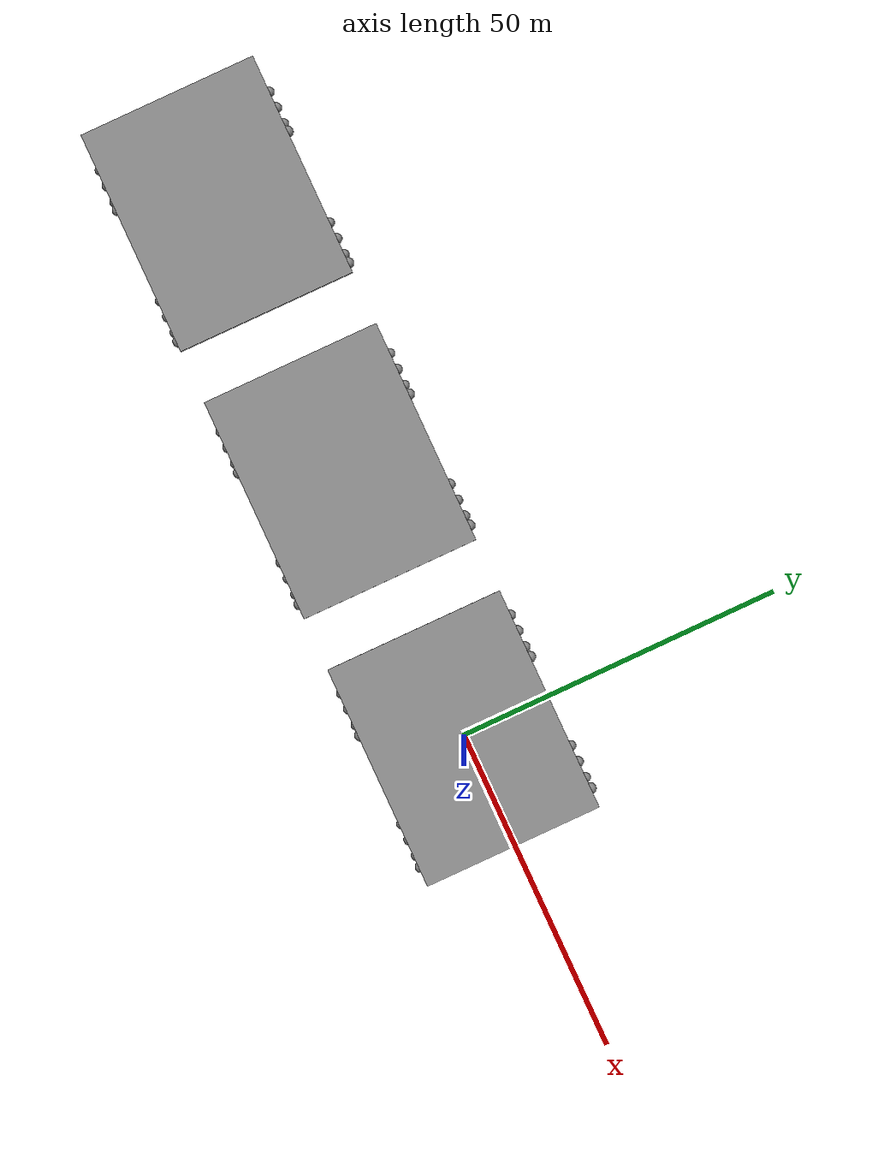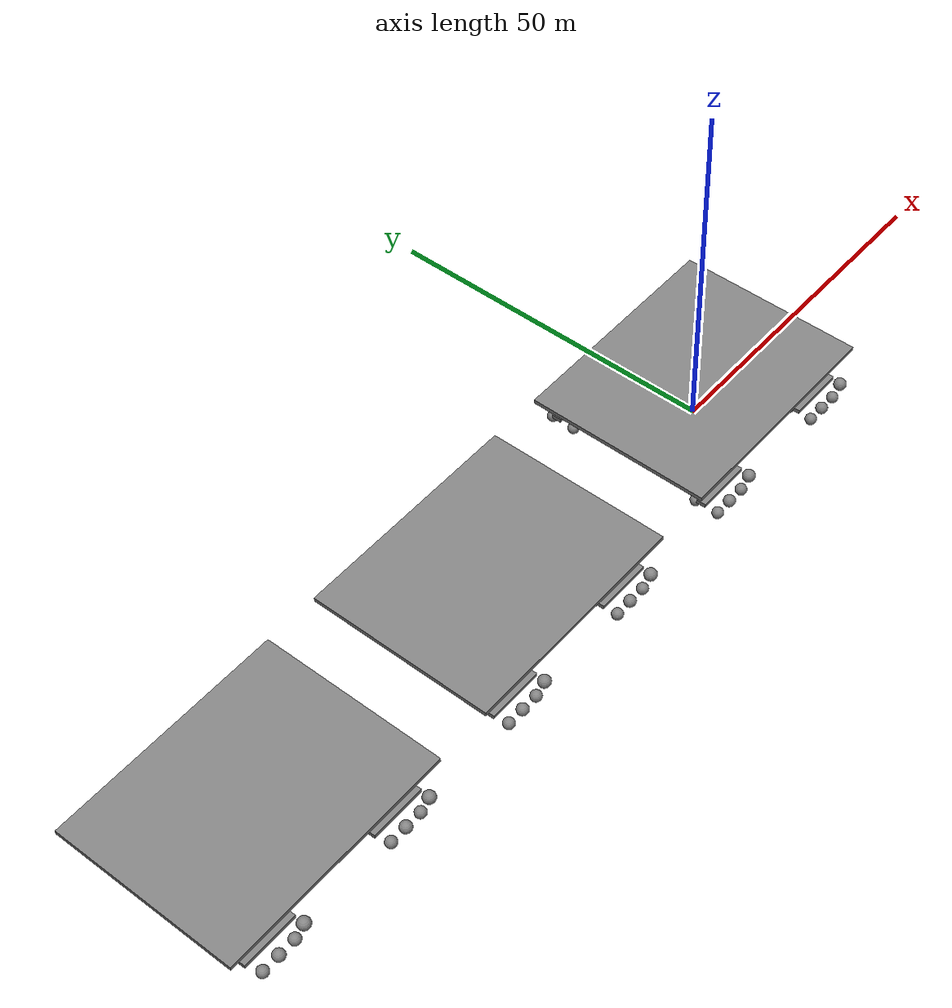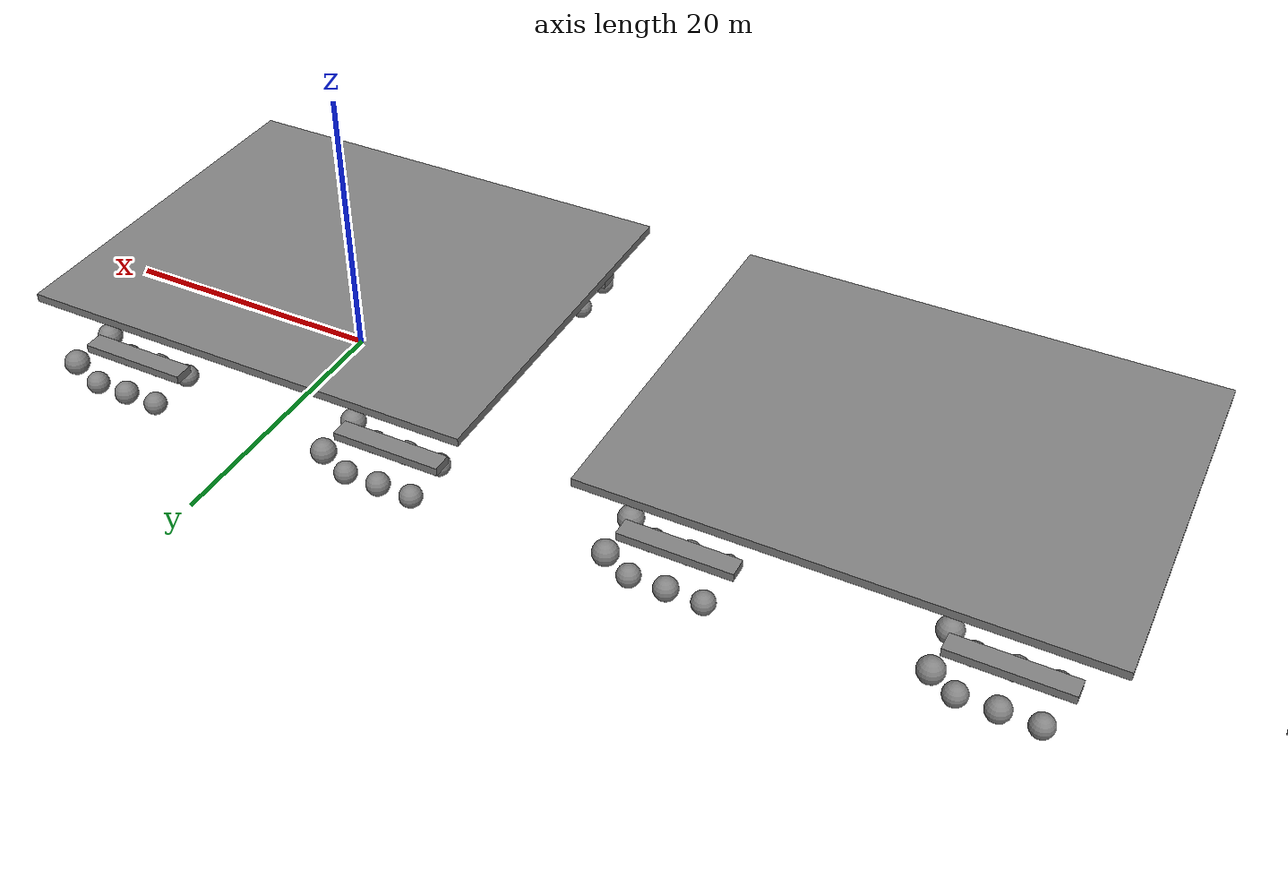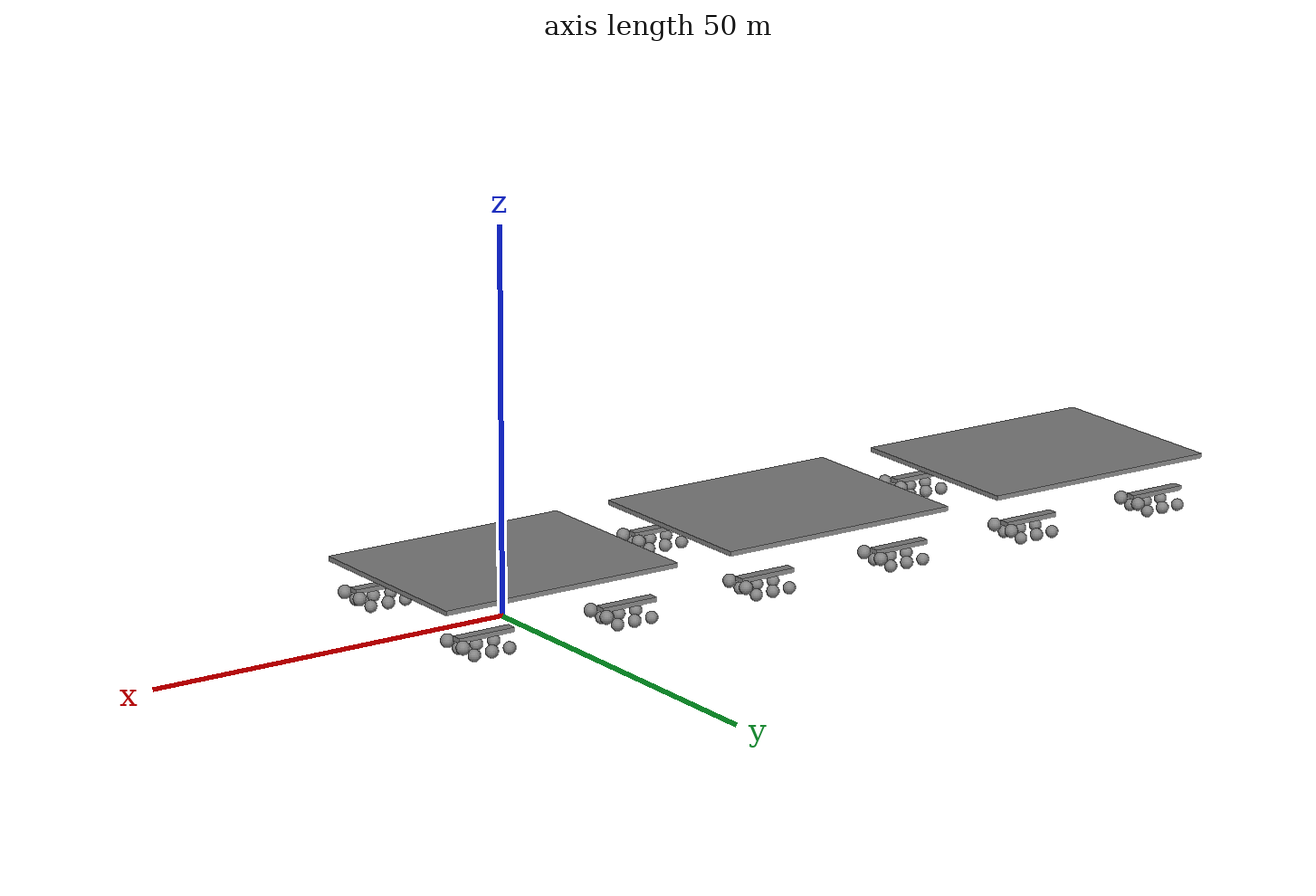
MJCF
<mujoco model="Leviathan003_three_modules_locked_containers">
  <compiler angle="radian" autolimits="true" />
  <option gravity="0 0 -9.81" timestep="0.005" integrator="implicitfast" iterations="60" tolerance="1e-9">
    <flag filterparent="disable" />
  </option>
  <worldbody>
    <body name="front" pos="0.0 0.0 9.889999999999999">
      <freejoint name="root" />
      <inertial pos="0.0 0.0 0.0" mass="4212000.0" diaginertia="369603000.0 519480000.0000001 661635000.0000001" />
      <body name="hitch_slide" pos="-21.0 0.0 -3.5">
        <inertial pos="0.0 0.0 0.0" mass="20000.0" diaginertia="25000.0 25000.0 25000.0" />
        <joint name="extension" type="slide" axis="-1.0 0.0 0.0" pos="0.0 0.0 0.0" limited="true" range="0.0 4.0" stiffness="0" damping="0" springref="0" solreflimit=".01 1" solimplimit=".99 .999 .001" />
        <body name="hitch_yaw">
          <inertial pos="0.0 0.0 0.0" mass="10000.0" diaginertia="12000.0 12000.0 12000.0" />
          <joint name="hitch_yaw" type="hinge" axis="0.0 0.0 1.0" pos="0.0 0.0 0.0" limited="true" range="-0.5235987755982988 0.5235987755982988" stiffness="0" damping="0" springref="0" solreflimit=".01 1" solimplimit=".99 .999 .001" />
          <body name="hitch_pitch" pos="-2.1999999999999993 0.0 0.0">
            <inertial pos="0.0 0.0 0.0" mass="10000.0" diaginertia="12000.0 12000.0 12000.0" />
            <joint name="hitch_pitch" type="hinge" axis="0.0 1.0 0.0" pos="0.0 0.0 0.0" limited="true" range="-0.13962634015954636 0.13962634015954636" stiffness="0" damping="0" springref="0" solreflimit=".01 1" solimplimit=".99 .999 .001" />
            <body name="rear" pos="-18.8 0.0 3.5">
              <joint name="hitch_roll" type="hinge" axis="1.0 0.0 0.0" pos="17.900000000000002 0.0 -3.5" limited="true" range="-0.10471975511965978 0.10471975511965978" stiffness="0" damping="0" springref="0" solreflimit=".01 1" solimplimit=".99 .999 .001" />
              <inertial pos="0.0 0.0 0.12300864553314206" mass="4164000.0" diaginertia="311472125.6996885 471126057.3796884 595216474.9760004" />
              <geom type="box" size="17 13.5 .3" pos="0 0 -2.8" contype="0" conaffinity="0" mass="0" />
              <body name="rear_bogie_aft_right_heave" pos="-10.5 -11.8 -5.75">
                <inertial pos="0.0 0.0 0.0" mass="10000.0" diaginertia="20000.0 20000.0 20000.0" />
                <joint name="rear_bogie_aft_right_heave" type="slide" axis="0.0 0.0 1.0" pos="0.0 0.0 0.0" limited="true" range="-0.8 0.8" stiffness="29458028.571428575" damping="8902729.545096992" springref="-0.35" solreflimit=".01 1" solimplimit=".99 .999 .001" />
                <body name="rear_bogie_aft_right_yaw" pos="0 0 0">
                  <inertial pos="0.0 0.0 0.0" mass="10000.0" diaginertia="20000.0 20000.0 20000.0" />
                  <joint name="rear_bogie_aft_right_yaw" type="hinge" axis="0.0 0.0 1.0" pos="0.0 0.0 0.0" limited="true" range="-0.6108652381980153 0.6108652381980153" stiffness="0" damping="0" springref="0" solreflimit=".01 1" solimplimit=".99 .999 .001" />
                  <body name="rear_bogie_aft_right_pitch" pos="0 0 0">
                    <inertial pos="0.0 0.0 0.0" mass="10000.0" diaginertia="20000.0 20000.0 20000.0" />
                    <joint name="rear_bogie_aft_right_pitch" type="hinge" axis="0.0 1.0 0.0" pos="0.0 0.0 0.0" limited="true" range="-0.20943951023931956 0.20943951023931956" stiffness="8000000.0" damping="3000000.0" springref="0" solreflimit=".01 1" solimplimit=".99 .999 .001" />
                    <body name="rear_bogie_aft_right" pos="0 0 0">
                      <inertial pos="0.0 0.0 -1.25" mass="90000.0" diaginertia="294375.0 975000.0 1134375.0" />
                      <joint name="rear_bogie_aft_right_roll" type="hinge" axis="1.0 0.0 0.0" pos="0.0 0.0 0.0" limited="true" range="-0.17453292519943295 0.17453292519943295" stiffness="8000000.0" damping="3000000.0" springref="0" solreflimit=".01 1" solimplimit=".99 .999 .001" />
                      <geom type="box" size="4 .7 .3" pos="0 0 -1.3" contype="0" conaffinity="0" mass="0" />
                      <body name="rear_bogie_aft_right_wheel_right_1" pos="-2.55 -1.75 -3.1">
                        <inertial pos="0.0 0.0 0.0" mass="12000.0" diaginertia="4480.000000000001 3840.000000000001 4480.000000000001" />
                        <joint name="rear_bogie_aft_right_wheel_right_1" type="slide" axis="0.0 0.0 1.0" pos="0.0 0.0 0.0" limited="true" range="-0.35 0.35" stiffness="0" damping="0" springref="-0.18" solreflimit=".01 1" solimplimit=".99 .999 .001" />
                        <geom type="sphere" size="0.8" contype="0" conaffinity="0" mass="0" />
                      </body>
                      <body name="rear_bogie_aft_right_wheel_right_2" pos="0.0 -1.75 -3.0700000000000003">
                        <inertial pos="0.0 0.0 0.0" mass="12000.0" diaginertia="4626.700000000001 4133.4 4626.700000000001" />
                        <joint name="rear_bogie_aft_right_wheel_right_2" type="slide" axis="0.0 0.0 1.0" pos="0.0 0.0 0.0" limited="true" range="-0.35 0.35" stiffness="0" damping="0" springref="-0.18" solreflimit=".01 1" solimplimit=".99 .999 .001" />
                        <geom type="sphere" size="0.83" contype="0" conaffinity="0" mass="0" />
                      </body>
                      <body name="rear_bogie_aft_right_wheel_right_3" pos="2.55 -1.75 -3.1">
                        <inertial pos="0.0 0.0 0.0" mass="12000.0" diaginertia="4480.000000000001 3840.000000000001 4480.000000000001" />
                        <joint name="rear_bogie_aft_right_wheel_right_3" type="slide" axis="0.0 0.0 1.0" pos="0.0 0.0 0.0" limited="true" range="-0.35 0.35" stiffness="0" damping="0" springref="-0.18" solreflimit=".01 1" solimplimit=".99 .999 .001" />
                        <geom type="sphere" size="0.8" contype="0" conaffinity="0" mass="0" />
                      </body>
                      <body name="rear_bogie_aft_right_wheel_left_1" pos="-2.55 1.75 -3.1">
                        <inertial pos="0.0 0.0 0.0" mass="12000.0" diaginertia="4480.000000000001 3840.000000000001 4480.000000000001" />
                        <joint name="rear_bogie_aft_right_wheel_left_1" type="slide" axis="0.0 0.0 1.0" pos="0.0 0.0 0.0" limited="true" range="-0.35 0.35" stiffness="0" damping="0" springref="-0.18" solreflimit=".01 1" solimplimit=".99 .999 .001" />
                        <geom type="sphere" size="0.8" contype="0" conaffinity="0" mass="0" />
                      </body>
                      <body name="rear_bogie_aft_right_wheel_left_2" pos="0.0 1.75 -3.0700000000000003">
                        <inertial pos="0.0 0.0 0.0" mass="12000.0" diaginertia="4626.700000000001 4133.4 4626.700000000001" />
                        <joint name="rear_bogie_aft_right_wheel_left_2" type="slide" axis="0.0 0.0 1.0" pos="0.0 0.0 0.0" limited="true" range="-0.35 0.35" stiffness="0" damping="0" springref="-0.18" solreflimit=".01 1" solimplimit=".99 .999 .001" />
                        <geom type="sphere" size="0.83" contype="0" conaffinity="0" mass="0" />
                      </body>
                      <body name="rear_bogie_aft_right_wheel_left_3" pos="2.55 1.75 -3.1">
                        <inertial pos="0.0 0.0 0.0" mass="12000.0" diaginertia="4480.000000000001 3840.000000000001 4480.000000000001" />
                        <joint name="rear_bogie_aft_right_wheel_left_3" type="slide" axis="0.0 0.0 1.0" pos="0.0 0.0 0.0" limited="true" range="-0.35 0.35" stiffness="0" damping="0" springref="-0.18" solreflimit=".01 1" solimplimit=".99 .999 .001" />
                        <geom type="sphere" size="0.8" contype="0" conaffinity="0" mass="0" />
                      </body>
                      <body name="rear_bogie_aft_right_idler_right" pos="4.15 -1.75 -1.85">
                        <inertial pos="0 0 0" mass="12000.0" diaginertia="4883.200000000001 4646.4 4883.200000000001" />
                        <joint name="rear_bogie_aft_right_idler_right" type="slide" axis="1 0 0" range="-0.32 0.24" stiffness="0" damping="0" solreflimit=".01 1" solimplimit=".99 .999 .001" />
                        <geom type="sphere" size="0.88" mass="0" contype="0" conaffinity="0" />
                      </body>
                      <body name="rear_bogie_aft_right_idler_left" pos="4.15 1.75 -1.85">
                        <inertial pos="0 0 0" mass="12000.0" diaginertia="4883.200000000001 4646.4 4883.200000000001" />
                        <joint name="rear_bogie_aft_right_idler_left" type="slide" axis="1 0 0" range="-0.32 0.24" stiffness="0" damping="0" solreflimit=".01 1" solimplimit=".99 .999 .001" />
                        <geom type="sphere" size="0.88" mass="0" contype="0" conaffinity="0" />
                      </body>
                    </body>
                  </body>
                </body>
              </body>
              <body name="rear_bogie_aft_left_heave" pos="-10.5 11.8 -5.75">
                <inertial pos="0.0 0.0 0.0" mass="10000.0" diaginertia="20000.0 20000.0 20000.0" />
                <joint name="rear_bogie_aft_left_heave" type="slide" axis="0.0 0.0 1.0" pos="0.0 0.0 0.0" limited="true" range="-0.8 0.8" stiffness="29458028.571428575" damping="8902729.545096992" springref="-0.35" solreflimit=".01 1" solimplimit=".99 .999 .001" />
                <body name="rear_bogie_aft_left_yaw" pos="0 0 0">
                  <inertial pos="0.0 0.0 0.0" mass="10000.0" diaginertia="20000.0 20000.0 20000.0" />
                  <joint name="rear_bogie_aft_left_yaw" type="hinge" axis="0.0 0.0 1.0" pos="0.0 0.0 0.0" limited="true" range="-0.6108652381980153 0.6108652381980153" stiffness="0" damping="0" springref="0" solreflimit=".01 1" solimplimit=".99 .999 .001" />
                  <body name="rear_bogie_aft_left_pitch" pos="0 0 0">
                    <inertial pos="0.0 0.0 0.0" mass="10000.0" diaginertia="20000.0 20000.0 20000.0" />
                    <joint name="rear_bogie_aft_left_pitch" type="hinge" axis="0.0 1.0 0.0" pos="0.0 0.0 0.0" limited="true" range="-0.20943951023931956 0.20943951023931956" stiffness="8000000.0" damping="3000000.0" springref="0" solreflimit=".01 1" solimplimit=".99 .999 .001" />
                    <body name="rear_bogie_aft_left" pos="0 0 0">
                      <inertial pos="0.0 0.0 -1.25" mass="90000.0" diaginertia="294375.0 975000.0 1134375.0" />
                      <joint name="rear_bogie_aft_left_roll" type="hinge" axis="1.0 0.0 0.0" pos="0.0 0.0 0.0" limited="true" range="-0.17453292519943295 0.17453292519943295" stiffness="8000000.0" damping="3000000.0" springref="0" solreflimit=".01 1" solimplimit=".99 .999 .001" />
                      <geom type="box" size="4 .7 .3" pos="0 0 -1.3" contype="0" conaffinity="0" mass="0" />
                      <body name="rear_bogie_aft_left_wheel_right_1" pos="-2.55 -1.75 -3.1">
                        <inertial pos="0.0 0.0 0.0" mass="12000.0" diaginertia="4480.000000000001 3840.000000000001 4480.000000000001" />
                        <joint name="rear_bogie_aft_left_wheel_right_1" type="slide" axis="0.0 0.0 1.0" pos="0.0 0.0 0.0" limited="true" range="-0.35 0.35" stiffness="0" damping="0" springref="-0.18" solreflimit=".01 1" solimplimit=".99 .999 .001" />
                        <geom type="sphere" size="0.8" contype="0" conaffinity="0" mass="0" />
                      </body>
                      <body name="rear_bogie_aft_left_wheel_right_2" pos="0.0 -1.75 -3.0700000000000003">
                        <inertial pos="0.0 0.0 0.0" mass="12000.0" diaginertia="4626.700000000001 4133.4 4626.700000000001" />
                        <joint name="rear_bogie_aft_left_wheel_right_2" type="slide" axis="0.0 0.0 1.0" pos="0.0 0.0 0.0" limited="true" range="-0.35 0.35" stiffness="0" damping="0" springref="-0.18" solreflimit=".01 1" solimplimit=".99 .999 .001" />
                        <geom type="sphere" size="0.83" contype="0" conaffinity="0" mass="0" />
                      </body>
                      <body name="rear_bogie_aft_left_wheel_right_3" pos="2.55 -1.75 -3.1">
                        <inertial pos="0.0 0.0 0.0" mass="12000.0" diaginertia="4480.000000000001 3840.000000000001 4480.000000000001" />
                        <joint name="rear_bogie_aft_left_wheel_right_3" type="slide" axis="0.0 0.0 1.0" pos="0.0 0.0 0.0" limited="true" range="-0.35 0.35" stiffness="0" damping="0" springref="-0.18" solreflimit=".01 1" solimplimit=".99 .999 .001" />
                        <geom type="sphere" size="0.8" contype="0" conaffinity="0" mass="0" />
                      </body>
                      <body name="rear_bogie_aft_left_wheel_left_1" pos="-2.55 1.75 -3.1">
                        <inertial pos="0.0 0.0 0.0" mass="12000.0" diaginertia="4480.000000000001 3840.000000000001 4480.000000000001" />
                        <joint name="rear_bogie_aft_left_wheel_left_1" type="slide" axis="0.0 0.0 1.0" pos="0.0 0.0 0.0" limited="true" range="-0.35 0.35" stiffness="0" damping="0" springref="-0.18" solreflimit=".01 1" solimplimit=".99 .999 .001" />
                        <geom type="sphere" size="0.8" contype="0" conaffinity="0" mass="0" />
                      </body>
                      <body name="rear_bogie_aft_left_wheel_left_2" pos="0.0 1.75 -3.0700000000000003">
                        <inertial pos="0.0 0.0 0.0" mass="12000.0" diaginertia="4626.700000000001 4133.4 4626.700000000001" />
                        <joint name="rear_bogie_aft_left_wheel_left_2" type="slide" axis="0.0 0.0 1.0" pos="0.0 0.0 0.0" limited="true" range="-0.35 0.35" stiffness="0" damping="0" springref="-0.18" solreflimit=".01 1" solimplimit=".99 .999 .001" />
                        <geom type="sphere" size="0.83" contype="0" conaffinity="0" mass="0" />
                      </body>
                      <body name="rear_bogie_aft_left_wheel_left_3" pos="2.55 1.75 -3.1">
                        <inertial pos="0.0 0.0 0.0" mass="12000.0" diaginertia="4480.000000000001 3840.000000000001 4480.000000000001" />
                        <joint name="rear_bogie_aft_left_wheel_left_3" type="slide" axis="0.0 0.0 1.0" pos="0.0 0.0 0.0" limited="true" range="-0.35 0.35" stiffness="0" damping="0" springref="-0.18" solreflimit=".01 1" solimplimit=".99 .999 .001" />
                        <geom type="sphere" size="0.8" contype="0" conaffinity="0" mass="0" />
                      </body>
                      <body name="rear_bogie_aft_left_idler_right" pos="4.15 -1.75 -1.85">
                        <inertial pos="0 0 0" mass="12000.0" diaginertia="4883.200000000001 4646.4 4883.200000000001" />
                        <joint name="rear_bogie_aft_left_idler_right" type="slide" axis="1 0 0" range="-0.32 0.24" stiffness="0" damping="0" solreflimit=".01 1" solimplimit=".99 .999 .001" />
                        <geom type="sphere" size="0.88" mass="0" contype="0" conaffinity="0" />
                      </body>
                      <body name="rear_bogie_aft_left_idler_left" pos="4.15 1.75 -1.85">
                        <inertial pos="0 0 0" mass="12000.0" diaginertia="4883.200000000001 4646.4 4883.200000000001" />
                        <joint name="rear_bogie_aft_left_idler_left" type="slide" axis="1 0 0" range="-0.32 0.24" stiffness="0" damping="0" solreflimit=".01 1" solimplimit=".99 .999 .001" />
                        <geom type="sphere" size="0.88" mass="0" contype="0" conaffinity="0" />
                      </body>
                    </body>
                  </body>
                </body>
              </body>
              <body name="rear_bogie_fore_right_heave" pos="10.5 -11.8 -5.75">
                <inertial pos="0.0 0.0 0.0" mass="10000.0" diaginertia="20000.0 20000.0 20000.0" />
                <joint name="rear_bogie_fore_right_heave" type="slide" axis="0.0 0.0 1.0" pos="0.0 0.0 0.0" limited="true" range="-0.8 0.8" stiffness="29458028.571428575" damping="8902729.545096992" springref="-0.35" solreflimit=".01 1" solimplimit=".99 .999 .001" />
                <body name="rear_bogie_fore_right_yaw" pos="0 0 0">
                  <inertial pos="0.0 0.0 0.0" mass="10000.0" diaginertia="20000.0 20000.0 20000.0" />
                  <joint name="rear_bogie_fore_right_yaw" type="hinge" axis="0.0 0.0 1.0" pos="0.0 0.0 0.0" limited="true" range="-0.6108652381980153 0.6108652381980153" stiffness="0" damping="0" springref="0" solreflimit=".01 1" solimplimit=".99 .999 .001" />
                  <body name="rear_bogie_fore_right_pitch" pos="0 0 0">
                    <inertial pos="0.0 0.0 0.0" mass="10000.0" diaginertia="20000.0 20000.0 20000.0" />
                    <joint name="rear_bogie_fore_right_pitch" type="hinge" axis="0.0 1.0 0.0" pos="0.0 0.0 0.0" limited="true" range="-0.20943951023931956 0.20943951023931956" stiffness="8000000.0" damping="3000000.0" springref="0" solreflimit=".01 1" solimplimit=".99 .999 .001" />
                    <body name="rear_bogie_fore_right" pos="0 0 0">
                      <inertial pos="0.0 0.0 -1.25" mass="90000.0" diaginertia="294375.0 975000.0 1134375.0" />
                      <joint name="rear_bogie_fore_right_roll" type="hinge" axis="1.0 0.0 0.0" pos="0.0 0.0 0.0" limited="true" range="-0.17453292519943295 0.17453292519943295" stiffness="8000000.0" damping="3000000.0" springref="0" solreflimit=".01 1" solimplimit=".99 .999 .001" />
                      <geom type="box" size="4 .7 .3" pos="0 0 -1.3" contype="0" conaffinity="0" mass="0" />
                      <body name="rear_bogie_fore_right_wheel_right_1" pos="-2.55 -1.75 -3.1">
                        <inertial pos="0.0 0.0 0.0" mass="12000.0" diaginertia="4480.000000000001 3840.000000000001 4480.000000000001" />
                        <joint name="rear_bogie_fore_right_wheel_right_1" type="slide" axis="0.0 0.0 1.0" pos="0.0 0.0 0.0" limited="true" range="-0.35 0.35" stiffness="0" damping="0" springref="-0.18" solreflimit=".01 1" solimplimit=".99 .999 .001" />
                        <geom type="sphere" size="0.8" contype="0" conaffinity="0" mass="0" />
                      </body>
                      <body name="rear_bogie_fore_right_wheel_right_2" pos="0.0 -1.75 -3.0700000000000003">
                        <inertial pos="0.0 0.0 0.0" mass="12000.0" diaginertia="4626.700000000001 4133.4 4626.700000000001" />
                        <joint name="rear_bogie_fore_right_wheel_right_2" type="slide" axis="0.0 0.0 1.0" pos="0.0 0.0 0.0" limited="true" range="-0.35 0.35" stiffness="0" damping="0" springref="-0.18" solreflimit=".01 1" solimplimit=".99 .999 .001" />
                        <geom type="sphere" size="0.83" contype="0" conaffinity="0" mass="0" />
                      </body>
                      <body name="rear_bogie_fore_right_wheel_right_3" pos="2.55 -1.75 -3.1">
                        <inertial pos="0.0 0.0 0.0" mass="12000.0" diaginertia="4480.000000000001 3840.000000000001 4480.000000000001" />
                        <joint name="rear_bogie_fore_right_wheel_right_3" type="slide" axis="0.0 0.0 1.0" pos="0.0 0.0 0.0" limited="true" range="-0.35 0.35" stiffness="0" damping="0" springref="-0.18" solreflimit=".01 1" solimplimit=".99 .999 .001" />
                        <geom type="sphere" size="0.8" contype="0" conaffinity="0" mass="0" />
                      </body>
                      <body name="rear_bogie_fore_right_wheel_left_1" pos="-2.55 1.75 -3.1">
                        <inertial pos="0.0 0.0 0.0" mass="12000.0" diaginertia="4480.000000000001 3840.000000000001 4480.000000000001" />
                        <joint name="rear_bogie_fore_right_wheel_left_1" type="slide" axis="0.0 0.0 1.0" pos="0.0 0.0 0.0" limited="true" range="-0.35 0.35" stiffness="0" damping="0" springref="-0.18" solreflimit=".01 1" solimplimit=".99 .999 .001" />
                        <geom type="sphere" size="0.8" contype="0" conaffinity="0" mass="0" />
                      </body>
                      <body name="rear_bogie_fore_right_wheel_left_2" pos="0.0 1.75 -3.0700000000000003">
                        <inertial pos="0.0 0.0 0.0" mass="12000.0" diaginertia="4626.700000000001 4133.4 4626.700000000001" />
                        <joint name="rear_bogie_fore_right_wheel_left_2" type="slide" axis="0.0 0.0 1.0" pos="0.0 0.0 0.0" limited="true" range="-0.35 0.35" stiffness="0" damping="0" springref="-0.18" solreflimit=".01 1" solimplimit=".99 .999 .001" />
                        <geom type="sphere" size="0.83" contype="0" conaffinity="0" mass="0" />
                      </body>
                      <body name="rear_bogie_fore_right_wheel_left_3" pos="2.55 1.75 -3.1">
                        <inertial pos="0.0 0.0 0.0" mass="12000.0" diaginertia="4480.000000000001 3840.000000000001 4480.000000000001" />
                        <joint name="rear_bogie_fore_right_wheel_left_3" type="slide" axis="0.0 0.0 1.0" pos="0.0 0.0 0.0" limited="true" range="-0.35 0.35" stiffness="0" damping="0" springref="-0.18" solreflimit=".01 1" solimplimit=".99 .999 .001" />
                        <geom type="sphere" size="0.8" contype="0" conaffinity="0" mass="0" />
                      </body>
                      <body name="rear_bogie_fore_right_idler_right" pos="4.15 -1.75 -1.85">
                        <inertial pos="0 0 0" mass="12000.0" diaginertia="4883.200000000001 4646.4 4883.200000000001" />
                        <joint name="rear_bogie_fore_right_idler_right" type="slide" axis="1 0 0" range="-0.32 0.24" stiffness="0" damping="0" solreflimit=".01 1" solimplimit=".99 .999 .001" />
                        <geom type="sphere" size="0.88" mass="0" contype="0" conaffinity="0" />
                      </body>
                      <body name="rear_bogie_fore_right_idler_left" pos="4.15 1.75 -1.85">
                        <inertial pos="0 0 0" mass="12000.0" diaginertia="4883.200000000001 4646.4 4883.200000000001" />
                        <joint name="rear_bogie_fore_right_idler_left" type="slide" axis="1 0 0" range="-0.32 0.24" stiffness="0" damping="0" solreflimit=".01 1" solimplimit=".99 .999 .001" />
                        <geom type="sphere" size="0.88" mass="0" contype="0" conaffinity="0" />
                      </body>
                    </body>
                  </body>
                </body>
              </body>
              <body name="rear_bogie_fore_left_heave" pos="10.5 11.8 -5.75">
                <inertial pos="0.0 0.0 0.0" mass="10000.0" diaginertia="20000.0 20000.0 20000.0" />
                <joint name="rear_bogie_fore_left_heave" type="slide" axis="0.0 0.0 1.0" pos="0.0 0.0 0.0" limited="true" range="-0.8 0.8" stiffness="29458028.571428575" damping="8902729.545096992" springref="-0.35" solreflimit=".01 1" solimplimit=".99 .999 .001" />
                <body name="rear_bogie_fore_left_yaw" pos="0 0 0">
                  <inertial pos="0.0 0.0 0.0" mass="10000.0" diaginertia="20000.0 20000.0 20000.0" />
                  <joint name="rear_bogie_fore_left_yaw" type="hinge" axis="0.0 0.0 1.0" pos="0.0 0.0 0.0" limited="true" range="-0.6108652381980153 0.6108652381980153" stiffness="0" damping="0" springref="0" solreflimit=".01 1" solimplimit=".99 .999 .001" />
                  <body name="rear_bogie_fore_left_pitch" pos="0 0 0">
                    <inertial pos="0.0 0.0 0.0" mass="10000.0" diaginertia="20000.0 20000.0 20000.0" />
                    <joint name="rear_bogie_fore_left_pitch" type="hinge" axis="0.0 1.0 0.0" pos="0.0 0.0 0.0" limited="true" range="-0.20943951023931956 0.20943951023931956" stiffness="8000000.0" damping="3000000.0" springref="0" solreflimit=".01 1" solimplimit=".99 .999 .001" />
                    <body name="rear_bogie_fore_left" pos="0 0 0">
                      <inertial pos="0.0 0.0 -1.25" mass="90000.0" diaginertia="294375.0 975000.0 1134375.0" />
                      <joint name="rear_bogie_fore_left_roll" type="hinge" axis="1.0 0.0 0.0" pos="0.0 0.0 0.0" limited="true" range="-0.17453292519943295 0.17453292519943295" stiffness="8000000.0" damping="3000000.0" springref="0" solreflimit=".01 1" solimplimit=".99 .999 .001" />
                      <geom type="box" size="4 .7 .3" pos="0 0 -1.3" contype="0" conaffinity="0" mass="0" />
                      <body name="rear_bogie_fore_left_wheel_right_1" pos="-2.55 -1.75 -3.1">
                        <inertial pos="0.0 0.0 0.0" mass="12000.0" diaginertia="4480.000000000001 3840.000000000001 4480.000000000001" />
                        <joint name="rear_bogie_fore_left_wheel_right_1" type="slide" axis="0.0 0.0 1.0" pos="0.0 0.0 0.0" limited="true" range="-0.35 0.35" stiffness="0" damping="0" springref="-0.18" solreflimit=".01 1" solimplimit=".99 .999 .001" />
                        <geom type="sphere" size="0.8" contype="0" conaffinity="0" mass="0" />
                      </body>
                      <body name="rear_bogie_fore_left_wheel_right_2" pos="0.0 -1.75 -3.0700000000000003">
                        <inertial pos="0.0 0.0 0.0" mass="12000.0" diaginertia="4626.700000000001 4133.4 4626.700000000001" />
                        <joint name="rear_bogie_fore_left_wheel_right_2" type="slide" axis="0.0 0.0 1.0" pos="0.0 0.0 0.0" limited="true" range="-0.35 0.35" stiffness="0" damping="0" springref="-0.18" solreflimit=".01 1" solimplimit=".99 .999 .001" />
                        <geom type="sphere" size="0.83" contype="0" conaffinity="0" mass="0" />
                      </body>
                      <body name="rear_bogie_fore_left_wheel_right_3" pos="2.55 -1.75 -3.1">
                        <inertial pos="0.0 0.0 0.0" mass="12000.0" diaginertia="4480.000000000001 3840.000000000001 4480.000000000001" />
                        <joint name="rear_bogie_fore_left_wheel_right_3" type="slide" axis="0.0 0.0 1.0" pos="0.0 0.0 0.0" limited="true" range="-0.35 0.35" stiffness="0" damping="0" springref="-0.18" solreflimit=".01 1" solimplimit=".99 .999 .001" />
                        <geom type="sphere" size="0.8" contype="0" conaffinity="0" mass="0" />
                      </body>
                      <body name="rear_bogie_fore_left_wheel_left_1" pos="-2.55 1.75 -3.1">
                        <inertial pos="0.0 0.0 0.0" mass="12000.0" diaginertia="4480.000000000001 3840.000000000001 4480.000000000001" />
                        <joint name="rear_bogie_fore_left_wheel_left_1" type="slide" axis="0.0 0.0 1.0" pos="0.0 0.0 0.0" limited="true" range="-0.35 0.35" stiffness="0" damping="0" springref="-0.18" solreflimit=".01 1" solimplimit=".99 .999 .001" />
                        <geom type="sphere" size="0.8" contype="0" conaffinity="0" mass="0" />
                      </body>
                      <body name="rear_bogie_fore_left_wheel_left_2" pos="0.0 1.75 -3.0700000000000003">
                        <inertial pos="0.0 0.0 0.0" mass="12000.0" diaginertia="4626.700000000001 4133.4 4626.700000000001" />
                        <joint name="rear_bogie_fore_left_wheel_left_2" type="slide" axis="0.0 0.0 1.0" pos="0.0 0.0 0.0" limited="true" range="-0.35 0.35" stiffness="0" damping="0" springref="-0.18" solreflimit=".01 1" solimplimit=".99 .999 .001" />
                        <geom type="sphere" size="0.83" contype="0" conaffinity="0" mass="0" />
                      </body>
                      <body name="rear_bogie_fore_left_wheel_left_3" pos="2.55 1.75 -3.1">
                        <inertial pos="0.0 0.0 0.0" mass="12000.0" diaginertia="4480.000000000001 3840.000000000001 4480.000000000001" />
                        <joint name="rear_bogie_fore_left_wheel_left_3" type="slide" axis="0.0 0.0 1.0" pos="0.0 0.0 0.0" limited="true" range="-0.35 0.35" stiffness="0" damping="0" springref="-0.18" solreflimit=".01 1" solimplimit=".99 .999 .001" />
                        <geom type="sphere" size="0.8" contype="0" conaffinity="0" mass="0" />
                      </body>
                      <body name="rear_bogie_fore_left_idler_right" pos="4.15 -1.75 -1.85">
                        <inertial pos="0 0 0" mass="12000.0" diaginertia="4883.200000000001 4646.4 4883.200000000001" />
                        <joint name="rear_bogie_fore_left_idler_right" type="slide" axis="1 0 0" range="-0.32 0.24" stiffness="0" damping="0" solreflimit=".01 1" solimplimit=".99 .999 .001" />
                        <geom type="sphere" size="0.88" mass="0" contype="0" conaffinity="0" />
                      </body>
                      <body name="rear_bogie_fore_left_idler_left" pos="4.15 1.75 -1.85">
                        <inertial pos="0 0 0" mass="12000.0" diaginertia="4883.200000000001 4646.4 4883.200000000001" />
                        <joint name="rear_bogie_fore_left_idler_left" type="slide" axis="1 0 0" range="-0.32 0.24" stiffness="0" damping="0" solreflimit=".01 1" solimplimit=".99 .999 .001" />
                        <geom type="sphere" size="0.88" mass="0" contype="0" conaffinity="0" />
                      </body>
                    </body>
                  </body>
                </body>
              </body>
              <body name="tail_hitch_slide" pos="-21.0 0.0 -3.5">
                <inertial pos="0.0 0.0 0.0" mass="20000.0" diaginertia="25000.0 25000.0 25000.0" />
                <joint name="tail_extension" type="slide" axis="-1.0 0.0 0.0" pos="0.0 0.0 0.0" limited="true" range="0.0 4.0" stiffness="0" damping="0" springref="0" solreflimit=".01 1" solimplimit=".99 .999 .001" />
                <body name="tail_hitch_yaw">
                  <inertial pos="0.0 0.0 0.0" mass="10000.0" diaginertia="12000.0 12000.0 12000.0" />
                  <joint name="tail_hitch_yaw" type="hinge" axis="0.0 0.0 1.0" pos="0.0 0.0 0.0" limited="true" range="-0.5235987755982988 0.5235987755982988" stiffness="0" damping="0" springref="0" solreflimit=".01 1" solimplimit=".99 .999 .001" />
                  <body name="tail_hitch_pitch" pos="-2.1999999999999993 0.0 0.0">
                    <inertial pos="0.0 0.0 0.0" mass="10000.0" diaginertia="12000.0 12000.0 12000.0" />
                    <joint name="tail_hitch_pitch" type="hinge" axis="0.0 1.0 0.0" pos="0.0 0.0 0.0" limited="true" range="-0.13962634015954636 0.13962634015954636" stiffness="0" damping="0" springref="0" solreflimit=".01 1" solimplimit=".99 .999 .001" />
                    <body name="tail" pos="-18.8 0.0 3.5">
                      <joint name="tail_hitch_roll" type="hinge" axis="1.0 0.0 0.0" pos="17.900000000000002 0.0 -3.5" limited="true" range="-0.10471975511965978 0.10471975511965978" stiffness="0" damping="0" springref="0" solreflimit=".01 1" solimplimit=".99 .999 .001" />
                      <inertial pos="0.0 0.0 0.0" mass="4212000.0" diaginertia="369603000.0 519480000.0000001 661635000.0000001" />
                      <geom type="box" size="17 13.5 .3" pos="0 0 -2.8" contype="0" conaffinity="0" mass="0" />
                      <body name="tail_bogie_aft_right_heave" pos="-10.5 -11.8 -5.75">
                        <inertial pos="0.0 0.0 0.0" mass="10000.0" diaginertia="20000.0 20000.0 20000.0" />
                        <joint name="tail_bogie_aft_right_heave" type="slide" axis="0.0 0.0 1.0" pos="0.0 0.0 0.0" limited="true" range="-0.8 0.8" stiffness="29654228.571428575" damping="8962024.60391305" springref="-0.35" solreflimit=".01 1" solimplimit=".99 .999 .001" />
                        <body name="tail_bogie_aft_right_yaw" pos="0 0 0">
                          <inertial pos="0.0 0.0 0.0" mass="10000.0" diaginertia="20000.0 20000.0 20000.0" />
                          <joint name="tail_bogie_aft_right_yaw" type="hinge" axis="0.0 0.0 1.0" pos="0.0 0.0 0.0" limited="true" range="-0.6108652381980153 0.6108652381980153" stiffness="0" damping="0" springref="0" solreflimit=".01 1" solimplimit=".99 .999 .001" />
                          <body name="tail_bogie_aft_right_pitch" pos="0 0 0">
                            <inertial pos="0.0 0.0 0.0" mass="10000.0" diaginertia="20000.0 20000.0 20000.0" />
                            <joint name="tail_bogie_aft_right_pitch" type="hinge" axis="0.0 1.0 0.0" pos="0.0 0.0 0.0" limited="true" range="-0.20943951023931956 0.20943951023931956" stiffness="8000000.0" damping="3000000.0" springref="0" solreflimit=".01 1" solimplimit=".99 .999 .001" />
                            <body name="tail_bogie_aft_right" pos="0 0 0">
                              <inertial pos="0.0 0.0 -1.25" mass="90000.0" diaginertia="294375.0 975000.0 1134375.0" />
                              <joint name="tail_bogie_aft_right_roll" type="hinge" axis="1.0 0.0 0.0" pos="0.0 0.0 0.0" limited="true" range="-0.17453292519943295 0.17453292519943295" stiffness="8000000.0" damping="3000000.0" springref="0" solreflimit=".01 1" solimplimit=".99 .999 .001" />
                              <geom type="box" size="4 .7 .3" pos="0 0 -1.3" contype="0" conaffinity="0" mass="0" />
                              <body name="tail_bogie_aft_right_wheel_right_1" pos="-2.55 -1.75 -3.1">
                                <inertial pos="0.0 0.0 0.0" mass="12000.0" diaginertia="4480.000000000001 3840.000000000001 4480.000000000001" />
                                <joint name="tail_bogie_aft_right_wheel_right_1" type="slide" axis="0.0 0.0 1.0" pos="0.0 0.0 0.0" limited="true" range="-0.35 0.35" stiffness="0" damping="0" springref="-0.18" solreflimit=".01 1" solimplimit=".99 .999 .001" />
                                <geom type="sphere" size="0.8" contype="0" conaffinity="0" mass="0" />
                              </body>
                              <body name="tail_bogie_aft_right_wheel_right_2" pos="0.0 -1.75 -3.0700000000000003">
                                <inertial pos="0.0 0.0 0.0" mass="12000.0" diaginertia="4626.700000000001 4133.4 4626.700000000001" />
                                <joint name="tail_bogie_aft_right_wheel_right_2" type="slide" axis="0.0 0.0 1.0" pos="0.0 0.0 0.0" limited="true" range="-0.35 0.35" stiffness="0" damping="0" springref="-0.18" solreflimit=".01 1" solimplimit=".99 .999 .001" />
                                <geom type="sphere" size="0.83" contype="0" conaffinity="0" mass="0" />
                              </body>
                              <body name="tail_bogie_aft_right_wheel_right_3" pos="2.55 -1.75 -3.1">
                                <inertial pos="0.0 0.0 0.0" mass="12000.0" diaginertia="4480.000000000001 3840.000000000001 4480.000000000001" />
                                <joint name="tail_bogie_aft_right_wheel_right_3" type="slide" axis="0.0 0.0 1.0" pos="0.0 0.0 0.0" limited="true" range="-0.35 0.35" stiffness="0" damping="0" springref="-0.18" solreflimit=".01 1" solimplimit=".99 .999 .001" />
                                <geom type="sphere" size="0.8" contype="0" conaffinity="0" mass="0" />
                              </body>
                              <body name="tail_bogie_aft_right_wheel_left_1" pos="-2.55 1.75 -3.1">
                                <inertial pos="0.0 0.0 0.0" mass="12000.0" diaginertia="4480.000000000001 3840.000000000001 4480.000000000001" />
                                <joint name="tail_bogie_aft_right_wheel_left_1" type="slide" axis="0.0 0.0 1.0" pos="0.0 0.0 0.0" limited="true" range="-0.35 0.35" stiffness="0" damping="0" springref="-0.18" solreflimit=".01 1" solimplimit=".99 .999 .001" />
                                <geom type="sphere" size="0.8" contype="0" conaffinity="0" mass="0" />
                              </body>
                              <body name="tail_bogie_aft_right_wheel_left_2" pos="0.0 1.75 -3.0700000000000003">
                                <inertial pos="0.0 0.0 0.0" mass="12000.0" diaginertia="4626.700000000001 4133.4 4626.700000000001" />
                                <joint name="tail_bogie_aft_right_wheel_left_2" type="slide" axis="0.0 0.0 1.0" pos="0.0 0.0 0.0" limited="true" range="-0.35 0.35" stiffness="0" damping="0" springref="-0.18" solreflimit=".01 1" solimplimit=".99 .999 .001" />
                                <geom type="sphere" size="0.83" contype="0" conaffinity="0" mass="0" />
                              </body>
                              <body name="tail_bogie_aft_right_wheel_left_3" pos="2.55 1.75 -3.1">
                                <inertial pos="0.0 0.0 0.0" mass="12000.0" diaginertia="4480.000000000001 3840.000000000001 4480.000000000001" />
                                <joint name="tail_bogie_aft_right_wheel_left_3" type="slide" axis="0.0 0.0 1.0" pos="0.0 0.0 0.0" limited="true" range="-0.35 0.35" stiffness="0" damping="0" springref="-0.18" solreflimit=".01 1" solimplimit=".99 .999 .001" />
                                <geom type="sphere" size="0.8" contype="0" conaffinity="0" mass="0" />
                              </body>
                              <body name="tail_bogie_aft_right_idler_right" pos="4.15 -1.75 -1.85">
                                <inertial pos="0 0 0" mass="12000.0" diaginertia="4883.200000000001 4646.4 4883.200000000001" />
                                <joint name="tail_bogie_aft_right_idler_right" type="slide" axis="1 0 0" range="-0.32 0.24" stiffness="0" damping="0" solreflimit=".01 1" solimplimit=".99 .999 .001" />
                                <geom type="sphere" size="0.88" mass="0" contype="0" conaffinity="0" />
                              </body>
                              <body name="tail_bogie_aft_right_idler_left" pos="4.15 1.75 -1.85">
                                <inertial pos="0 0 0" mass="12000.0" diaginertia="4883.200000000001 4646.4 4883.200000000001" />
                                <joint name="tail_bogie_aft_right_idler_left" type="slide" axis="1 0 0" range="-0.32 0.24" stiffness="0" damping="0" solreflimit=".01 1" solimplimit=".99 .999 .001" />
                                <geom type="sphere" size="0.88" mass="0" contype="0" conaffinity="0" />
                              </body>
                            </body>
                          </body>
                        </body>
                      </body>
                      <body name="tail_bogie_aft_left_heave" pos="-10.5 11.8 -5.75">
                        <inertial pos="0.0 0.0 0.0" mass="10000.0" diaginertia="20000.0 20000.0 20000.0" />
                        <joint name="tail_bogie_aft_left_heave" type="slide" axis="0.0 0.0 1.0" pos="0.0 0.0 0.0" limited="true" range="-0.8 0.8" stiffness="29654228.571428575" damping="8962024.60391305" springref="-0.35" solreflimit=".01 1" solimplimit=".99 .999 .001" />
                        <body name="tail_bogie_aft_left_yaw" pos="0 0 0">
                          <inertial pos="0.0 0.0 0.0" mass="10000.0" diaginertia="20000.0 20000.0 20000.0" />
                          <joint name="tail_bogie_aft_left_yaw" type="hinge" axis="0.0 0.0 1.0" pos="0.0 0.0 0.0" limited="true" range="-0.6108652381980153 0.6108652381980153" stiffness="0" damping="0" springref="0" solreflimit=".01 1" solimplimit=".99 .999 .001" />
                          <body name="tail_bogie_aft_left_pitch" pos="0 0 0">
                            <inertial pos="0.0 0.0 0.0" mass="10000.0" diaginertia="20000.0 20000.0 20000.0" />
                            <joint name="tail_bogie_aft_left_pitch" type="hinge" axis="0.0 1.0 0.0" pos="0.0 0.0 0.0" limited="true" range="-0.20943951023931956 0.20943951023931956" stiffness="8000000.0" damping="3000000.0" springref="0" solreflimit=".01 1" solimplimit=".99 .999 .001" />
                            <body name="tail_bogie_aft_left" pos="0 0 0">
                              <inertial pos="0.0 0.0 -1.25" mass="90000.0" diaginertia="294375.0 975000.0 1134375.0" />
                              <joint name="tail_bogie_aft_left_roll" type="hinge" axis="1.0 0.0 0.0" pos="0.0 0.0 0.0" limited="true" range="-0.17453292519943295 0.17453292519943295" stiffness="8000000.0" damping="3000000.0" springref="0" solreflimit=".01 1" solimplimit=".99 .999 .001" />
                              <geom type="box" size="4 .7 .3" pos="0 0 -1.3" contype="0" conaffinity="0" mass="0" />
                              <body name="tail_bogie_aft_left_wheel_right_1" pos="-2.55 -1.75 -3.1">
                                <inertial pos="0.0 0.0 0.0" mass="12000.0" diaginertia="4480.000000000001 3840.000000000001 4480.000000000001" />
                                <joint name="tail_bogie_aft_left_wheel_right_1" type="slide" axis="0.0 0.0 1.0" pos="0.0 0.0 0.0" limited="true" range="-0.35 0.35" stiffness="0" damping="0" springref="-0.18" solreflimit=".01 1" solimplimit=".99 .999 .001" />
                                <geom type="sphere" size="0.8" contype="0" conaffinity="0" mass="0" />
                              </body>
                              <body name="tail_bogie_aft_left_wheel_right_2" pos="0.0 -1.75 -3.0700000000000003">
                                <inertial pos="0.0 0.0 0.0" mass="12000.0" diaginertia="4626.700000000001 4133.4 4626.700000000001" />
                                <joint name="tail_bogie_aft_left_wheel_right_2" type="slide" axis="0.0 0.0 1.0" pos="0.0 0.0 0.0" limited="true" range="-0.35 0.35" stiffness="0" damping="0" springref="-0.18" solreflimit=".01 1" solimplimit=".99 .999 .001" />
                                <geom type="sphere" size="0.83" contype="0" conaffinity="0" mass="0" />
                              </body>
                              <body name="tail_bogie_aft_left_wheel_right_3" pos="2.55 -1.75 -3.1">
                                <inertial pos="0.0 0.0 0.0" mass="12000.0" diaginertia="4480.000000000001 3840.000000000001 4480.000000000001" />
                                <joint name="tail_bogie_aft_left_wheel_right_3" type="slide" axis="0.0 0.0 1.0" pos="0.0 0.0 0.0" limited="true" range="-0.35 0.35" stiffness="0" damping="0" springref="-0.18" solreflimit=".01 1" solimplimit=".99 .999 .001" />
                                <geom type="sphere" size="0.8" contype="0" conaffinity="0" mass="0" />
                              </body>
                              <body name="tail_bogie_aft_left_wheel_left_1" pos="-2.55 1.75 -3.1">
                                <inertial pos="0.0 0.0 0.0" mass="12000.0" diaginertia="4480.000000000001 3840.000000000001 4480.000000000001" />
                                <joint name="tail_bogie_aft_left_wheel_left_1" type="slide" axis="0.0 0.0 1.0" pos="0.0 0.0 0.0" limited="true" range="-0.35 0.35" stiffness="0" damping="0" springref="-0.18" solreflimit=".01 1" solimplimit=".99 .999 .001" />
                                <geom type="sphere" size="0.8" contype="0" conaffinity="0" mass="0" />
                              </body>
                              <body name="tail_bogie_aft_left_wheel_left_2" pos="0.0 1.75 -3.0700000000000003">
                                <inertial pos="0.0 0.0 0.0" mass="12000.0" diaginertia="4626.700000000001 4133.4 4626.700000000001" />
                                <joint name="tail_bogie_aft_left_wheel_left_2" type="slide" axis="0.0 0.0 1.0" pos="0.0 0.0 0.0" limited="true" range="-0.35 0.35" stiffness="0" damping="0" springref="-0.18" solreflimit=".01 1" solimplimit=".99 .999 .001" />
                                <geom type="sphere" size="0.83" contype="0" conaffinity="0" mass="0" />
                              </body>
                              <body name="tail_bogie_aft_left_wheel_left_3" pos="2.55 1.75 -3.1">
                                <inertial pos="0.0 0.0 0.0" mass="12000.0" diaginertia="4480.000000000001 3840.000000000001 4480.000000000001" />
                                <joint name="tail_bogie_aft_left_wheel_left_3" type="slide" axis="0.0 0.0 1.0" pos="0.0 0.0 0.0" limited="true" range="-0.35 0.35" stiffness="0" damping="0" springref="-0.18" solreflimit=".01 1" solimplimit=".99 .999 .001" />
                                <geom type="sphere" size="0.8" contype="0" conaffinity="0" mass="0" />
                              </body>
                              <body name="tail_bogie_aft_left_idler_right" pos="4.15 -1.75 -1.85">
                                <inertial pos="0 0 0" mass="12000.0" diaginertia="4883.200000000001 4646.4 4883.200000000001" />
                                <joint name="tail_bogie_aft_left_idler_right" type="slide" axis="1 0 0" range="-0.32 0.24" stiffness="0" damping="0" solreflimit=".01 1" solimplimit=".99 .999 .001" />
                                <geom type="sphere" size="0.88" mass="0" contype="0" conaffinity="0" />
                              </body>
                              <body name="tail_bogie_aft_left_idler_left" pos="4.15 1.75 -1.85">
                                <inertial pos="0 0 0" mass="12000.0" diaginertia="4883.200000000001 4646.4 4883.200000000001" />
                                <joint name="tail_bogie_aft_left_idler_left" type="slide" axis="1 0 0" range="-0.32 0.24" stiffness="0" damping="0" solreflimit=".01 1" solimplimit=".99 .999 .001" />
                                <geom type="sphere" size="0.88" mass="0" contype="0" conaffinity="0" />
                              </body>
                            </body>
                          </body>
                        </body>
                      </body>
                      <body name="tail_bogie_fore_right_heave" pos="10.5 -11.8 -5.75">
                        <inertial pos="0.0 0.0 0.0" mass="10000.0" diaginertia="20000.0 20000.0 20000.0" />
                        <joint name="tail_bogie_fore_right_heave" type="slide" axis="0.0 0.0 1.0" pos="0.0 0.0 0.0" limited="true" range="-0.8 0.8" stiffness="29654228.571428575" damping="8962024.60391305" springref="-0.35" solreflimit=".01 1" solimplimit=".99 .999 .001" />
                        <body name="tail_bogie_fore_right_yaw" pos="0 0 0">
                          <inertial pos="0.0 0.0 0.0" mass="10000.0" diaginertia="20000.0 20000.0 20000.0" />
                          <joint name="tail_bogie_fore_right_yaw" type="hinge" axis="0.0 0.0 1.0" pos="0.0 0.0 0.0" limited="true" range="-0.6108652381980153 0.6108652381980153" stiffness="0" damping="0" springref="0" solreflimit=".01 1" solimplimit=".99 .999 .001" />
                          <body name="tail_bogie_fore_right_pitch" pos="0 0 0">
                            <inertial pos="0.0 0.0 0.0" mass="10000.0" diaginertia="20000.0 20000.0 20000.0" />
                            <joint name="tail_bogie_fore_right_pitch" type="hinge" axis="0.0 1.0 0.0" pos="0.0 0.0 0.0" limited="true" range="-0.20943951023931956 0.20943951023931956" stiffness="8000000.0" damping="3000000.0" springref="0" solreflimit=".01 1" solimplimit=".99 .999 .001" />
                            <body name="tail_bogie_fore_right" pos="0 0 0">
                              <inertial pos="0.0 0.0 -1.25" mass="90000.0" diaginertia="294375.0 975000.0 1134375.0" />
                              <joint name="tail_bogie_fore_right_roll" type="hinge" axis="1.0 0.0 0.0" pos="0.0 0.0 0.0" limited="true" range="-0.17453292519943295 0.17453292519943295" stiffness="8000000.0" damping="3000000.0" springref="0" solreflimit=".01 1" solimplimit=".99 .999 .001" />
                              <geom type="box" size="4 .7 .3" pos="0 0 -1.3" contype="0" conaffinity="0" mass="0" />
                              <body name="tail_bogie_fore_right_wheel_right_1" pos="-2.55 -1.75 -3.1">
                                <inertial pos="0.0 0.0 0.0" mass="12000.0" diaginertia="4480.000000000001 3840.000000000001 4480.000000000001" />
                                <joint name="tail_bogie_fore_right_wheel_right_1" type="slide" axis="0.0 0.0 1.0" pos="0.0 0.0 0.0" limited="true" range="-0.35 0.35" stiffness="0" damping="0" springref="-0.18" solreflimit=".01 1" solimplimit=".99 .999 .001" />
                                <geom type="sphere" size="0.8" contype="0" conaffinity="0" mass="0" />
                              </body>
                              <body name="tail_bogie_fore_right_wheel_right_2" pos="0.0 -1.75 -3.0700000000000003">
                                <inertial pos="0.0 0.0 0.0" mass="12000.0" diaginertia="4626.700000000001 4133.4 4626.700000000001" />
                                <joint name="tail_bogie_fore_right_wheel_right_2" type="slide" axis="0.0 0.0 1.0" pos="0.0 0.0 0.0" limited="true" range="-0.35 0.35" stiffness="0" damping="0" springref="-0.18" solreflimit=".01 1" solimplimit=".99 .999 .001" />
                                <geom type="sphere" size="0.83" contype="0" conaffinity="0" mass="0" />
                              </body>
                              <body name="tail_bogie_fore_right_wheel_right_3" pos="2.55 -1.75 -3.1">
                                <inertial pos="0.0 0.0 0.0" mass="12000.0" diaginertia="4480.000000000001 3840.000000000001 4480.000000000001" />
                                <joint name="tail_bogie_fore_right_wheel_right_3" type="slide" axis="0.0 0.0 1.0" pos="0.0 0.0 0.0" limited="true" range="-0.35 0.35" stiffness="0" damping="0" springref="-0.18" solreflimit=".01 1" solimplimit=".99 .999 .001" />
                                <geom type="sphere" size="0.8" contype="0" conaffinity="0" mass="0" />
                              </body>
                              <body name="tail_bogie_fore_right_wheel_left_1" pos="-2.55 1.75 -3.1">
                                <inertial pos="0.0 0.0 0.0" mass="12000.0" diaginertia="4480.000000000001 3840.000000000001 4480.000000000001" />
                                <joint name="tail_bogie_fore_right_wheel_left_1" type="slide" axis="0.0 0.0 1.0" pos="0.0 0.0 0.0" limited="true" range="-0.35 0.35" stiffness="0" damping="0" springref="-0.18" solreflimit=".01 1" solimplimit=".99 .999 .001" />
                                <geom type="sphere" size="0.8" contype="0" conaffinity="0" mass="0" />
                              </body>
                              <body name="tail_bogie_fore_right_wheel_left_2" pos="0.0 1.75 -3.0700000000000003">
                                <inertial pos="0.0 0.0 0.0" mass="12000.0" diaginertia="4626.700000000001 4133.4 4626.700000000001" />
                                <joint name="tail_bogie_fore_right_wheel_left_2" type="slide" axis="0.0 0.0 1.0" pos="0.0 0.0 0.0" limited="true" range="-0.35 0.35" stiffness="0" damping="0" springref="-0.18" solreflimit=".01 1" solimplimit=".99 .999 .001" />
                                <geom type="sphere" size="0.83" contype="0" conaffinity="0" mass="0" />
                              </body>
                              <body name="tail_bogie_fore_right_wheel_left_3" pos="2.55 1.75 -3.1">
                                <inertial pos="0.0 0.0 0.0" mass="12000.0" diaginertia="4480.000000000001 3840.000000000001 4480.000000000001" />
                                <joint name="tail_bogie_fore_right_wheel_left_3" type="slide" axis="0.0 0.0 1.0" pos="0.0 0.0 0.0" limited="true" range="-0.35 0.35" stiffness="0" damping="0" springref="-0.18" solreflimit=".01 1" solimplimit=".99 .999 .001" />
                                <geom type="sphere" size="0.8" contype="0" conaffinity="0" mass="0" />
                              </body>
                              <body name="tail_bogie_fore_right_idler_right" pos="4.15 -1.75 -1.85">
                                <inertial pos="0 0 0" mass="12000.0" diaginertia="4883.200000000001 4646.4 4883.200000000001" />
                                <joint name="tail_bogie_fore_right_idler_right" type="slide" axis="1 0 0" range="-0.32 0.24" stiffness="0" damping="0" solreflimit=".01 1" solimplimit=".99 .999 .001" />
                                <geom type="sphere" size="0.88" mass="0" contype="0" conaffinity="0" />
                              </body>
                              <body name="tail_bogie_fore_right_idler_left" pos="4.15 1.75 -1.85">
                                <inertial pos="0 0 0" mass="12000.0" diaginertia="4883.200000000001 4646.4 4883.200000000001" />
                                <joint name="tail_bogie_fore_right_idler_left" type="slide" axis="1 0 0" range="-0.32 0.24" stiffness="0" damping="0" solreflimit=".01 1" solimplimit=".99 .999 .001" />
                                <geom type="sphere" size="0.88" mass="0" contype="0" conaffinity="0" />
                              </body>
                            </body>
                          </body>
                        </body>
                      </body>
                      <body name="tail_bogie_fore_left_heave" pos="10.5 11.8 -5.75">
                        <inertial pos="0.0 0.0 0.0" mass="10000.0" diaginertia="20000.0 20000.0 20000.0" />
                        <joint name="tail_bogie_fore_left_heave" type="slide" axis="0.0 0.0 1.0" pos="0.0 0.0 0.0" limited="true" range="-0.8 0.8" stiffness="29654228.571428575" damping="8962024.60391305" springref="-0.35" solreflimit=".01 1" solimplimit=".99 .999 .001" />
                        <body name="tail_bogie_fore_left_yaw" pos="0 0 0">
                          <inertial pos="0.0 0.0 0.0" mass="10000.0" diaginertia="20000.0 20000.0 20000.0" />
                          <joint name="tail_bogie_fore_left_yaw" type="hinge" axis="0.0 0.0 1.0" pos="0.0 0.0 0.0" limited="true" range="-0.6108652381980153 0.6108652381980153" stiffness="0" damping="0" springref="0" solreflimit=".01 1" solimplimit=".99 .999 .001" />
                          <body name="tail_bogie_fore_left_pitch" pos="0 0 0">
                            <inertial pos="0.0 0.0 0.0" mass="10000.0" diaginertia="20000.0 20000.0 20000.0" />
                            <joint name="tail_bogie_fore_left_pitch" type="hinge" axis="0.0 1.0 0.0" pos="0.0 0.0 0.0" limited="true" range="-0.20943951023931956 0.20943951023931956" stiffness="8000000.0" damping="3000000.0" springref="0" solreflimit=".01 1" solimplimit=".99 .999 .001" />
                            <body name="tail_bogie_fore_left" pos="0 0 0">
                              <inertial pos="0.0 0.0 -1.25" mass="90000.0" diaginertia="294375.0 975000.0 1134375.0" />
                              <joint name="tail_bogie_fore_left_roll" type="hinge" axis="1.0 0.0 0.0" pos="0.0 0.0 0.0" limited="true" range="-0.17453292519943295 0.17453292519943295" stiffness="8000000.0" damping="3000000.0" springref="0" solreflimit=".01 1" solimplimit=".99 .999 .001" />
                              <geom type="box" size="4 .7 .3" pos="0 0 -1.3" contype="0" conaffinity="0" mass="0" />
                              <body name="tail_bogie_fore_left_wheel_right_1" pos="-2.55 -1.75 -3.1">
                                <inertial pos="0.0 0.0 0.0" mass="12000.0" diaginertia="4480.000000000001 3840.000000000001 4480.000000000001" />
                                <joint name="tail_bogie_fore_left_wheel_right_1" type="slide" axis="0.0 0.0 1.0" pos="0.0 0.0 0.0" limited="true" range="-0.35 0.35" stiffness="0" damping="0" springref="-0.18" solreflimit=".01 1" solimplimit=".99 .999 .001" />
                                <geom type="sphere" size="0.8" contype="0" conaffinity="0" mass="0" />
                              </body>
                              <body name="tail_bogie_fore_left_wheel_right_2" pos="0.0 -1.75 -3.0700000000000003">
                                <inertial pos="0.0 0.0 0.0" mass="12000.0" diaginertia="4626.700000000001 4133.4 4626.700000000001" />
                                <joint name="tail_bogie_fore_left_wheel_right_2" type="slide" axis="0.0 0.0 1.0" pos="0.0 0.0 0.0" limited="true" range="-0.35 0.35" stiffness="0" damping="0" springref="-0.18" solreflimit=".01 1" solimplimit=".99 .999 .001" />
                                <geom type="sphere" size="0.83" contype="0" conaffinity="0" mass="0" />
                              </body>
                              <body name="tail_bogie_fore_left_wheel_right_3" pos="2.55 -1.75 -3.1">
                                <inertial pos="0.0 0.0 0.0" mass="12000.0" diaginertia="4480.000000000001 3840.000000000001 4480.000000000001" />
                                <joint name="tail_bogie_fore_left_wheel_right_3" type="slide" axis="0.0 0.0 1.0" pos="0.0 0.0 0.0" limited="true" range="-0.35 0.35" stiffness="0" damping="0" springref="-0.18" solreflimit=".01 1" solimplimit=".99 .999 .001" />
                                <geom type="sphere" size="0.8" contype="0" conaffinity="0" mass="0" />
                              </body>
                              <body name="tail_bogie_fore_left_wheel_left_1" pos="-2.55 1.75 -3.1">
                                <inertial pos="0.0 0.0 0.0" mass="12000.0" diaginertia="4480.000000000001 3840.000000000001 4480.000000000001" />
                                <joint name="tail_bogie_fore_left_wheel_left_1" type="slide" axis="0.0 0.0 1.0" pos="0.0 0.0 0.0" limited="true" range="-0.35 0.35" stiffness="0" damping="0" springref="-0.18" solreflimit=".01 1" solimplimit=".99 .999 .001" />
                                <geom type="sphere" size="0.8" contype="0" conaffinity="0" mass="0" />
                              </body>
                              <body name="tail_bogie_fore_left_wheel_left_2" pos="0.0 1.75 -3.0700000000000003">
                                <inertial pos="0.0 0.0 0.0" mass="12000.0" diaginertia="4626.700000000001 4133.4 4626.700000000001" />
                                <joint name="tail_bogie_fore_left_wheel_left_2" type="slide" axis="0.0 0.0 1.0" pos="0.0 0.0 0.0" limited="true" range="-0.35 0.35" stiffness="0" damping="0" springref="-0.18" solreflimit=".01 1" solimplimit=".99 .999 .001" />
                                <geom type="sphere" size="0.83" contype="0" conaffinity="0" mass="0" />
                              </body>
                              <body name="tail_bogie_fore_left_wheel_left_3" pos="2.55 1.75 -3.1">
                                <inertial pos="0.0 0.0 0.0" mass="12000.0" diaginertia="4480.000000000001 3840.000000000001 4480.000000000001" />
                                <joint name="tail_bogie_fore_left_wheel_left_3" type="slide" axis="0.0 0.0 1.0" pos="0.0 0.0 0.0" limited="true" range="-0.35 0.35" stiffness="0" damping="0" springref="-0.18" solreflimit=".01 1" solimplimit=".99 .999 .001" />
                                <geom type="sphere" size="0.8" contype="0" conaffinity="0" mass="0" />
                              </body>
                              <body name="tail_bogie_fore_left_idler_right" pos="4.15 -1.75 -1.85">
                                <inertial pos="0 0 0" mass="12000.0" diaginertia="4883.200000000001 4646.4 4883.200000000001" />
                                <joint name="tail_bogie_fore_left_idler_right" type="slide" axis="1 0 0" range="-0.32 0.24" stiffness="0" damping="0" solreflimit=".01 1" solimplimit=".99 .999 .001" />
                                <geom type="sphere" size="0.88" mass="0" contype="0" conaffinity="0" />
                              </body>
                              <body name="tail_bogie_fore_left_idler_left" pos="4.15 1.75 -1.85">
                                <inertial pos="0 0 0" mass="12000.0" diaginertia="4883.200000000001 4646.4 4883.200000000001" />
                                <joint name="tail_bogie_fore_left_idler_left" type="slide" axis="1 0 0" range="-0.32 0.24" stiffness="0" damping="0" solreflimit=".01 1" solimplimit=".99 .999 .001" />
                                <geom type="sphere" size="0.88" mass="0" contype="0" conaffinity="0" />
                              </body>
                            </body>
                          </body>
                        </body>
                      </body>
                    </body>
                  </body>
                </body>
              </body>
            </body>
          </body>
        </body>
      </body>
      <geom type="box" size="17 13.5 .3" pos="0 0 -2.8" contype="0" conaffinity="0" mass="0" />
      <body name="front_bogie_aft_right_heave" pos="-10.5 -11.8 -5.75">
        <inertial pos="0.0 0.0 0.0" mass="10000.0" diaginertia="20000.0 20000.0 20000.0" />
        <joint name="front_bogie_aft_right_heave" type="slide" axis="0.0 0.0 1.0" pos="0.0 0.0 0.0" limited="true" range="-0.8 0.8" stiffness="29654228.571428575" damping="8962024.60391305" springref="-0.35" solreflimit=".01 1" solimplimit=".99 .999 .001" />
        <body name="front_bogie_aft_right_yaw" pos="0 0 0">
          <inertial pos="0.0 0.0 0.0" mass="10000.0" diaginertia="20000.0 20000.0 20000.0" />
          <joint name="front_bogie_aft_right_yaw" type="hinge" axis="0.0 0.0 1.0" pos="0.0 0.0 0.0" limited="true" range="-0.6108652381980153 0.6108652381980153" stiffness="0" damping="0" springref="0" solreflimit=".01 1" solimplimit=".99 .999 .001" />
          <body name="front_bogie_aft_right_pitch" pos="0 0 0">
            <inertial pos="0.0 0.0 0.0" mass="10000.0" diaginertia="20000.0 20000.0 20000.0" />
            <joint name="front_bogie_aft_right_pitch" type="hinge" axis="0.0 1.0 0.0" pos="0.0 0.0 0.0" limited="true" range="-0.20943951023931956 0.20943951023931956" stiffness="8000000.0" damping="3000000.0" springref="0" solreflimit=".01 1" solimplimit=".99 .999 .001" />
            <body name="front_bogie_aft_right" pos="0 0 0">
              <inertial pos="0.0 0.0 -1.25" mass="90000.0" diaginertia="294375.0 975000.0 1134375.0" />
              <joint name="front_bogie_aft_right_roll" type="hinge" axis="1.0 0.0 0.0" pos="0.0 0.0 0.0" limited="true" range="-0.17453292519943295 0.17453292519943295" stiffness="8000000.0" damping="3000000.0" springref="0" solreflimit=".01 1" solimplimit=".99 .999 .001" />
              <geom type="box" size="4 .7 .3" pos="0 0 -1.3" contype="0" conaffinity="0" mass="0" />
              <body name="front_bogie_aft_right_wheel_right_1" pos="-2.55 -1.75 -3.1">
                <inertial pos="0.0 0.0 0.0" mass="12000.0" diaginertia="4480.000000000001 3840.000000000001 4480.000000000001" />
                <joint name="front_bogie_aft_right_wheel_right_1" type="slide" axis="0.0 0.0 1.0" pos="0.0 0.0 0.0" limited="true" range="-0.35 0.35" stiffness="0" damping="0" springref="-0.18" solreflimit=".01 1" solimplimit=".99 .999 .001" />
                <geom type="sphere" size="0.8" contype="0" conaffinity="0" mass="0" />
              </body>
              <body name="front_bogie_aft_right_wheel_right_2" pos="0.0 -1.75 -3.0700000000000003">
                <inertial pos="0.0 0.0 0.0" mass="12000.0" diaginertia="4626.700000000001 4133.4 4626.700000000001" />
                <joint name="front_bogie_aft_right_wheel_right_2" type="slide" axis="0.0 0.0 1.0" pos="0.0 0.0 0.0" limited="true" range="-0.35 0.35" stiffness="0" damping="0" springref="-0.18" solreflimit=".01 1" solimplimit=".99 .999 .001" />
                <geom type="sphere" size="0.83" contype="0" conaffinity="0" mass="0" />
              </body>
              <body name="front_bogie_aft_right_wheel_right_3" pos="2.55 -1.75 -3.1">
                <inertial pos="0.0 0.0 0.0" mass="12000.0" diaginertia="4480.000000000001 3840.000000000001 4480.000000000001" />
                <joint name="front_bogie_aft_right_wheel_right_3" type="slide" axis="0.0 0.0 1.0" pos="0.0 0.0 0.0" limited="true" range="-0.35 0.35" stiffness="0" damping="0" springref="-0.18" solreflimit=".01 1" solimplimit=".99 .999 .001" />
                <geom type="sphere" size="0.8" contype="0" conaffinity="0" mass="0" />
              </body>
              <body name="front_bogie_aft_right_wheel_left_1" pos="-2.55 1.75 -3.1">
                <inertial pos="0.0 0.0 0.0" mass="12000.0" diaginertia="4480.000000000001 3840.000000000001 4480.000000000001" />
                <joint name="front_bogie_aft_right_wheel_left_1" type="slide" axis="0.0 0.0 1.0" pos="0.0 0.0 0.0" limited="true" range="-0.35 0.35" stiffness="0" damping="0" springref="-0.18" solreflimit=".01 1" solimplimit=".99 .999 .001" />
                <geom type="sphere" size="0.8" contype="0" conaffinity="0" mass="0" />
              </body>
              <body name="front_bogie_aft_right_wheel_left_2" pos="0.0 1.75 -3.0700000000000003">
                <inertial pos="0.0 0.0 0.0" mass="12000.0" diaginertia="4626.700000000001 4133.4 4626.700000000001" />
                <joint name="front_bogie_aft_right_wheel_left_2" type="slide" axis="0.0 0.0 1.0" pos="0.0 0.0 0.0" limited="true" range="-0.35 0.35" stiffness="0" damping="0" springref="-0.18" solreflimit=".01 1" solimplimit=".99 .999 .001" />
                <geom type="sphere" size="0.83" contype="0" conaffinity="0" mass="0" />
              </body>
              <body name="front_bogie_aft_right_wheel_left_3" pos="2.55 1.75 -3.1">
                <inertial pos="0.0 0.0 0.0" mass="12000.0" diaginertia="4480.000000000001 3840.000000000001 4480.000000000001" />
                <joint name="front_bogie_aft_right_wheel_left_3" type="slide" axis="0.0 0.0 1.0" pos="0.0 0.0 0.0" limited="true" range="-0.35 0.35" stiffness="0" damping="0" springref="-0.18" solreflimit=".01 1" solimplimit=".99 .999 .001" />
                <geom type="sphere" size="0.8" contype="0" conaffinity="0" mass="0" />
              </body>
              <body name="front_bogie_aft_right_idler_right" pos="4.15 -1.75 -1.85">
                <inertial pos="0 0 0" mass="12000.0" diaginertia="4883.200000000001 4646.4 4883.200000000001" />
                <joint name="front_bogie_aft_right_idler_right" type="slide" axis="1 0 0" range="-0.32 0.24" stiffness="0" damping="0" solreflimit=".01 1" solimplimit=".99 .999 .001" />
                <geom type="sphere" size="0.88" mass="0" contype="0" conaffinity="0" />
              </body>
              <body name="front_bogie_aft_right_idler_left" pos="4.15 1.75 -1.85">
                <inertial pos="0 0 0" mass="12000.0" diaginertia="4883.200000000001 4646.4 4883.200000000001" />
                <joint name="front_bogie_aft_right_idler_left" type="slide" axis="1 0 0" range="-0.32 0.24" stiffness="0" damping="0" solreflimit=".01 1" solimplimit=".99 .999 .001" />
                <geom type="sphere" size="0.88" mass="0" contype="0" conaffinity="0" />
              </body>
            </body>
          </body>
        </body>
      </body>
      <body name="front_bogie_aft_left_heave" pos="-10.5 11.8 -5.75">
        <inertial pos="0.0 0.0 0.0" mass="10000.0" diaginertia="20000.0 20000.0 20000.0" />
        <joint name="front_bogie_aft_left_heave" type="slide" axis="0.0 0.0 1.0" pos="0.0 0.0 0.0" limited="true" range="-0.8 0.8" stiffness="29654228.571428575" damping="8962024.60391305" springref="-0.35" solreflimit=".01 1" solimplimit=".99 .999 .001" />
        <body name="front_bogie_aft_left_yaw" pos="0 0 0">
          <inertial pos="0.0 0.0 0.0" mass="10000.0" diaginertia="20000.0 20000.0 20000.0" />
          <joint name="front_bogie_aft_left_yaw" type="hinge" axis="0.0 0.0 1.0" pos="0.0 0.0 0.0" limited="true" range="-0.6108652381980153 0.6108652381980153" stiffness="0" damping="0" springref="0" solreflimit=".01 1" solimplimit=".99 .999 .001" />
          <body name="front_bogie_aft_left_pitch" pos="0 0 0">
            <inertial pos="0.0 0.0 0.0" mass="10000.0" diaginertia="20000.0 20000.0 20000.0" />
            <joint name="front_bogie_aft_left_pitch" type="hinge" axis="0.0 1.0 0.0" pos="0.0 0.0 0.0" limited="true" range="-0.20943951023931956 0.20943951023931956" stiffness="8000000.0" damping="3000000.0" springref="0" solreflimit=".01 1" solimplimit=".99 .999 .001" />
            <body name="front_bogie_aft_left" pos="0 0 0">
              <inertial pos="0.0 0.0 -1.25" mass="90000.0" diaginertia="294375.0 975000.0 1134375.0" />
              <joint name="front_bogie_aft_left_roll" type="hinge" axis="1.0 0.0 0.0" pos="0.0 0.0 0.0" limited="true" range="-0.17453292519943295 0.17453292519943295" stiffness="8000000.0" damping="3000000.0" springref="0" solreflimit=".01 1" solimplimit=".99 .999 .001" />
              <geom type="box" size="4 .7 .3" pos="0 0 -1.3" contype="0" conaffinity="0" mass="0" />
              <body name="front_bogie_aft_left_wheel_right_1" pos="-2.55 -1.75 -3.1">
                <inertial pos="0.0 0.0 0.0" mass="12000.0" diaginertia="4480.000000000001 3840.000000000001 4480.000000000001" />
                <joint name="front_bogie_aft_left_wheel_right_1" type="slide" axis="0.0 0.0 1.0" pos="0.0 0.0 0.0" limited="true" range="-0.35 0.35" stiffness="0" damping="0" springref="-0.18" solreflimit=".01 1" solimplimit=".99 .999 .001" />
                <geom type="sphere" size="0.8" contype="0" conaffinity="0" mass="0" />
              </body>
              <body name="front_bogie_aft_left_wheel_right_2" pos="0.0 -1.75 -3.0700000000000003">
                <inertial pos="0.0 0.0 0.0" mass="12000.0" diaginertia="4626.700000000001 4133.4 4626.700000000001" />
                <joint name="front_bogie_aft_left_wheel_right_2" type="slide" axis="0.0 0.0 1.0" pos="0.0 0.0 0.0" limited="true" range="-0.35 0.35" stiffness="0" damping="0" springref="-0.18" solreflimit=".01 1" solimplimit=".99 .999 .001" />
                <geom type="sphere" size="0.83" contype="0" conaffinity="0" mass="0" />
              </body>
              <body name="front_bogie_aft_left_wheel_right_3" pos="2.55 -1.75 -3.1">
                <inertial pos="0.0 0.0 0.0" mass="12000.0" diaginertia="4480.000000000001 3840.000000000001 4480.000000000001" />
                <joint name="front_bogie_aft_left_wheel_right_3" type="slide" axis="0.0 0.0 1.0" pos="0.0 0.0 0.0" limited="true" range="-0.35 0.35" stiffness="0" damping="0" springref="-0.18" solreflimit=".01 1" solimplimit=".99 .999 .001" />
                <geom type="sphere" size="0.8" contype="0" conaffinity="0" mass="0" />
              </body>
              <body name="front_bogie_aft_left_wheel_left_1" pos="-2.55 1.75 -3.1">
                <inertial pos="0.0 0.0 0.0" mass="12000.0" diaginertia="4480.000000000001 3840.000000000001 4480.000000000001" />
                <joint name="front_bogie_aft_left_wheel_left_1" type="slide" axis="0.0 0.0 1.0" pos="0.0 0.0 0.0" limited="true" range="-0.35 0.35" stiffness="0" damping="0" springref="-0.18" solreflimit=".01 1" solimplimit=".99 .999 .001" />
                <geom type="sphere" size="0.8" contype="0" conaffinity="0" mass="0" />
              </body>
              <body name="front_bogie_aft_left_wheel_left_2" pos="0.0 1.75 -3.0700000000000003">
                <inertial pos="0.0 0.0 0.0" mass="12000.0" diaginertia="4626.700000000001 4133.4 4626.700000000001" />
                <joint name="front_bogie_aft_left_wheel_left_2" type="slide" axis="0.0 0.0 1.0" pos="0.0 0.0 0.0" limited="true" range="-0.35 0.35" stiffness="0" damping="0" springref="-0.18" solreflimit=".01 1" solimplimit=".99 .999 .001" />
                <geom type="sphere" size="0.83" contype="0" conaffinity="0" mass="0" />
              </body>
              <body name="front_bogie_aft_left_wheel_left_3" pos="2.55 1.75 -3.1">
                <inertial pos="0.0 0.0 0.0" mass="12000.0" diaginertia="4480.000000000001 3840.000000000001 4480.000000000001" />
                <joint name="front_bogie_aft_left_wheel_left_3" type="slide" axis="0.0 0.0 1.0" pos="0.0 0.0 0.0" limited="true" range="-0.35 0.35" stiffness="0" damping="0" springref="-0.18" solreflimit=".01 1" solimplimit=".99 .999 .001" />
                <geom type="sphere" size="0.8" contype="0" conaffinity="0" mass="0" />
              </body>
              <body name="front_bogie_aft_left_idler_right" pos="4.15 -1.75 -1.85">
                <inertial pos="0 0 0" mass="12000.0" diaginertia="4883.200000000001 4646.4 4883.200000000001" />
                <joint name="front_bogie_aft_left_idler_right" type="slide" axis="1 0 0" range="-0.32 0.24" stiffness="0" damping="0" solreflimit=".01 1" solimplimit=".99 .999 .001" />
                <geom type="sphere" size="0.88" mass="0" contype="0" conaffinity="0" />
              </body>
              <body name="front_bogie_aft_left_idler_left" pos="4.15 1.75 -1.85">
                <inertial pos="0 0 0" mass="12000.0" diaginertia="4883.200000000001 4646.4 4883.200000000001" />
                <joint name="front_bogie_aft_left_idler_left" type="slide" axis="1 0 0" range="-0.32 0.24" stiffness="0" damping="0" solreflimit=".01 1" solimplimit=".99 .999 .001" />
                <geom type="sphere" size="0.88" mass="0" contype="0" conaffinity="0" />
              </body>
            </body>
          </body>
        </body>
      </body>
      <body name="front_bogie_fore_right_heave" pos="10.5 -11.8 -5.75">
        <inertial pos="0.0 0.0 0.0" mass="10000.0" diaginertia="20000.0 20000.0 20000.0" />
        <joint name="front_bogie_fore_right_heave" type="slide" axis="0.0 0.0 1.0" pos="0.0 0.0 0.0" limited="true" range="-0.8 0.8" stiffness="29654228.571428575" damping="8962024.60391305" springref="-0.35" solreflimit=".01 1" solimplimit=".99 .999 .001" />
        <body name="front_bogie_fore_right_yaw" pos="0 0 0">
          <inertial pos="0.0 0.0 0.0" mass="10000.0" diaginertia="20000.0 20000.0 20000.0" />
          <joint name="front_bogie_fore_right_yaw" type="hinge" axis="0.0 0.0 1.0" pos="0.0 0.0 0.0" limited="true" range="-0.6108652381980153 0.6108652381980153" stiffness="0" damping="0" springref="0" solreflimit=".01 1" solimplimit=".99 .999 .001" />
          <body name="front_bogie_fore_right_pitch" pos="0 0 0">
            <inertial pos="0.0 0.0 0.0" mass="10000.0" diaginertia="20000.0 20000.0 20000.0" />
            <joint name="front_bogie_fore_right_pitch" type="hinge" axis="0.0 1.0 0.0" pos="0.0 0.0 0.0" limited="true" range="-0.20943951023931956 0.20943951023931956" stiffness="8000000.0" damping="3000000.0" springref="0" solreflimit=".01 1" solimplimit=".99 .999 .001" />
            <body name="front_bogie_fore_right" pos="0 0 0">
              <inertial pos="0.0 0.0 -1.25" mass="90000.0" diaginertia="294375.0 975000.0 1134375.0" />
              <joint name="front_bogie_fore_right_roll" type="hinge" axis="1.0 0.0 0.0" pos="0.0 0.0 0.0" limited="true" range="-0.17453292519943295 0.17453292519943295" stiffness="8000000.0" damping="3000000.0" springref="0" solreflimit=".01 1" solimplimit=".99 .999 .001" />
              <geom type="box" size="4 .7 .3" pos="0 0 -1.3" contype="0" conaffinity="0" mass="0" />
              <body name="front_bogie_fore_right_wheel_right_1" pos="-2.55 -1.75 -3.1">
                <inertial pos="0.0 0.0 0.0" mass="12000.0" diaginertia="4480.000000000001 3840.000000000001 4480.000000000001" />
                <joint name="front_bogie_fore_right_wheel_right_1" type="slide" axis="0.0 0.0 1.0" pos="0.0 0.0 0.0" limited="true" range="-0.35 0.35" stiffness="0" damping="0" springref="-0.18" solreflimit=".01 1" solimplimit=".99 .999 .001" />
                <geom type="sphere" size="0.8" contype="0" conaffinity="0" mass="0" />
              </body>
              <body name="front_bogie_fore_right_wheel_right_2" pos="0.0 -1.75 -3.0700000000000003">
                <inertial pos="0.0 0.0 0.0" mass="12000.0" diaginertia="4626.700000000001 4133.4 4626.700000000001" />
                <joint name="front_bogie_fore_right_wheel_right_2" type="slide" axis="0.0 0.0 1.0" pos="0.0 0.0 0.0" limited="true" range="-0.35 0.35" stiffness="0" damping="0" springref="-0.18" solreflimit=".01 1" solimplimit=".99 .999 .001" />
                <geom type="sphere" size="0.83" contype="0" conaffinity="0" mass="0" />
              </body>
              <body name="front_bogie_fore_right_wheel_right_3" pos="2.55 -1.75 -3.1">
                <inertial pos="0.0 0.0 0.0" mass="12000.0" diaginertia="4480.000000000001 3840.000000000001 4480.000000000001" />
                <joint name="front_bogie_fore_right_wheel_right_3" type="slide" axis="0.0 0.0 1.0" pos="0.0 0.0 0.0" limited="true" range="-0.35 0.35" stiffness="0" damping="0" springref="-0.18" solreflimit=".01 1" solimplimit=".99 .999 .001" />
                <geom type="sphere" size="0.8" contype="0" conaffinity="0" mass="0" />
              </body>
              <body name="front_bogie_fore_right_wheel_left_1" pos="-2.55 1.75 -3.1">
                <inertial pos="0.0 0.0 0.0" mass="12000.0" diaginertia="4480.000000000001 3840.000000000001 4480.000000000001" />
                <joint name="front_bogie_fore_right_wheel_left_1" type="slide" axis="0.0 0.0 1.0" pos="0.0 0.0 0.0" limited="true" range="-0.35 0.35" stiffness="0" damping="0" springref="-0.18" solreflimit=".01 1" solimplimit=".99 .999 .001" />
                <geom type="sphere" size="0.8" contype="0" conaffinity="0" mass="0" />
              </body>
              <body name="front_bogie_fore_right_wheel_left_2" pos="0.0 1.75 -3.0700000000000003">
                <inertial pos="0.0 0.0 0.0" mass="12000.0" diaginertia="4626.700000000001 4133.4 4626.700000000001" />
                <joint name="front_bogie_fore_right_wheel_left_2" type="slide" axis="0.0 0.0 1.0" pos="0.0 0.0 0.0" limited="true" range="-0.35 0.35" stiffness="0" damping="0" springref="-0.18" solreflimit=".01 1" solimplimit=".99 .999 .001" />
                <geom type="sphere" size="0.83" contype="0" conaffinity="0" mass="0" />
              </body>
              <body name="front_bogie_fore_right_wheel_left_3" pos="2.55 1.75 -3.1">
                <inertial pos="0.0 0.0 0.0" mass="12000.0" diaginertia="4480.000000000001 3840.000000000001 4480.000000000001" />
                <joint name="front_bogie_fore_right_wheel_left_3" type="slide" axis="0.0 0.0 1.0" pos="0.0 0.0 0.0" limited="true" range="-0.35 0.35" stiffness="0" damping="0" springref="-0.18" solreflimit=".01 1" solimplimit=".99 .999 .001" />
                <geom type="sphere" size="0.8" contype="0" conaffinity="0" mass="0" />
              </body>
              <body name="front_bogie_fore_right_idler_right" pos="4.15 -1.75 -1.85">
                <inertial pos="0 0 0" mass="12000.0" diaginertia="4883.200000000001 4646.4 4883.200000000001" />
                <joint name="front_bogie_fore_right_idler_right" type="slide" axis="1 0 0" range="-0.32 0.24" stiffness="0" damping="0" solreflimit=".01 1" solimplimit=".99 .999 .001" />
                <geom type="sphere" size="0.88" mass="0" contype="0" conaffinity="0" />
              </body>
              <body name="front_bogie_fore_right_idler_left" pos="4.15 1.75 -1.85">
                <inertial pos="0 0 0" mass="12000.0" diaginertia="4883.200000000001 4646.4 4883.200000000001" />
                <joint name="front_bogie_fore_right_idler_left" type="slide" axis="1 0 0" range="-0.32 0.24" stiffness="0" damping="0" solreflimit=".01 1" solimplimit=".99 .999 .001" />
                <geom type="sphere" size="0.88" mass="0" contype="0" conaffinity="0" />
              </body>
            </body>
          </body>
        </body>
      </body>
      <body name="front_bogie_fore_left_heave" pos="10.5 11.8 -5.75">
        <inertial pos="0.0 0.0 0.0" mass="10000.0" diaginertia="20000.0 20000.0 20000.0" />
        <joint name="front_bogie_fore_left_heave" type="slide" axis="0.0 0.0 1.0" pos="0.0 0.0 0.0" limited="true" range="-0.8 0.8" stiffness="29654228.571428575" damping="8962024.60391305" springref="-0.35" solreflimit=".01 1" solimplimit=".99 .999 .001" />
        <body name="front_bogie_fore_left_yaw" pos="0 0 0">
          <inertial pos="0.0 0.0 0.0" mass="10000.0" diaginertia="20000.0 20000.0 20000.0" />
          <joint name="front_bogie_fore_left_yaw" type="hinge" axis="0.0 0.0 1.0" pos="0.0 0.0 0.0" limited="true" range="-0.6108652381980153 0.6108652381980153" stiffness="0" damping="0" springref="0" solreflimit=".01 1" solimplimit=".99 .999 .001" />
          <body name="front_bogie_fore_left_pitch" pos="0 0 0">
            <inertial pos="0.0 0.0 0.0" mass="10000.0" diaginertia="20000.0 20000.0 20000.0" />
            <joint name="front_bogie_fore_left_pitch" type="hinge" axis="0.0 1.0 0.0" pos="0.0 0.0 0.0" limited="true" range="-0.20943951023931956 0.20943951023931956" stiffness="8000000.0" damping="3000000.0" springref="0" solreflimit=".01 1" solimplimit=".99 .999 .001" />
            <body name="front_bogie_fore_left" pos="0 0 0">
              <inertial pos="0.0 0.0 -1.25" mass="90000.0" diaginertia="294375.0 975000.0 1134375.0" />
              <joint name="front_bogie_fore_left_roll" type="hinge" axis="1.0 0.0 0.0" pos="0.0 0.0 0.0" limited="true" range="-0.17453292519943295 0.17453292519943295" stiffness="8000000.0" damping="3000000.0" springref="0" solreflimit=".01 1" solimplimit=".99 .999 .001" />
              <geom type="box" size="4 .7 .3" pos="0 0 -1.3" contype="0" conaffinity="0" mass="0" />
              <body name="front_bogie_fore_left_wheel_right_1" pos="-2.55 -1.75 -3.1">
                <inertial pos="0.0 0.0 0.0" mass="12000.0" diaginertia="4480.000000000001 3840.000000000001 4480.000000000001" />
                <joint name="front_bogie_fore_left_wheel_right_1" type="slide" axis="0.0 0.0 1.0" pos="0.0 0.0 0.0" limited="true" range="-0.35 0.35" stiffness="0" damping="0" springref="-0.18" solreflimit=".01 1" solimplimit=".99 .999 .001" />
                <geom type="sphere" size="0.8" contype="0" conaffinity="0" mass="0" />
              </body>
              <body name="front_bogie_fore_left_wheel_right_2" pos="0.0 -1.75 -3.0700000000000003">
                <inertial pos="0.0 0.0 0.0" mass="12000.0" diaginertia="4626.700000000001 4133.4 4626.700000000001" />
                <joint name="front_bogie_fore_left_wheel_right_2" type="slide" axis="0.0 0.0 1.0" pos="0.0 0.0 0.0" limited="true" range="-0.35 0.35" stiffness="0" damping="0" springref="-0.18" solreflimit=".01 1" solimplimit=".99 .999 .001" />
                <geom type="sphere" size="0.83" contype="0" conaffinity="0" mass="0" />
              </body>
              <body name="front_bogie_fore_left_wheel_right_3" pos="2.55 -1.75 -3.1">
                <inertial pos="0.0 0.0 0.0" mass="12000.0" diaginertia="4480.000000000001 3840.000000000001 4480.000000000001" />
                <joint name="front_bogie_fore_left_wheel_right_3" type="slide" axis="0.0 0.0 1.0" pos="0.0 0.0 0.0" limited="true" range="-0.35 0.35" stiffness="0" damping="0" springref="-0.18" solreflimit=".01 1" solimplimit=".99 .999 .001" />
                <geom type="sphere" size="0.8" contype="0" conaffinity="0" mass="0" />
              </body>
              <body name="front_bogie_fore_left_wheel_left_1" pos="-2.55 1.75 -3.1">
                <inertial pos="0.0 0.0 0.0" mass="12000.0" diaginertia="4480.000000000001 3840.000000000001 4480.000000000001" />
                <joint name="front_bogie_fore_left_wheel_left_1" type="slide" axis="0.0 0.0 1.0" pos="0.0 0.0 0.0" limited="true" range="-0.35 0.35" stiffness="0" damping="0" springref="-0.18" solreflimit=".01 1" solimplimit=".99 .999 .001" />
                <geom type="sphere" size="0.8" contype="0" conaffinity="0" mass="0" />
              </body>
              <body name="front_bogie_fore_left_wheel_left_2" pos="0.0 1.75 -3.0700000000000003">
                <inertial pos="0.0 0.0 0.0" mass="12000.0" diaginertia="4626.700000000001 4133.4 4626.700000000001" />
                <joint name="front_bogie_fore_left_wheel_left_2" type="slide" axis="0.0 0.0 1.0" pos="0.0 0.0 0.0" limited="true" range="-0.35 0.35" stiffness="0" damping="0" springref="-0.18" solreflimit=".01 1" solimplimit=".99 .999 .001" />
                <geom type="sphere" size="0.83" contype="0" conaffinity="0" mass="0" />
              </body>
              <body name="front_bogie_fore_left_wheel_left_3" pos="2.55 1.75 -3.1">
                <inertial pos="0.0 0.0 0.0" mass="12000.0" diaginertia="4480.000000000001 3840.000000000001 4480.000000000001" />
                <joint name="front_bogie_fore_left_wheel_left_3" type="slide" axis="0.0 0.0 1.0" pos="0.0 0.0 0.0" limited="true" range="-0.35 0.35" stiffness="0" damping="0" springref="-0.18" solreflimit=".01 1" solimplimit=".99 .999 .001" />
                <geom type="sphere" size="0.8" contype="0" conaffinity="0" mass="0" />
              </body>
              <body name="front_bogie_fore_left_idler_right" pos="4.15 -1.75 -1.85">
                <inertial pos="0 0 0" mass="12000.0" diaginertia="4883.200000000001 4646.4 4883.200000000001" />
                <joint name="front_bogie_fore_left_idler_right" type="slide" axis="1 0 0" range="-0.32 0.24" stiffness="0" damping="0" solreflimit=".01 1" solimplimit=".99 .999 .001" />
                <geom type="sphere" size="0.88" mass="0" contype="0" conaffinity="0" />
              </body>
              <body name="front_bogie_fore_left_idler_left" pos="4.15 1.75 -1.85">
                <inertial pos="0 0 0" mass="12000.0" diaginertia="4883.200000000001 4646.4 4883.200000000001" />
                <joint name="front_bogie_fore_left_idler_left" type="slide" axis="1 0 0" range="-0.32 0.24" stiffness="0" damping="0" solreflimit=".01 1" solimplimit=".99 .999 .001" />
                <geom type="sphere" size="0.88" mass="0" contype="0" conaffinity="0" />
              </body>
            </body>
          </body>
        </body>
      </body>
      <geom name="interior_r023_0000_continuous_floor" contype="8" conaffinity="48" group="4" mass="0" rgba=".3 .45 .4 1" friction="0.8 .002 .0002" type="mesh" mesh="interior_convex_0" />
      <geom name="interior_r023_0011_workbench_top" contype="8" conaffinity="48" group="4" mass="0" rgba=".3 .45 .4 1" friction="0.8 .002 .0002" type="box" pos="21.05 -2.73 1.705" size="1.125 0.475 0.025" />
      <geom name="interior_r023_0012_workbench_leg" contype="8" conaffinity="48" group="4" mass="0" rgba=".3 .45 .4 1" friction="0.8 .002 .0002" type="box" pos="20.11 -3.06 1.515" size="0.035 0.035 0.165" />
      <geom name="interior_r023_0013_workbench_leg" contype="8" conaffinity="48" group="4" mass="0" rgba=".3 .45 .4 1" friction="0.8 .002 .0002" type="box" pos="20.11 -2.4 1.515" size="0.035 0.035 0.165" />
      <geom name="interior_r023_0014_workbench_leg" contype="8" conaffinity="48" group="4" mass="0" rgba=".3 .45 .4 1" friction="0.8 .002 .0002" type="box" pos="21.99 -3.06 1.515" size="0.035 0.035 0.165" />
      <geom name="interior_r023_0015_workbench_leg" contype="8" conaffinity="48" group="4" mass="0" rgba=".3 .45 .4 1" friction="0.8 .002 .0002" type="box" pos="21.99 -2.4 1.515" size="0.035 0.035 0.165" />
      <geom name="interior_r023_0023_parts_tray" contype="8" conaffinity="48" group="4" mass="0" rgba=".3 .45 .4 1" friction="0.8 .002 .0002" type="box" pos="21.65 -2.9 1.77" size="0.275 0.175 0.04" />
      <geom name="interior_r023_0025_equipment_rack" contype="8" conaffinity="48" group="4" mass="0" rgba=".3 .45 .4 1" friction="0.8 .002 .0002" type="box" pos="17.9 -2.72 2.63" size="0.575 0.44 1.28" />
      <geom name="interior_r023_0092_equipment_rack" contype="8" conaffinity="48" group="4" mass="0" rgba=".3 .45 .4 1" friction="0.8 .002 .0002" type="box" pos="27.1 -2.72 2.63" size="0.575 0.44 1.28" />
      <geom name="interior_r023_0159_equipment_rack" contype="8" conaffinity="48" group="4" mass="0" rgba=".3 .45 .4 1" friction="0.8 .002 .0002" type="box" pos="29.25 -2.72 2.63" size="0.575 0.44 1.28" />
      <geom name="interior_r023_0226_workbench_top" contype="8" conaffinity="48" group="4" mass="0" rgba=".3 .45 .4 1" friction="0.8 .002 .0002" type="box" pos="21.05 2.73 1.705" size="1.125 0.475 0.025" />
      <geom name="interior_r023_0227_workbench_leg" contype="8" conaffinity="48" group="4" mass="0" rgba=".3 .45 .4 1" friction="0.8 .002 .0002" type="box" pos="20.11 2.4 1.515" size="0.035 0.035 0.165" />
      <geom name="interior_r023_0228_workbench_leg" contype="8" conaffinity="48" group="4" mass="0" rgba=".3 .45 .4 1" friction="0.8 .002 .0002" type="box" pos="20.11 3.06 1.515" size="0.035 0.035 0.165" />
      <geom name="interior_r023_0229_workbench_leg" contype="8" conaffinity="48" group="4" mass="0" rgba=".3 .45 .4 1" friction="0.8 .002 .0002" type="box" pos="21.99 2.4 1.515" size="0.035 0.035 0.165" />
      <geom name="interior_r023_0230_workbench_leg" contype="8" conaffinity="48" group="4" mass="0" rgba=".3 .45 .4 1" friction="0.8 .002 .0002" type="box" pos="21.99 3.06 1.515" size="0.035 0.035 0.165" />
      <geom name="interior_r023_0238_parts_tray" contype="8" conaffinity="48" group="4" mass="0" rgba=".3 .45 .4 1" friction="0.8 .002 .0002" type="box" pos="21.65 2.9 1.77" size="0.275 0.175 0.04" />
      <geom name="interior_r023_0240_equipment_rack" contype="8" conaffinity="48" group="4" mass="0" rgba=".3 .45 .4 1" friction="0.8 .002 .0002" type="box" pos="17.9 2.72 2.63" size="0.575 0.44 1.28" />
      <geom name="interior_r023_0307_equipment_rack" contype="8" conaffinity="48" group="4" mass="0" rgba=".3 .45 .4 1" friction="0.8 .002 .0002" type="box" pos="27.1 2.72 2.63" size="0.575 0.44 1.28" />
      <geom name="interior_r023_0374_equipment_rack" contype="8" conaffinity="48" group="4" mass="0" rgba=".3 .45 .4 1" friction="0.8 .002 .0002" type="box" pos="29.25 2.72 2.63" size="0.575 0.44 1.28" />
      <geom name="interior_r023_0441_control_base" contype="8" conaffinity="48" group="4" mass="0" rgba=".3 .45 .4 1" friction="0.8 .002 .0002" type="box" pos="32.7 -1.8 1.555" size="0.375 0.725 0.205" />
      <geom name="interior_r023_0442_control_top" contype="8" conaffinity="48" group="4" mass="0" rgba=".3 .45 .4 1" friction="0.8 .002 .0002" type="box" pos="32.64 -1.8 1.785" size="0.435 0.79 0.025" />
      <geom name="interior_r023_0443_console_display_case" contype="8" conaffinity="48" group="4" mass="0" rgba=".3 .45 .4 1" friction="0.8 .002 .0002" type="box" pos="32.94 -1.8 2.005" size="0.04 0.665 0.2" />
      <geom name="interior_r023_0451_control_base" contype="8" conaffinity="48" group="4" mass="0" rgba=".3 .45 .4 1" friction="0.8 .002 .0002" type="box" pos="32.7 1.8 1.555" size="0.375 0.725 0.205" />
      <geom name="interior_r023_0452_control_top" contype="8" conaffinity="48" group="4" mass="0" rgba=".3 .45 .4 1" friction="0.8 .002 .0002" type="box" pos="32.64 1.8 1.785" size="0.435 0.79 0.025" />
      <geom name="interior_r023_0453_console_display_case" contype="8" conaffinity="48" group="4" mass="0" rgba=".3 .45 .4 1" friction="0.8 .002 .0002" type="box" pos="32.94 1.8 2.005" size="0.04 0.665 0.2" />
      <geom name="interior_r023_0548_flush_threshold" contype="8" conaffinity="48" group="4" mass="0" rgba=".3 .45 .4 1" friction="0.8 .002 .0002" type="box" pos="19.15 -3.42 1.31" size="0.6 0.18 0.04" />
      <geom name="interior_r023_0550_flush_threshold" contype="8" conaffinity="48" group="4" mass="0" rgba=".3 .45 .4 1" friction="0.8 .002 .0002" type="box" pos="23.15 -3.42 1.31" size="0.6 0.18 0.04" />
      <geom name="interior_r023_0552_flush_threshold" contype="8" conaffinity="48" group="4" mass="0" rgba=".3 .45 .4 1" friction="0.8 .002 .0002" type="box" pos="25.05 -3.42 1.31" size="0.6 0.18 0.04" />
      <geom name="interior_r023_0554_flush_threshold" contype="8" conaffinity="48" group="4" mass="0" rgba=".3 .45 .4 1" friction="0.8 .002 .0002" type="box" pos="19.15 3.42 1.31" size="0.6 0.18 0.04" />
      <geom name="interior_r023_0556_flush_threshold" contype="8" conaffinity="48" group="4" mass="0" rgba=".3 .45 .4 1" friction="0.8 .002 .0002" type="box" pos="23.15 3.42 1.31" size="0.6 0.18 0.04" />
      <geom name="interior_r023_0558_flush_threshold" contype="8" conaffinity="48" group="4" mass="0" rgba=".3 .45 .4 1" friction="0.8 .002 .0002" type="box" pos="25.05 3.42 1.31" size="0.6 0.18 0.04" />
      <geom name="interior_7280_bridge_walkdeck" contype="8" conaffinity="48" group="4" mass="0" rgba=".3 .45 .4 1" friction="0.8 .002 .0002" type="box" pos="22.3 -4.3 1.3" size="6.1 0.825 0.0500000000000007" />
      <geom name="interior_7301_bridge_upper_landing" contype="8" conaffinity="48" group="4" mass="0" rgba=".3 .45 .4 1" friction="0.8 .002 .0002" type="box" pos="15.5 -4.3 1.3" size="0.75 0.825 0.0500000000000007" />
      <geom name="interior_7457_bridge_walkdeck" contype="8" conaffinity="48" group="4" mass="0" rgba=".3 .45 .4 1" friction="0.8 .002 .0002" type="box" pos="22.3 4.3 1.3" size="6.1 0.825 0.0500000000000007" />
      <geom name="interior_7478_bridge_upper_landing" contype="8" conaffinity="48" group="4" mass="0" rgba=".3 .45 .4 1" friction="0.8 .002 .0002" type="box" pos="15.5 4.3 1.3" size="0.75 0.825 0.0500000000000007" />
      <geom name="access_wall_piece_000" mass="0" group="4" contype="8" conaffinity="48" friction=".8 .002 .0002" rgba=".45 .5 .45 1" type="mesh" mesh="access_mesh_0" />
      <geom name="access_wall_piece_001" mass="0" group="4" contype="8" conaffinity="48" friction=".8 .002 .0002" rgba=".45 .5 .45 1" type="mesh" mesh="access_mesh_1" />
      <geom name="access_wall_piece_002" mass="0" group="4" contype="8" conaffinity="48" friction=".8 .002 .0002" rgba=".45 .5 .45 1" type="mesh" mesh="access_mesh_2" />
      <geom name="access_wall_piece_003" mass="0" group="4" contype="8" conaffinity="48" friction=".8 .002 .0002" rgba=".45 .5 .45 1" type="mesh" mesh="access_mesh_3" />
      <geom name="access_wall_piece_004" mass="0" group="4" contype="8" conaffinity="48" friction=".8 .002 .0002" rgba=".45 .5 .45 1" type="mesh" mesh="access_mesh_4" />
      <geom name="access_wall_piece_005" mass="0" group="4" contype="8" conaffinity="48" friction=".8 .002 .0002" rgba=".45 .5 .45 1" type="mesh" mesh="access_mesh_5" />
      <geom name="access_wall_piece_006" mass="0" group="4" contype="8" conaffinity="48" friction=".8 .002 .0002" rgba=".45 .5 .45 1" type="mesh" mesh="access_mesh_6" />
      <geom name="access_wall_piece_007" mass="0" group="4" contype="8" conaffinity="48" friction=".8 .002 .0002" rgba=".45 .5 .45 1" type="mesh" mesh="access_mesh_7" />
      <geom name="access_wall_piece_008" mass="0" group="4" contype="8" conaffinity="48" friction=".8 .002 .0002" rgba=".45 .5 .45 1" type="mesh" mesh="access_mesh_8" />
      <geom name="access_wall_piece_009" mass="0" group="4" contype="8" conaffinity="48" friction=".8 .002 .0002" rgba=".45 .5 .45 1" type="mesh" mesh="access_mesh_9" />
      <geom name="access_wall_piece_010" mass="0" group="4" contype="8" conaffinity="48" friction=".8 .002 .0002" rgba=".45 .5 .45 1" type="mesh" mesh="access_mesh_10" />
      <geom name="access_wall_piece_011" mass="0" group="4" contype="8" conaffinity="48" friction=".8 .002 .0002" rgba=".45 .5 .45 1" type="mesh" mesh="access_mesh_11" />
      <geom name="access_wall_piece_012" mass="0" group="4" contype="8" conaffinity="48" friction=".8 .002 .0002" rgba=".45 .5 .45 1" type="mesh" mesh="access_mesh_12" />
      <geom name="access_wall_piece_013" mass="0" group="4" contype="8" conaffinity="48" friction=".8 .002 .0002" rgba=".45 .5 .45 1" type="mesh" mesh="access_mesh_13" />
      <geom name="access_wall_piece_014" mass="0" group="4" contype="8" conaffinity="48" friction=".8 .002 .0002" rgba=".45 .5 .45 1" type="mesh" mesh="access_mesh_14" />
      <geom name="access_wall_piece_015" mass="0" group="4" contype="8" conaffinity="48" friction=".8 .002 .0002" rgba=".45 .5 .45 1" type="mesh" mesh="access_mesh_15" />
      <geom name="access_wall_piece_016" mass="0" group="4" contype="8" conaffinity="48" friction=".8 .002 .0002" rgba=".45 .5 .45 1" type="mesh" mesh="access_mesh_16" />
      <geom name="access_wall_piece_017" mass="0" group="4" contype="8" conaffinity="48" friction=".8 .002 .0002" rgba=".45 .5 .45 1" type="mesh" mesh="access_mesh_17" />
      <geom name="access_wall_piece_018" mass="0" group="4" contype="8" conaffinity="48" friction=".8 .002 .0002" rgba=".45 .5 .45 1" type="mesh" mesh="access_mesh_18" />
      <geom name="access_wall_piece_019" mass="0" group="4" contype="8" conaffinity="48" friction=".8 .002 .0002" rgba=".45 .5 .45 1" type="mesh" mesh="access_mesh_19" />
      <geom name="access_wall_piece_020" mass="0" group="4" contype="8" conaffinity="48" friction=".8 .002 .0002" rgba=".45 .5 .45 1" type="mesh" mesh="access_mesh_20" />
      <geom name="access_wall_piece_021" mass="0" group="4" contype="8" conaffinity="48" friction=".8 .002 .0002" rgba=".45 .5 .45 1" type="mesh" mesh="access_mesh_21" />
      <geom name="access_wall_piece_022" mass="0" group="4" contype="8" conaffinity="48" friction=".8 .002 .0002" rgba=".45 .5 .45 1" type="mesh" mesh="access_mesh_22" />
      <geom name="access_wall_piece_023" mass="0" group="4" contype="8" conaffinity="48" friction=".8 .002 .0002" rgba=".45 .5 .45 1" type="mesh" mesh="access_mesh_23" />
      <geom name="access_wall_piece_024" mass="0" group="4" contype="8" conaffinity="48" friction=".8 .002 .0002" rgba=".45 .5 .45 1" type="mesh" mesh="access_mesh_24" />
      <geom name="access_wall_piece_025" mass="0" group="4" contype="8" conaffinity="48" friction=".8 .002 .0002" rgba=".45 .5 .45 1" type="mesh" mesh="access_mesh_25" />
      <geom name="access_wall_piece_026" mass="0" group="4" contype="8" conaffinity="48" friction=".8 .002 .0002" rgba=".45 .5 .45 1" type="mesh" mesh="access_mesh_26" />
      <geom name="access_wall_piece_027" mass="0" group="4" contype="8" conaffinity="48" friction=".8 .002 .0002" rgba=".45 .5 .45 1" type="mesh" mesh="access_mesh_27" />
      <geom name="access_wall_piece_028" mass="0" group="4" contype="8" conaffinity="48" friction=".8 .002 .0002" rgba=".45 .5 .45 1" type="mesh" mesh="access_mesh_28" />
      <geom name="access_wall_piece_029" mass="0" group="4" contype="8" conaffinity="48" friction=".8 .002 .0002" rgba=".45 .5 .45 1" type="mesh" mesh="access_mesh_29" />
      <geom name="access_wall_piece_030" mass="0" group="4" contype="8" conaffinity="48" friction=".8 .002 .0002" rgba=".45 .5 .45 1" type="mesh" mesh="access_mesh_30" />
      <geom name="access_wall_piece_031" mass="0" group="4" contype="8" conaffinity="48" friction=".8 .002 .0002" rgba=".45 .5 .45 1" type="mesh" mesh="access_mesh_31" />
      <geom name="access_wall_piece_032" mass="0" group="4" contype="8" conaffinity="48" friction=".8 .002 .0002" rgba=".45 .5 .45 1" type="mesh" mesh="access_mesh_32" />
      <geom name="access_wall_piece_033" mass="0" group="4" contype="8" conaffinity="48" friction=".8 .002 .0002" rgba=".45 .5 .45 1" type="mesh" mesh="access_mesh_33" />
      <geom name="access_wall_piece_034" mass="0" group="4" contype="8" conaffinity="48" friction=".8 .002 .0002" rgba=".45 .5 .45 1" type="mesh" mesh="access_mesh_34" />
      <geom name="access_wall_piece_035" mass="0" group="4" contype="8" conaffinity="48" friction=".8 .002 .0002" rgba=".45 .5 .45 1" type="mesh" mesh="access_mesh_35" />
      <geom name="access_wall_piece_036" mass="0" group="4" contype="8" conaffinity="48" friction=".8 .002 .0002" rgba=".45 .5 .45 1" type="mesh" mesh="access_mesh_36" />
      <geom name="access_wall_piece_037" mass="0" group="4" contype="8" conaffinity="48" friction=".8 .002 .0002" rgba=".45 .5 .45 1" type="mesh" mesh="access_mesh_37" />
      <geom name="access_wall_piece_038" mass="0" group="4" contype="8" conaffinity="48" friction=".8 .002 .0002" rgba=".45 .5 .45 1" type="mesh" mesh="access_mesh_38" />
      <geom name="access_wall_piece_039" mass="0" group="4" contype="8" conaffinity="48" friction=".8 .002 .0002" rgba=".45 .5 .45 1" type="mesh" mesh="access_mesh_39" />
      <geom name="access_wall_piece_040" mass="0" group="4" contype="8" conaffinity="48" friction=".8 .002 .0002" rgba=".45 .5 .45 1" type="mesh" mesh="access_mesh_40" />
      <geom name="access_wall_piece_041" mass="0" group="4" contype="8" conaffinity="48" friction=".8 .002 .0002" rgba=".45 .5 .45 1" type="mesh" mesh="access_mesh_41" />
      <geom name="access_wall_piece_042" mass="0" group="4" contype="8" conaffinity="48" friction=".8 .002 .0002" rgba=".45 .5 .45 1" type="mesh" mesh="access_mesh_42" />
      <geom name="access_wall_piece_043" mass="0" group="4" contype="8" conaffinity="48" friction=".8 .002 .0002" rgba=".45 .5 .45 1" type="mesh" mesh="access_mesh_43" />
      <geom name="access_wall_piece_044" mass="0" group="4" contype="8" conaffinity="48" friction=".8 .002 .0002" rgba=".45 .5 .45 1" type="mesh" mesh="access_mesh_44" />
      <geom name="access_wall_piece_045" mass="0" group="4" contype="8" conaffinity="48" friction=".8 .002 .0002" rgba=".45 .5 .45 1" type="mesh" mesh="access_mesh_45" />
      <geom name="access_wall_piece_046" mass="0" group="4" contype="8" conaffinity="48" friction=".8 .002 .0002" rgba=".45 .5 .45 1" type="mesh" mesh="access_mesh_46" />
      <geom name="access_wall_piece_047" mass="0" group="4" contype="8" conaffinity="48" friction=".8 .002 .0002" rgba=".45 .5 .45 1" type="mesh" mesh="access_mesh_47" />
      <geom name="access_wall_piece_048" mass="0" group="4" contype="8" conaffinity="48" friction=".8 .002 .0002" rgba=".45 .5 .45 1" type="mesh" mesh="access_mesh_48" />
      <geom name="access_wall_piece_049" mass="0" group="4" contype="8" conaffinity="48" friction=".8 .002 .0002" rgba=".45 .5 .45 1" type="mesh" mesh="access_mesh_49" />
      <geom name="access_wall_piece_050" mass="0" group="4" contype="8" conaffinity="48" friction=".8 .002 .0002" rgba=".45 .5 .45 1" type="mesh" mesh="access_mesh_50" />
      <geom name="access_wall_piece_051" mass="0" group="4" contype="8" conaffinity="48" friction=".8 .002 .0002" rgba=".45 .5 .45 1" type="mesh" mesh="access_mesh_51" />
      <geom name="access_wall_piece_052" mass="0" group="4" contype="8" conaffinity="48" friction=".8 .002 .0002" rgba=".45 .5 .45 1" type="mesh" mesh="access_mesh_52" />
      <geom name="access_wall_piece_053" mass="0" group="4" contype="8" conaffinity="48" friction=".8 .002 .0002" rgba=".45 .5 .45 1" type="mesh" mesh="access_mesh_53" />
      <geom name="access_wall_piece_054" mass="0" group="4" contype="8" conaffinity="48" friction=".8 .002 .0002" rgba=".45 .5 .45 1" type="mesh" mesh="access_mesh_54" />
      <geom name="access_wall_piece_055" mass="0" group="4" contype="8" conaffinity="48" friction=".8 .002 .0002" rgba=".45 .5 .45 1" type="mesh" mesh="access_mesh_55" />
      <geom name="access_wall_piece_056" mass="0" group="4" contype="8" conaffinity="48" friction=".8 .002 .0002" rgba=".45 .5 .45 1" type="mesh" mesh="access_mesh_56" />
      <geom name="access_wall_piece_057" mass="0" group="4" contype="8" conaffinity="48" friction=".8 .002 .0002" rgba=".45 .5 .45 1" type="mesh" mesh="access_mesh_57" />
      <geom name="access_wall_piece_058" mass="0" group="4" contype="8" conaffinity="48" friction=".8 .002 .0002" rgba=".45 .5 .45 1" type="mesh" mesh="access_mesh_58" />
      <geom name="access_wall_piece_059" mass="0" group="4" contype="8" conaffinity="48" friction=".8 .002 .0002" rgba=".45 .5 .45 1" type="mesh" mesh="access_mesh_59" />
      <geom name="access_wall_piece_060" mass="0" group="4" contype="8" conaffinity="48" friction=".8 .002 .0002" rgba=".45 .5 .45 1" type="mesh" mesh="access_mesh_60" />
      <geom name="access_wall_piece_061" mass="0" group="4" contype="8" conaffinity="48" friction=".8 .002 .0002" rgba=".45 .5 .45 1" type="mesh" mesh="access_mesh_61" />
      <geom name="access_wall_piece_062" mass="0" group="4" contype="8" conaffinity="48" friction=".8 .002 .0002" rgba=".45 .5 .45 1" type="mesh" mesh="access_mesh_62" />
      <geom name="access_wall_piece_063" mass="0" group="4" contype="8" conaffinity="48" friction=".8 .002 .0002" rgba=".45 .5 .45 1" type="mesh" mesh="access_mesh_63" />
      <geom name="access_wall_piece_064" mass="0" group="4" contype="8" conaffinity="48" friction=".8 .002 .0002" rgba=".45 .5 .45 1" type="mesh" mesh="access_mesh_64" />
      <geom name="access_wall_piece_065" mass="0" group="4" contype="8" conaffinity="48" friction=".8 .002 .0002" rgba=".45 .5 .45 1" type="mesh" mesh="access_mesh_65" />
      <geom name="access_wall_piece_066" mass="0" group="4" contype="8" conaffinity="48" friction=".8 .002 .0002" rgba=".45 .5 .45 1" type="mesh" mesh="access_mesh_66" />
      <geom name="access_wall_piece_067" mass="0" group="4" contype="8" conaffinity="48" friction=".8 .002 .0002" rgba=".45 .5 .45 1" type="mesh" mesh="access_mesh_67" />
      <geom name="access_wall_piece_068" mass="0" group="4" contype="8" conaffinity="48" friction=".8 .002 .0002" rgba=".45 .5 .45 1" type="mesh" mesh="access_mesh_68" />
      <geom name="access_wall_piece_069" mass="0" group="4" contype="8" conaffinity="48" friction=".8 .002 .0002" rgba=".45 .5 .45 1" type="mesh" mesh="access_mesh_69" />
      <geom name="access_wall_piece_070" mass="0" group="4" contype="8" conaffinity="48" friction=".8 .002 .0002" rgba=".45 .5 .45 1" type="mesh" mesh="access_mesh_70" />
      <geom name="access_wall_piece_071" mass="0" group="4" contype="8" conaffinity="48" friction=".8 .002 .0002" rgba=".45 .5 .45 1" type="mesh" mesh="access_mesh_71" />
      <geom name="access_wall_piece_072" mass="0" group="4" contype="8" conaffinity="48" friction=".8 .002 .0002" rgba=".45 .5 .45 1" type="mesh" mesh="access_mesh_72" />
      <geom name="access_wall_piece_073" mass="0" group="4" contype="8" conaffinity="48" friction=".8 .002 .0002" rgba=".45 .5 .45 1" type="mesh" mesh="access_mesh_73" />
      <geom name="access_wall_piece_074" mass="0" group="4" contype="8" conaffinity="48" friction=".8 .002 .0002" rgba=".45 .5 .45 1" type="mesh" mesh="access_mesh_74" />
      <geom name="access_wall_piece_075" mass="0" group="4" contype="8" conaffinity="48" friction=".8 .002 .0002" rgba=".45 .5 .45 1" type="mesh" mesh="access_mesh_75" />
      <geom name="access_wall_piece_076" mass="0" group="4" contype="8" conaffinity="48" friction=".8 .002 .0002" rgba=".45 .5 .45 1" type="mesh" mesh="access_mesh_76" />
      <geom name="access_wall_piece_077" mass="0" group="4" contype="8" conaffinity="48" friction=".8 .002 .0002" rgba=".45 .5 .45 1" type="mesh" mesh="access_mesh_77" />
      <geom name="access_wall_piece_078" mass="0" group="4" contype="8" conaffinity="48" friction=".8 .002 .0002" rgba=".45 .5 .45 1" type="mesh" mesh="access_mesh_78" />
      <geom name="access_wall_piece_079" mass="0" group="4" contype="8" conaffinity="48" friction=".8 .002 .0002" rgba=".45 .5 .45 1" type="mesh" mesh="access_mesh_79" />
      <geom name="access_wall_piece_080" mass="0" group="4" contype="8" conaffinity="48" friction=".8 .002 .0002" rgba=".45 .5 .45 1" type="mesh" mesh="access_mesh_80" />
      <geom name="access_wall_piece_081" mass="0" group="4" contype="8" conaffinity="48" friction=".8 .002 .0002" rgba=".45 .5 .45 1" type="mesh" mesh="access_mesh_81" />
      <geom name="access_wall_piece_082" mass="0" group="4" contype="8" conaffinity="48" friction=".8 .002 .0002" rgba=".45 .5 .45 1" type="mesh" mesh="access_mesh_82" />
      <geom name="access_wall_piece_083" mass="0" group="4" contype="8" conaffinity="48" friction=".8 .002 .0002" rgba=".45 .5 .45 1" type="mesh" mesh="access_mesh_83" />
      <geom name="access_wall_piece_084" mass="0" group="4" contype="8" conaffinity="48" friction=".8 .002 .0002" rgba=".45 .5 .45 1" type="mesh" mesh="access_mesh_84" />
      <geom name="access_wall_piece_085" mass="0" group="4" contype="8" conaffinity="48" friction=".8 .002 .0002" rgba=".45 .5 .45 1" type="mesh" mesh="access_mesh_85" />
      <geom name="access_wall_piece_086" mass="0" group="4" contype="8" conaffinity="48" friction=".8 .002 .0002" rgba=".45 .5 .45 1" type="mesh" mesh="access_mesh_86" />
      <geom name="access_wall_piece_087" mass="0" group="4" contype="8" conaffinity="48" friction=".8 .002 .0002" rgba=".45 .5 .45 1" type="mesh" mesh="access_mesh_87" />
      <geom name="access_wall_piece_088" mass="0" group="4" contype="8" conaffinity="48" friction=".8 .002 .0002" rgba=".45 .5 .45 1" type="mesh" mesh="access_mesh_88" />
      <geom name="access_wall_piece_089" mass="0" group="4" contype="8" conaffinity="48" friction=".8 .002 .0002" rgba=".45 .5 .45 1" type="mesh" mesh="access_mesh_89" />
      <geom name="access_wall_piece_090" mass="0" group="4" contype="8" conaffinity="48" friction=".8 .002 .0002" rgba=".45 .5 .45 1" type="mesh" mesh="access_mesh_90" />
      <geom name="access_wall_piece_091" mass="0" group="4" contype="8" conaffinity="48" friction=".8 .002 .0002" rgba=".45 .5 .45 1" type="mesh" mesh="access_mesh_91" />
      <geom name="access_wall_piece_092" mass="0" group="4" contype="8" conaffinity="48" friction=".8 .002 .0002" rgba=".45 .5 .45 1" type="mesh" mesh="access_mesh_92" />
      <geom name="access_wall_piece_093" mass="0" group="4" contype="8" conaffinity="48" friction=".8 .002 .0002" rgba=".45 .5 .45 1" type="mesh" mesh="access_mesh_93" />
      <geom name="access_wall_piece_094" mass="0" group="4" contype="8" conaffinity="48" friction=".8 .002 .0002" rgba=".45 .5 .45 1" type="mesh" mesh="access_mesh_94" />
      <geom name="access_wall_piece_095" mass="0" group="4" contype="8" conaffinity="48" friction=".8 .002 .0002" rgba=".45 .5 .45 1" type="mesh" mesh="access_mesh_95" />
      <geom name="access_wall_piece_096" mass="0" group="4" contype="8" conaffinity="48" friction=".8 .002 .0002" rgba=".45 .5 .45 1" type="mesh" mesh="access_mesh_96" />
      <geom name="access_wall_piece_097" mass="0" group="4" contype="8" conaffinity="48" friction=".8 .002 .0002" rgba=".45 .5 .45 1" type="mesh" mesh="access_mesh_97" />
      <geom name="access_wall_piece_098" mass="0" group="4" contype="8" conaffinity="48" friction=".8 .002 .0002" rgba=".45 .5 .45 1" type="mesh" mesh="access_mesh_98" />
      <geom name="access_wall_piece_099" mass="0" group="4" contype="8" conaffinity="48" friction=".8 .002 .0002" rgba=".45 .5 .45 1" type="mesh" mesh="access_mesh_99" />
      <geom name="access_wall_piece_100" mass="0" group="4" contype="8" conaffinity="48" friction=".8 .002 .0002" rgba=".45 .5 .45 1" type="mesh" mesh="access_mesh_100" />
      <geom name="access_wall_piece_101" mass="0" group="4" contype="8" conaffinity="48" friction=".8 .002 .0002" rgba=".45 .5 .45 1" type="mesh" mesh="access_mesh_101" />
      <geom name="access_wall_piece_102" mass="0" group="4" contype="8" conaffinity="48" friction=".8 .002 .0002" rgba=".45 .5 .45 1" type="mesh" mesh="access_mesh_102" />
      <geom name="access_wall_piece_103" mass="0" group="4" contype="8" conaffinity="48" friction=".8 .002 .0002" rgba=".45 .5 .45 1" type="mesh" mesh="access_mesh_103" />
      <geom name="access_wall_piece_104" mass="0" group="4" contype="8" conaffinity="48" friction=".8 .002 .0002" rgba=".45 .5 .45 1" type="mesh" mesh="access_mesh_104" />
      <geom name="access_wall_piece_105" mass="0" group="4" contype="8" conaffinity="48" friction=".8 .002 .0002" rgba=".45 .5 .45 1" type="mesh" mesh="access_mesh_105" />
      <geom name="access_wall_piece_106" mass="0" group="4" contype="8" conaffinity="48" friction=".8 .002 .0002" rgba=".45 .5 .45 1" type="mesh" mesh="access_mesh_106" />
      <geom name="access_wall_piece_107" mass="0" group="4" contype="8" conaffinity="48" friction=".8 .002 .0002" rgba=".45 .5 .45 1" type="mesh" mesh="access_mesh_107" />
      <geom name="access_wall_piece_108" mass="0" group="4" contype="8" conaffinity="48" friction=".8 .002 .0002" rgba=".45 .5 .45 1" type="mesh" mesh="access_mesh_108" />
      <geom name="access_wall_piece_109" mass="0" group="4" contype="8" conaffinity="48" friction=".8 .002 .0002" rgba=".45 .5 .45 1" type="mesh" mesh="access_mesh_109" />
      <geom name="access_wall_piece_110" mass="0" group="4" contype="8" conaffinity="48" friction=".8 .002 .0002" rgba=".45 .5 .45 1" type="mesh" mesh="access_mesh_110" />
      <geom name="access_wall_piece_111" mass="0" group="4" contype="8" conaffinity="48" friction=".8 .002 .0002" rgba=".45 .5 .45 1" type="mesh" mesh="access_mesh_111" />
      <geom name="access_wall_piece_112" mass="0" group="4" contype="8" conaffinity="48" friction=".8 .002 .0002" rgba=".45 .5 .45 1" type="mesh" mesh="access_mesh_112" />
      <geom name="access_wall_piece_113" mass="0" group="4" contype="8" conaffinity="48" friction=".8 .002 .0002" rgba=".45 .5 .45 1" type="mesh" mesh="access_mesh_113" />
      <geom name="access_wall_piece_114" mass="0" group="4" contype="8" conaffinity="48" friction=".8 .002 .0002" rgba=".45 .5 .45 1" type="mesh" mesh="access_mesh_114" />
      <geom name="access_wall_piece_115" mass="0" group="4" contype="8" conaffinity="48" friction=".8 .002 .0002" rgba=".45 .5 .45 1" type="mesh" mesh="access_mesh_115" />
      <geom name="access_wall_piece_116" mass="0" group="4" contype="8" conaffinity="48" friction=".8 .002 .0002" rgba=".45 .5 .45 1" type="mesh" mesh="access_mesh_116" />
      <geom name="access_wall_piece_117" mass="0" group="4" contype="8" conaffinity="48" friction=".8 .002 .0002" rgba=".45 .5 .45 1" type="mesh" mesh="access_mesh_117" />
      <geom name="access_wall_piece_118" mass="0" group="4" contype="8" conaffinity="48" friction=".8 .002 .0002" rgba=".45 .5 .45 1" type="mesh" mesh="access_mesh_118" />
      <geom name="access_wall_piece_119" mass="0" group="4" contype="8" conaffinity="48" friction=".8 .002 .0002" rgba=".45 .5 .45 1" type="mesh" mesh="access_mesh_119" />
      <geom name="access_wall_piece_120" mass="0" group="4" contype="8" conaffinity="48" friction=".8 .002 .0002" rgba=".45 .5 .45 1" type="mesh" mesh="access_mesh_120" />
      <geom name="access_wall_piece_121" mass="0" group="4" contype="8" conaffinity="48" friction=".8 .002 .0002" rgba=".45 .5 .45 1" type="mesh" mesh="access_mesh_121" />
      <geom name="access_wall_piece_122" mass="0" group="4" contype="8" conaffinity="48" friction=".8 .002 .0002" rgba=".45 .5 .45 1" type="mesh" mesh="access_mesh_122" />
      <geom name="access_wall_piece_123" mass="0" group="4" contype="8" conaffinity="48" friction=".8 .002 .0002" rgba=".45 .5 .45 1" type="mesh" mesh="access_mesh_123" />
      <geom name="access_wall_piece_124" mass="0" group="4" contype="8" conaffinity="48" friction=".8 .002 .0002" rgba=".45 .5 .45 1" type="mesh" mesh="access_mesh_124" />
      <geom name="access_wall_piece_125" mass="0" group="4" contype="8" conaffinity="48" friction=".8 .002 .0002" rgba=".45 .5 .45 1" type="mesh" mesh="access_mesh_125" />
      <geom name="access_wall_piece_126" mass="0" group="4" contype="8" conaffinity="48" friction=".8 .002 .0002" rgba=".45 .5 .45 1" type="mesh" mesh="access_mesh_126" />
      <geom name="access_wall_piece_127" mass="0" group="4" contype="8" conaffinity="48" friction=".8 .002 .0002" rgba=".45 .5 .45 1" type="mesh" mesh="access_mesh_127" />
      <geom name="access_wall_piece_128" mass="0" group="4" contype="8" conaffinity="48" friction=".8 .002 .0002" rgba=".45 .5 .45 1" type="mesh" mesh="access_mesh_128" />
      <geom name="access_wall_piece_129" mass="0" group="4" contype="8" conaffinity="48" friction=".8 .002 .0002" rgba=".45 .5 .45 1" type="mesh" mesh="access_mesh_129" />
      <geom name="access_wall_piece_130" mass="0" group="4" contype="8" conaffinity="48" friction=".8 .002 .0002" rgba=".45 .5 .45 1" type="mesh" mesh="access_mesh_130" />
      <geom name="access_wall_piece_131" mass="0" group="4" contype="8" conaffinity="48" friction=".8 .002 .0002" rgba=".45 .5 .45 1" type="mesh" mesh="access_mesh_131" />
      <geom name="access_wall_piece_132" mass="0" group="4" contype="8" conaffinity="48" friction=".8 .002 .0002" rgba=".45 .5 .45 1" type="mesh" mesh="access_mesh_132" />
      <geom name="access_wall_piece_133" mass="0" group="4" contype="8" conaffinity="48" friction=".8 .002 .0002" rgba=".45 .5 .45 1" type="mesh" mesh="access_mesh_133" />
      <geom name="access_wall_piece_134" mass="0" group="4" contype="8" conaffinity="48" friction=".8 .002 .0002" rgba=".45 .5 .45 1" type="mesh" mesh="access_mesh_134" />
      <geom name="access_wall_piece_135" mass="0" group="4" contype="8" conaffinity="48" friction=".8 .002 .0002" rgba=".45 .5 .45 1" type="mesh" mesh="access_mesh_135" />
      <geom name="access_wall_piece_136" mass="0" group="4" contype="8" conaffinity="48" friction=".8 .002 .0002" rgba=".45 .5 .45 1" type="mesh" mesh="access_mesh_136" />
      <geom name="access_wall_piece_137" mass="0" group="4" contype="8" conaffinity="48" friction=".8 .002 .0002" rgba=".45 .5 .45 1" type="mesh" mesh="access_mesh_137" />
      <geom name="access_wall_piece_138" mass="0" group="4" contype="8" conaffinity="48" friction=".8 .002 .0002" rgba=".45 .5 .45 1" type="mesh" mesh="access_mesh_138" />
      <geom name="access_wall_piece_139" mass="0" group="4" contype="8" conaffinity="48" friction=".8 .002 .0002" rgba=".45 .5 .45 1" type="mesh" mesh="access_mesh_139" />
      <geom name="access_wall_piece_140" mass="0" group="4" contype="8" conaffinity="48" friction=".8 .002 .0002" rgba=".45 .5 .45 1" type="mesh" mesh="access_mesh_140" />
      <geom name="access_wall_piece_141" mass="0" group="4" contype="8" conaffinity="48" friction=".8 .002 .0002" rgba=".45 .5 .45 1" type="mesh" mesh="access_mesh_141" />
      <geom name="access_wall_piece_142" mass="0" group="4" contype="8" conaffinity="48" friction=".8 .002 .0002" rgba=".45 .5 .45 1" type="mesh" mesh="access_mesh_142" />
      <geom name="access_wall_piece_143" mass="0" group="4" contype="8" conaffinity="48" friction=".8 .002 .0002" rgba=".45 .5 .45 1" type="mesh" mesh="access_mesh_143" />
      <geom name="access_wall_piece_144" mass="0" group="4" contype="8" conaffinity="48" friction=".8 .002 .0002" rgba=".45 .5 .45 1" type="mesh" mesh="access_mesh_144" />
      <geom name="access_wall_piece_145" mass="0" group="4" contype="8" conaffinity="48" friction=".8 .002 .0002" rgba=".45 .5 .45 1" type="mesh" mesh="access_mesh_145" />
      <geom name="access_wall_piece_146" mass="0" group="4" contype="8" conaffinity="48" friction=".8 .002 .0002" rgba=".45 .5 .45 1" type="mesh" mesh="access_mesh_146" />
      <geom name="access_wall_piece_147" mass="0" group="4" contype="8" conaffinity="48" friction=".8 .002 .0002" rgba=".45 .5 .45 1" type="mesh" mesh="access_mesh_147" />
      <geom name="access_wall_piece_148" mass="0" group="4" contype="8" conaffinity="48" friction=".8 .002 .0002" rgba=".45 .5 .45 1" type="mesh" mesh="access_mesh_148" />
      <geom name="access_wall_piece_149" mass="0" group="4" contype="8" conaffinity="48" friction=".8 .002 .0002" rgba=".45 .5 .45 1" type="mesh" mesh="access_mesh_149" />
      <geom name="access_wall_piece_150" mass="0" group="4" contype="8" conaffinity="48" friction=".8 .002 .0002" rgba=".45 .5 .45 1" type="mesh" mesh="access_mesh_150" />
      <geom name="access_wall_piece_151" mass="0" group="4" contype="8" conaffinity="48" friction=".8 .002 .0002" rgba=".45 .5 .45 1" type="mesh" mesh="access_mesh_151" />
      <geom name="access_wall_piece_152" mass="0" group="4" contype="8" conaffinity="48" friction=".8 .002 .0002" rgba=".45 .5 .45 1" type="mesh" mesh="access_mesh_152" />
      <geom name="access_wall_piece_153" mass="0" group="4" contype="8" conaffinity="48" friction=".8 .002 .0002" rgba=".45 .5 .45 1" type="mesh" mesh="access_mesh_153" />
      <geom name="access_wall_piece_154" mass="0" group="4" contype="8" conaffinity="48" friction=".8 .002 .0002" rgba=".45 .5 .45 1" type="mesh" mesh="access_mesh_154" />
      <geom name="access_wall_piece_155" mass="0" group="4" contype="8" conaffinity="48" friction=".8 .002 .0002" rgba=".45 .5 .45 1" type="mesh" mesh="access_mesh_155" />
      <geom name="access_wall_piece_156" mass="0" group="4" contype="8" conaffinity="48" friction=".8 .002 .0002" rgba=".45 .5 .45 1" type="mesh" mesh="access_mesh_156" />
      <geom name="access_wall_piece_157" mass="0" group="4" contype="8" conaffinity="48" friction=".8 .002 .0002" rgba=".45 .5 .45 1" type="mesh" mesh="access_mesh_157" />
      <geom name="access_wall_piece_158" mass="0" group="4" contype="8" conaffinity="48" friction=".8 .002 .0002" rgba=".45 .5 .45 1" type="mesh" mesh="access_mesh_158" />
      <geom name="access_wall_piece_159" mass="0" group="4" contype="8" conaffinity="48" friction=".8 .002 .0002" rgba=".45 .5 .45 1" type="mesh" mesh="access_mesh_159" />
      <geom name="access_wall_piece_160" mass="0" group="4" contype="8" conaffinity="48" friction=".8 .002 .0002" rgba=".45 .5 .45 1" type="mesh" mesh="access_mesh_160" />
      <geom name="access_wall_piece_161" mass="0" group="4" contype="8" conaffinity="48" friction=".8 .002 .0002" rgba=".45 .5 .45 1" type="mesh" mesh="access_mesh_161" />
      <geom name="access_wall_piece_162" mass="0" group="4" contype="8" conaffinity="48" friction=".8 .002 .0002" rgba=".45 .5 .45 1" type="mesh" mesh="access_mesh_162" />
      <geom name="access_wall_piece_163" mass="0" group="4" contype="8" conaffinity="48" friction=".8 .002 .0002" rgba=".45 .5 .45 1" type="mesh" mesh="access_mesh_163" />
      <geom name="access_wall_piece_164" mass="0" group="4" contype="8" conaffinity="48" friction=".8 .002 .0002" rgba=".45 .5 .45 1" type="mesh" mesh="access_mesh_164" />
      <geom name="access_wall_piece_165" mass="0" group="4" contype="8" conaffinity="48" friction=".8 .002 .0002" rgba=".45 .5 .45 1" type="mesh" mesh="access_mesh_165" />
      <geom name="access_wall_piece_166" mass="0" group="4" contype="8" conaffinity="48" friction=".8 .002 .0002" rgba=".45 .5 .45 1" type="mesh" mesh="access_mesh_166" />
      <geom name="access_wall_piece_167" mass="0" group="4" contype="8" conaffinity="48" friction=".8 .002 .0002" rgba=".45 .5 .45 1" type="mesh" mesh="access_mesh_167" />
      <geom name="access_wall_piece_168" mass="0" group="4" contype="8" conaffinity="48" friction=".8 .002 .0002" rgba=".45 .5 .45 1" type="mesh" mesh="access_mesh_168" />
      <geom name="access_wall_piece_169" mass="0" group="4" contype="8" conaffinity="48" friction=".8 .002 .0002" rgba=".45 .5 .45 1" type="mesh" mesh="access_mesh_169" />
      <geom name="access_wall_piece_170" mass="0" group="4" contype="8" conaffinity="48" friction=".8 .002 .0002" rgba=".45 .5 .45 1" type="mesh" mesh="access_mesh_170" />
      <geom name="access_wall_piece_171" mass="0" group="4" contype="8" conaffinity="48" friction=".8 .002 .0002" rgba=".45 .5 .45 1" type="mesh" mesh="access_mesh_171" />
      <geom name="access_wall_piece_172" mass="0" group="4" contype="8" conaffinity="48" friction=".8 .002 .0002" rgba=".45 .5 .45 1" type="mesh" mesh="access_mesh_172" />
      <geom name="access_wall_piece_173" mass="0" group="4" contype="8" conaffinity="48" friction=".8 .002 .0002" rgba=".45 .5 .45 1" type="mesh" mesh="access_mesh_173" />
      <geom name="access_wall_piece_174" mass="0" group="4" contype="8" conaffinity="48" friction=".8 .002 .0002" rgba=".45 .5 .45 1" type="mesh" mesh="access_mesh_174" />
      <geom name="access_wall_piece_175" mass="0" group="4" contype="8" conaffinity="48" friction=".8 .002 .0002" rgba=".45 .5 .45 1" type="mesh" mesh="access_mesh_175" />
      <geom name="access_wall_piece_176" mass="0" group="4" contype="8" conaffinity="48" friction=".8 .002 .0002" rgba=".45 .5 .45 1" type="mesh" mesh="access_mesh_176" />
      <geom name="access_wall_piece_177" mass="0" group="4" contype="8" conaffinity="48" friction=".8 .002 .0002" rgba=".45 .5 .45 1" type="mesh" mesh="access_mesh_177" />
      <geom name="access_wall_piece_178" mass="0" group="4" contype="8" conaffinity="48" friction=".8 .002 .0002" rgba=".45 .5 .45 1" type="mesh" mesh="access_mesh_178" />
      <geom name="access_wall_piece_179" mass="0" group="4" contype="8" conaffinity="48" friction=".8 .002 .0002" rgba=".45 .5 .45 1" type="mesh" mesh="access_mesh_179" />
      <geom name="access_wall_piece_180" mass="0" group="4" contype="8" conaffinity="48" friction=".8 .002 .0002" rgba=".45 .5 .45 1" type="mesh" mesh="access_mesh_180" />
      <geom name="access_wall_piece_181" mass="0" group="4" contype="8" conaffinity="48" friction=".8 .002 .0002" rgba=".45 .5 .45 1" type="mesh" mesh="access_mesh_181" />
      <geom name="access_wall_piece_182" mass="0" group="4" contype="8" conaffinity="48" friction=".8 .002 .0002" rgba=".45 .5 .45 1" type="mesh" mesh="access_mesh_182" />
      <geom name="access_wall_piece_183" mass="0" group="4" contype="8" conaffinity="48" friction=".8 .002 .0002" rgba=".45 .5 .45 1" type="mesh" mesh="access_mesh_183" />
      <geom name="access_wall_piece_184" mass="0" group="4" contype="8" conaffinity="48" friction=".8 .002 .0002" rgba=".45 .5 .45 1" type="mesh" mesh="access_mesh_184" />
      <geom name="access_wall_piece_185" mass="0" group="4" contype="8" conaffinity="48" friction=".8 .002 .0002" rgba=".45 .5 .45 1" type="mesh" mesh="access_mesh_185" />
      <geom name="access_wall_piece_186" mass="0" group="4" contype="8" conaffinity="48" friction=".8 .002 .0002" rgba=".45 .5 .45 1" type="mesh" mesh="access_mesh_186" />
      <geom name="access_wall_piece_187" mass="0" group="4" contype="8" conaffinity="48" friction=".8 .002 .0002" rgba=".45 .5 .45 1" type="mesh" mesh="access_mesh_187" />
      <geom name="access_wall_piece_188" mass="0" group="4" contype="8" conaffinity="48" friction=".8 .002 .0002" rgba=".45 .5 .45 1" type="mesh" mesh="access_mesh_188" />
      <geom name="access_wall_piece_189" mass="0" group="4" contype="8" conaffinity="48" friction=".8 .002 .0002" rgba=".45 .5 .45 1" type="mesh" mesh="access_mesh_189" />
      <geom name="access_wall_piece_190" mass="0" group="4" contype="8" conaffinity="48" friction=".8 .002 .0002" rgba=".45 .5 .45 1" type="mesh" mesh="access_mesh_190" />
      <geom name="access_wall_piece_191" mass="0" group="4" contype="8" conaffinity="48" friction=".8 .002 .0002" rgba=".45 .5 .45 1" type="mesh" mesh="access_mesh_191" />
      <geom name="access_wall_piece_192" mass="0" group="4" contype="8" conaffinity="48" friction=".8 .002 .0002" rgba=".45 .5 .45 1" type="mesh" mesh="access_mesh_192" />
      <geom name="access_wall_piece_193" mass="0" group="4" contype="8" conaffinity="48" friction=".8 .002 .0002" rgba=".45 .5 .45 1" type="mesh" mesh="access_mesh_193" />
      <geom name="access_wall_piece_194" mass="0" group="4" contype="8" conaffinity="48" friction=".8 .002 .0002" rgba=".45 .5 .45 1" type="mesh" mesh="access_mesh_194" />
      <geom name="access_wall_piece_195" mass="0" group="4" contype="8" conaffinity="48" friction=".8 .002 .0002" rgba=".45 .5 .45 1" type="mesh" mesh="access_mesh_195" />
      <geom name="access_wall_piece_196" mass="0" group="4" contype="8" conaffinity="48" friction=".8 .002 .0002" rgba=".45 .5 .45 1" type="mesh" mesh="access_mesh_196" />
      <geom name="access_wall_piece_197" mass="0" group="4" contype="8" conaffinity="48" friction=".8 .002 .0002" rgba=".45 .5 .45 1" type="mesh" mesh="access_mesh_197" />
      <geom name="access_wall_piece_198" mass="0" group="4" contype="8" conaffinity="48" friction=".8 .002 .0002" rgba=".45 .5 .45 1" type="mesh" mesh="access_mesh_198" />
      <geom name="access_wall_piece_199" mass="0" group="4" contype="8" conaffinity="48" friction=".8 .002 .0002" rgba=".45 .5 .45 1" type="mesh" mesh="access_mesh_199" />
      <geom name="access_wall_piece_200" mass="0" group="4" contype="8" conaffinity="48" friction=".8 .002 .0002" rgba=".45 .5 .45 1" type="mesh" mesh="access_mesh_200" />
      <geom name="access_wall_piece_201" mass="0" group="4" contype="8" conaffinity="48" friction=".8 .002 .0002" rgba=".45 .5 .45 1" type="mesh" mesh="access_mesh_201" />
      <geom name="access_wall_piece_202" mass="0" group="4" contype="8" conaffinity="48" friction=".8 .002 .0002" rgba=".45 .5 .45 1" type="mesh" mesh="access_mesh_202" />
      <geom name="access_wall_piece_203" mass="0" group="4" contype="8" conaffinity="48" friction=".8 .002 .0002" rgba=".45 .5 .45 1" type="mesh" mesh="access_mesh_203" />
      <geom name="access_wall_piece_204" mass="0" group="4" contype="8" conaffinity="48" friction=".8 .002 .0002" rgba=".45 .5 .45 1" type="mesh" mesh="access_mesh_204" />
      <geom name="access_wall_piece_205" mass="0" group="4" contype="8" conaffinity="48" friction=".8 .002 .0002" rgba=".45 .5 .45 1" type="mesh" mesh="access_mesh_205" />
      <geom name="access_wall_piece_206" mass="0" group="4" contype="8" conaffinity="48" friction=".8 .002 .0002" rgba=".45 .5 .45 1" type="mesh" mesh="access_mesh_206" />
      <geom name="access_wall_piece_207" mass="0" group="4" contype="8" conaffinity="48" friction=".8 .002 .0002" rgba=".45 .5 .45 1" type="mesh" mesh="access_mesh_207" />
      <geom name="access_wall_piece_208" mass="0" group="4" contype="8" conaffinity="48" friction=".8 .002 .0002" rgba=".45 .5 .45 1" type="mesh" mesh="access_mesh_208" />
      <geom name="access_wall_piece_209" mass="0" group="4" contype="8" conaffinity="48" friction=".8 .002 .0002" rgba=".45 .5 .45 1" type="mesh" mesh="access_mesh_209" />
      <geom name="access_wall_piece_210" mass="0" group="4" contype="8" conaffinity="48" friction=".8 .002 .0002" rgba=".45 .5 .45 1" type="mesh" mesh="access_mesh_210" />
      <geom name="access_wall_piece_211" mass="0" group="4" contype="8" conaffinity="48" friction=".8 .002 .0002" rgba=".45 .5 .45 1" type="mesh" mesh="access_mesh_211" />
      <geom name="access_wall_piece_212" mass="0" group="4" contype="8" conaffinity="48" friction=".8 .002 .0002" rgba=".45 .5 .45 1" type="mesh" mesh="access_mesh_212" />
      <geom name="access_wall_piece_213" mass="0" group="4" contype="8" conaffinity="48" friction=".8 .002 .0002" rgba=".45 .5 .45 1" type="mesh" mesh="access_mesh_213" />
      <geom name="access_wall_piece_214" mass="0" group="4" contype="8" conaffinity="48" friction=".8 .002 .0002" rgba=".45 .5 .45 1" type="mesh" mesh="access_mesh_214" />
      <geom name="access_wall_piece_215" mass="0" group="4" contype="8" conaffinity="48" friction=".8 .002 .0002" rgba=".45 .5 .45 1" type="mesh" mesh="access_mesh_215" />
      <geom name="access_wall_piece_216" mass="0" group="4" contype="8" conaffinity="48" friction=".8 .002 .0002" rgba=".45 .5 .45 1" type="mesh" mesh="access_mesh_216" />
      <geom name="access_wall_piece_217" mass="0" group="4" contype="8" conaffinity="48" friction=".8 .002 .0002" rgba=".45 .5 .45 1" type="mesh" mesh="access_mesh_217" />
      <geom name="access_wall_piece_218" mass="0" group="4" contype="8" conaffinity="48" friction=".8 .002 .0002" rgba=".45 .5 .45 1" type="mesh" mesh="access_mesh_218" />
      <geom name="access_wall_piece_219" mass="0" group="4" contype="8" conaffinity="48" friction=".8 .002 .0002" rgba=".45 .5 .45 1" type="mesh" mesh="access_mesh_219" />
      <geom name="access_wall_piece_220" mass="0" group="4" contype="8" conaffinity="48" friction=".8 .002 .0002" rgba=".45 .5 .45 1" type="mesh" mesh="access_mesh_220" />
      <geom name="access_wall_piece_221" mass="0" group="4" contype="8" conaffinity="48" friction=".8 .002 .0002" rgba=".45 .5 .45 1" type="mesh" mesh="access_mesh_221" />
      <geom name="access_wall_piece_222" mass="0" group="4" contype="8" conaffinity="48" friction=".8 .002 .0002" rgba=".45 .5 .45 1" type="mesh" mesh="access_mesh_222" />
      <geom name="access_wall_piece_223" mass="0" group="4" contype="8" conaffinity="48" friction=".8 .002 .0002" rgba=".45 .5 .45 1" type="mesh" mesh="access_mesh_223" />
      <geom name="access_wall_piece_224" mass="0" group="4" contype="8" conaffinity="48" friction=".8 .002 .0002" rgba=".45 .5 .45 1" type="mesh" mesh="access_mesh_224" />
      <geom name="access_wall_piece_225" mass="0" group="4" contype="8" conaffinity="48" friction=".8 .002 .0002" rgba=".45 .5 .45 1" type="mesh" mesh="access_mesh_225" />
      <geom name="access_wall_piece_226" mass="0" group="4" contype="8" conaffinity="48" friction=".8 .002 .0002" rgba=".45 .5 .45 1" type="mesh" mesh="access_mesh_226" />
      <geom name="access_wall_piece_227" mass="0" group="4" contype="8" conaffinity="48" friction=".8 .002 .0002" rgba=".45 .5 .45 1" type="mesh" mesh="access_mesh_227" />
      <geom name="access_wall_piece_228" mass="0" group="4" contype="8" conaffinity="48" friction=".8 .002 .0002" rgba=".45 .5 .45 1" type="mesh" mesh="access_mesh_228" />
      <geom name="access_wall_piece_229" mass="0" group="4" contype="8" conaffinity="48" friction=".8 .002 .0002" rgba=".45 .5 .45 1" type="mesh" mesh="access_mesh_229" />
      <geom name="access_wall_piece_230" mass="0" group="4" contype="8" conaffinity="48" friction=".8 .002 .0002" rgba=".45 .5 .45 1" type="mesh" mesh="access_mesh_230" />
      <geom name="access_wall_piece_231" mass="0" group="4" contype="8" conaffinity="48" friction=".8 .002 .0002" rgba=".45 .5 .45 1" type="mesh" mesh="access_mesh_231" />
      <geom name="access_wall_piece_232" mass="0" group="4" contype="8" conaffinity="48" friction=".8 .002 .0002" rgba=".45 .5 .45 1" type="mesh" mesh="access_mesh_232" />
      <geom name="access_wall_piece_233" mass="0" group="4" contype="8" conaffinity="48" friction=".8 .002 .0002" rgba=".45 .5 .45 1" type="mesh" mesh="access_mesh_233" />
      <geom name="access_wall_piece_234" mass="0" group="4" contype="8" conaffinity="48" friction=".8 .002 .0002" rgba=".45 .5 .45 1" type="mesh" mesh="access_mesh_234" />
      <geom name="access_wall_piece_235" mass="0" group="4" contype="8" conaffinity="48" friction=".8 .002 .0002" rgba=".45 .5 .45 1" type="mesh" mesh="access_mesh_235" />
      <geom name="access_wall_piece_236" mass="0" group="4" contype="8" conaffinity="48" friction=".8 .002 .0002" rgba=".45 .5 .45 1" type="mesh" mesh="access_mesh_236" />
      <geom name="access_wall_piece_237" mass="0" group="4" contype="8" conaffinity="48" friction=".8 .002 .0002" rgba=".45 .5 .45 1" type="mesh" mesh="access_mesh_237" />
      <geom name="access_wall_piece_238" mass="0" group="4" contype="8" conaffinity="48" friction=".8 .002 .0002" rgba=".45 .5 .45 1" type="mesh" mesh="access_mesh_238" />
      <geom name="access_wall_piece_239" mass="0" group="4" contype="8" conaffinity="48" friction=".8 .002 .0002" rgba=".45 .5 .45 1" type="mesh" mesh="access_mesh_239" />
      <geom name="access_wall_piece_240" mass="0" group="4" contype="8" conaffinity="48" friction=".8 .002 .0002" rgba=".45 .5 .45 1" type="mesh" mesh="access_mesh_240" />
      <geom name="access_wall_piece_241" mass="0" group="4" contype="8" conaffinity="48" friction=".8 .002 .0002" rgba=".45 .5 .45 1" type="mesh" mesh="access_mesh_241" />
      <geom name="access_wall_piece_242" mass="0" group="4" contype="8" conaffinity="48" friction=".8 .002 .0002" rgba=".45 .5 .45 1" type="mesh" mesh="access_mesh_242" />
      <geom name="access_wall_piece_243" mass="0" group="4" contype="8" conaffinity="48" friction=".8 .002 .0002" rgba=".45 .5 .45 1" type="mesh" mesh="access_mesh_243" />
      <geom name="access_wall_piece_244" mass="0" group="4" contype="8" conaffinity="48" friction=".8 .002 .0002" rgba=".45 .5 .45 1" type="mesh" mesh="access_mesh_244" />
      <geom name="access_wall_piece_245" mass="0" group="4" contype="8" conaffinity="48" friction=".8 .002 .0002" rgba=".45 .5 .45 1" type="mesh" mesh="access_mesh_245" />
      <geom name="access_wall_piece_246" mass="0" group="4" contype="8" conaffinity="48" friction=".8 .002 .0002" rgba=".45 .5 .45 1" type="mesh" mesh="access_mesh_246" />
      <geom name="access_wall_piece_247" mass="0" group="4" contype="8" conaffinity="48" friction=".8 .002 .0002" rgba=".45 .5 .45 1" type="mesh" mesh="access_mesh_247" />
      <geom name="access_wall_piece_248" mass="0" group="4" contype="8" conaffinity="48" friction=".8 .002 .0002" rgba=".45 .5 .45 1" type="mesh" mesh="access_mesh_248" />
      <geom name="access_wall_piece_249" mass="0" group="4" contype="8" conaffinity="48" friction=".8 .002 .0002" rgba=".45 .5 .45 1" type="mesh" mesh="access_mesh_249" />
      <geom name="access_wall_piece_250" mass="0" group="4" contype="8" conaffinity="48" friction=".8 .002 .0002" rgba=".45 .5 .45 1" type="mesh" mesh="access_mesh_250" />
      <geom name="access_wall_piece_251" mass="0" group="4" contype="8" conaffinity="48" friction=".8 .002 .0002" rgba=".45 .5 .45 1" type="mesh" mesh="access_mesh_251" />
      <geom name="access_wall_piece_252" mass="0" group="4" contype="8" conaffinity="48" friction=".8 .002 .0002" rgba=".45 .5 .45 1" type="mesh" mesh="access_mesh_252" />
      <geom name="access_wall_piece_253" mass="0" group="4" contype="8" conaffinity="48" friction=".8 .002 .0002" rgba=".45 .5 .45 1" type="mesh" mesh="access_mesh_253" />
      <geom name="access_wall_piece_254" mass="0" group="4" contype="8" conaffinity="48" friction=".8 .002 .0002" rgba=".45 .5 .45 1" type="mesh" mesh="access_mesh_254" />
      <geom name="access_wall_piece_255" mass="0" group="4" contype="8" conaffinity="48" friction=".8 .002 .0002" rgba=".45 .5 .45 1" type="mesh" mesh="access_mesh_255" />
      <geom name="access_wall_piece_256" mass="0" group="4" contype="8" conaffinity="48" friction=".8 .002 .0002" rgba=".45 .5 .45 1" type="mesh" mesh="access_mesh_256" />
      <geom name="access_wall_piece_257" mass="0" group="4" contype="8" conaffinity="48" friction=".8 .002 .0002" rgba=".45 .5 .45 1" type="mesh" mesh="access_mesh_257" />
      <geom name="access_wall_piece_258" mass="0" group="4" contype="8" conaffinity="48" friction=".8 .002 .0002" rgba=".45 .5 .45 1" type="mesh" mesh="access_mesh_258" />
      <geom name="access_wall_piece_259" mass="0" group="4" contype="8" conaffinity="48" friction=".8 .002 .0002" rgba=".45 .5 .45 1" type="mesh" mesh="access_mesh_259" />
      <geom name="access_wall_piece_260" mass="0" group="4" contype="8" conaffinity="48" friction=".8 .002 .0002" rgba=".45 .5 .45 1" type="mesh" mesh="access_mesh_260" />
      <geom name="access_wall_piece_261" mass="0" group="4" contype="8" conaffinity="48" friction=".8 .002 .0002" rgba=".45 .5 .45 1" type="mesh" mesh="access_mesh_261" />
      <geom name="access_wall_piece_262" mass="0" group="4" contype="8" conaffinity="48" friction=".8 .002 .0002" rgba=".45 .5 .45 1" type="mesh" mesh="access_mesh_262" />
      <geom name="access_wall_piece_263" mass="0" group="4" contype="8" conaffinity="48" friction=".8 .002 .0002" rgba=".45 .5 .45 1" type="mesh" mesh="access_mesh_263" />
      <geom name="access_wall_piece_264" mass="0" group="4" contype="8" conaffinity="48" friction=".8 .002 .0002" rgba=".45 .5 .45 1" type="mesh" mesh="access_mesh_264" />
      <geom name="access_wall_piece_265" mass="0" group="4" contype="8" conaffinity="48" friction=".8 .002 .0002" rgba=".45 .5 .45 1" type="mesh" mesh="access_mesh_265" />
      <geom name="access_wall_piece_266" mass="0" group="4" contype="8" conaffinity="48" friction=".8 .002 .0002" rgba=".45 .5 .45 1" type="mesh" mesh="access_mesh_266" />
      <geom name="access_wall_piece_267" mass="0" group="4" contype="8" conaffinity="48" friction=".8 .002 .0002" rgba=".45 .5 .45 1" type="mesh" mesh="access_mesh_267" />
      <geom name="access_wall_piece_268" mass="0" group="4" contype="8" conaffinity="48" friction=".8 .002 .0002" rgba=".45 .5 .45 1" type="mesh" mesh="access_mesh_268" />
      <geom name="access_wall_piece_269" mass="0" group="4" contype="8" conaffinity="48" friction=".8 .002 .0002" rgba=".45 .5 .45 1" type="mesh" mesh="access_mesh_269" />
      <geom name="access_wall_piece_270" mass="0" group="4" contype="8" conaffinity="48" friction=".8 .002 .0002" rgba=".45 .5 .45 1" type="mesh" mesh="access_mesh_270" />
      <geom name="access_wall_piece_271" mass="0" group="4" contype="8" conaffinity="48" friction=".8 .002 .0002" rgba=".45 .5 .45 1" type="mesh" mesh="access_mesh_271" />
      <geom name="access_wall_piece_272" mass="0" group="4" contype="8" conaffinity="48" friction=".8 .002 .0002" rgba=".45 .5 .45 1" type="mesh" mesh="access_mesh_272" />
      <geom name="access_wall_piece_273" mass="0" group="4" contype="8" conaffinity="48" friction=".8 .002 .0002" rgba=".45 .5 .45 1" type="mesh" mesh="access_mesh_273" />
      <geom name="access_wall_piece_274" mass="0" group="4" contype="8" conaffinity="48" friction=".8 .002 .0002" rgba=".45 .5 .45 1" type="mesh" mesh="access_mesh_274" />
      <geom name="access_wall_piece_275" mass="0" group="4" contype="8" conaffinity="48" friction=".8 .002 .0002" rgba=".45 .5 .45 1" type="mesh" mesh="access_mesh_275" />
      <geom name="access_wall_piece_276" mass="0" group="4" contype="8" conaffinity="48" friction=".8 .002 .0002" rgba=".45 .5 .45 1" type="mesh" mesh="access_mesh_276" />
      <geom name="access_wall_piece_277" mass="0" group="4" contype="8" conaffinity="48" friction=".8 .002 .0002" rgba=".45 .5 .45 1" type="mesh" mesh="access_mesh_277" />
      <geom name="access_wall_piece_278" mass="0" group="4" contype="8" conaffinity="48" friction=".8 .002 .0002" rgba=".45 .5 .45 1" type="mesh" mesh="access_mesh_278" />
      <geom name="access_wall_piece_279" mass="0" group="4" contype="8" conaffinity="48" friction=".8 .002 .0002" rgba=".45 .5 .45 1" type="mesh" mesh="access_mesh_279" />
      <geom name="access_wall_piece_280" mass="0" group="4" contype="8" conaffinity="48" friction=".8 .002 .0002" rgba=".45 .5 .45 1" type="mesh" mesh="access_mesh_280" />
      <geom name="access_wall_piece_281" mass="0" group="4" contype="8" conaffinity="48" friction=".8 .002 .0002" rgba=".45 .5 .45 1" type="mesh" mesh="access_mesh_281" />
      <geom name="access_wall_piece_282" mass="0" group="4" contype="8" conaffinity="48" friction=".8 .002 .0002" rgba=".45 .5 .45 1" type="mesh" mesh="access_mesh_282" />
      <geom name="access_wall_piece_283" mass="0" group="4" contype="8" conaffinity="48" friction=".8 .002 .0002" rgba=".45 .5 .45 1" type="mesh" mesh="access_mesh_283" />
      <geom name="access_wall_piece_284" mass="0" group="4" contype="8" conaffinity="48" friction=".8 .002 .0002" rgba=".45 .5 .45 1" type="mesh" mesh="access_mesh_284" />
      <geom name="access_wall_piece_285" mass="0" group="4" contype="8" conaffinity="48" friction=".8 .002 .0002" rgba=".45 .5 .45 1" type="mesh" mesh="access_mesh_285" />
      <geom name="access_wall_piece_286" mass="0" group="4" contype="8" conaffinity="48" friction=".8 .002 .0002" rgba=".45 .5 .45 1" type="mesh" mesh="access_mesh_286" />
      <geom name="access_wall_piece_287" mass="0" group="4" contype="8" conaffinity="48" friction=".8 .002 .0002" rgba=".45 .5 .45 1" type="mesh" mesh="access_mesh_287" />
      <geom name="access_wall_piece_288" mass="0" group="4" contype="8" conaffinity="48" friction=".8 .002 .0002" rgba=".45 .5 .45 1" type="mesh" mesh="access_mesh_288" />
      <geom name="access_wall_piece_289" mass="0" group="4" contype="8" conaffinity="48" friction=".8 .002 .0002" rgba=".45 .5 .45 1" type="mesh" mesh="access_mesh_289" />
      <geom name="access_wall_piece_290" mass="0" group="4" contype="8" conaffinity="48" friction=".8 .002 .0002" rgba=".45 .5 .45 1" type="mesh" mesh="access_mesh_290" />
      <geom name="access_wall_piece_291" mass="0" group="4" contype="8" conaffinity="48" friction=".8 .002 .0002" rgba=".45 .5 .45 1" type="mesh" mesh="access_mesh_291" />
      <geom name="access_wall_piece_292" mass="0" group="4" contype="8" conaffinity="48" friction=".8 .002 .0002" rgba=".45 .5 .45 1" type="mesh" mesh="access_mesh_292" />
      <geom name="access_wall_piece_293" mass="0" group="4" contype="8" conaffinity="48" friction=".8 .002 .0002" rgba=".45 .5 .45 1" type="mesh" mesh="access_mesh_293" />
      <geom name="access_wall_piece_294" mass="0" group="4" contype="8" conaffinity="48" friction=".8 .002 .0002" rgba=".45 .5 .45 1" type="mesh" mesh="access_mesh_294" />
      <geom name="access_wall_piece_295" mass="0" group="4" contype="8" conaffinity="48" friction=".8 .002 .0002" rgba=".45 .5 .45 1" type="mesh" mesh="access_mesh_295" />
      <geom name="access_wall_piece_296" mass="0" group="4" contype="8" conaffinity="48" friction=".8 .002 .0002" rgba=".45 .5 .45 1" type="mesh" mesh="access_mesh_296" />
      <geom name="access_wall_piece_297" mass="0" group="4" contype="8" conaffinity="48" friction=".8 .002 .0002" rgba=".45 .5 .45 1" type="mesh" mesh="access_mesh_297" />
      <geom name="access_wall_piece_298" mass="0" group="4" contype="8" conaffinity="48" friction=".8 .002 .0002" rgba=".45 .5 .45 1" type="mesh" mesh="access_mesh_298" />
      <geom name="access_wall_piece_299" mass="0" group="4" contype="8" conaffinity="48" friction=".8 .002 .0002" rgba=".45 .5 .45 1" type="mesh" mesh="access_mesh_299" />
      <geom name="access_wall_piece_300" mass="0" group="4" contype="8" conaffinity="48" friction=".8 .002 .0002" rgba=".45 .5 .45 1" type="mesh" mesh="access_mesh_300" />
      <geom name="access_wall_piece_301" mass="0" group="4" contype="8" conaffinity="48" friction=".8 .002 .0002" rgba=".45 .5 .45 1" type="mesh" mesh="access_mesh_301" />
      <geom name="access_wall_piece_302" mass="0" group="4" contype="8" conaffinity="48" friction=".8 .002 .0002" rgba=".45 .5 .45 1" type="mesh" mesh="access_mesh_302" />
      <geom name="access_wall_piece_303" mass="0" group="4" contype="8" conaffinity="48" friction=".8 .002 .0002" rgba=".45 .5 .45 1" type="mesh" mesh="access_mesh_303" />
      <geom name="access_wall_piece_304" mass="0" group="4" contype="8" conaffinity="48" friction=".8 .002 .0002" rgba=".45 .5 .45 1" type="mesh" mesh="access_mesh_304" />
      <geom name="access_wall_piece_305" mass="0" group="4" contype="8" conaffinity="48" friction=".8 .002 .0002" rgba=".45 .5 .45 1" type="mesh" mesh="access_mesh_305" />
      <geom name="access_7216_bridge_square_window" mass="0" group="4" contype="8" conaffinity="48" friction=".8 .002 .0002" rgba=".45 .5 .45 1" type="mesh" mesh="access_mesh_306" />
      <geom name="access_7218_bridge_square_window" mass="0" group="4" contype="8" conaffinity="48" friction=".8 .002 .0002" rgba=".45 .5 .45 1" type="mesh" mesh="access_mesh_307" />
      <geom name="access_7219_bridge_side_glass" mass="0" group="4" contype="8" conaffinity="48" friction=".8 .002 .0002" rgba=".45 .5 .45 1" type="mesh" mesh="access_mesh_308" />
      <geom name="access_7220_bridge_corner_glass" mass="0" group="4" contype="8" conaffinity="48" friction=".8 .002 .0002" rgba=".45 .5 .45 1" type="mesh" mesh="access_mesh_309" />
      <geom name="access_7393_bridge_square_window" mass="0" group="4" contype="8" conaffinity="48" friction=".8 .002 .0002" rgba=".45 .5 .45 1" type="mesh" mesh="access_mesh_310" />
      <geom name="access_7395_bridge_square_window" mass="0" group="4" contype="8" conaffinity="48" friction=".8 .002 .0002" rgba=".45 .5 .45 1" type="mesh" mesh="access_mesh_311" />
      <geom name="access_7396_bridge_side_glass" mass="0" group="4" contype="8" conaffinity="48" friction=".8 .002 .0002" rgba=".45 .5 .45 1" type="mesh" mesh="access_mesh_312" />
      <geom name="access_7397_bridge_corner_glass" mass="0" group="4" contype="8" conaffinity="48" friction=".8 .002 .0002" rgba=".45 .5 .45 1" type="mesh" mesh="access_mesh_313" />
      <geom name="access_7516_bridge_windscreen" mass="0" group="4" contype="8" conaffinity="48" friction=".8 .002 .0002" rgba=".45 .5 .45 1" type="mesh" mesh="access_mesh_314" />
      <geom name="access_7520_bridge_windscreen" mass="0" group="4" contype="8" conaffinity="48" friction=".8 .002 .0002" rgba=".45 .5 .45 1" type="mesh" mesh="access_mesh_315" />
      <geom name="access_7524_bridge_windscreen" mass="0" group="4" contype="8" conaffinity="48" friction=".8 .002 .0002" rgba=".45 .5 .45 1" type="mesh" mesh="access_mesh_316" />
      <body name="cabin_door_right_1" pos="18.46 -3.7 2.84">
        <inertial mass="80.0" pos="0.6355 0.0449999999999999 -0.0200000190734855" diaginertia="57.9466651713054 69.9365385046387 12.6352066666667" />
        <joint name="cabin_door_right_1" type="hinge" axis="0 0 -1" limited="true" range="0 1.91986217719376" damping="0" solreflimit=".01 1" />
        <geom name="access_7163_bridge_door_leaf" mass="0" group="4" contype="32" conaffinity="56" friction=".8 .002 .0002" rgba=".45 .5 .45 1" type="mesh" mesh="access_mesh_317" />
        <geom name="access_7176_bridge_door_lock" mass="0" group="4" contype="32" conaffinity="56" friction=".8 .002 .0002" rgba=".45 .5 .45 1" type="mesh" mesh="access_mesh_318" />
        <geom name="access_7177_bridge_door_lock" mass="0" group="4" contype="32" conaffinity="56" friction=".8 .002 .0002" rgba=".45 .5 .45 1" type="mesh" mesh="access_mesh_319" />
        <geom name="access_7178_bridge_door_handle" mass="0" group="4" contype="32" conaffinity="56" friction=".8 .002 .0002" rgba=".45 .5 .45 1" type="mesh" mesh="access_mesh_320" />
      </body>
      <body name="cabin_door_right_2" pos="22.46 -3.7 2.84">
        <inertial mass="80.0" pos="0.6355 0.0449999999999999 -0.0200000190734855" diaginertia="57.9466651713054 69.9365385046387 12.6352066666667" />
        <joint name="cabin_door_right_2" type="hinge" axis="0 0 -1" limited="true" range="0 1.91986217719376" damping="0" solreflimit=".01 1" />
        <geom name="access_7180_bridge_door_leaf" mass="0" group="4" contype="32" conaffinity="56" friction=".8 .002 .0002" rgba=".45 .5 .45 1" type="mesh" mesh="access_mesh_321" />
        <geom name="access_7193_bridge_door_lock" mass="0" group="4" contype="32" conaffinity="56" friction=".8 .002 .0002" rgba=".45 .5 .45 1" type="mesh" mesh="access_mesh_322" />
        <geom name="access_7194_bridge_door_lock" mass="0" group="4" contype="32" conaffinity="56" friction=".8 .002 .0002" rgba=".45 .5 .45 1" type="mesh" mesh="access_mesh_323" />
        <geom name="access_7195_bridge_door_handle" mass="0" group="4" contype="32" conaffinity="56" friction=".8 .002 .0002" rgba=".45 .5 .45 1" type="mesh" mesh="access_mesh_324" />
      </body>
      <body name="cabin_door_right_3" pos="24.36 -3.7 2.84">
        <inertial mass="80.0" pos="0.6355 0.0449999999999999 -0.0200000190734855" diaginertia="57.9466651713054 69.9365385046387 12.6352066666667" />
        <joint name="cabin_door_right_3" type="hinge" axis="0 0 -1" limited="true" range="0 1.91986217719376" damping="0" solreflimit=".01 1" />
        <geom name="access_7197_bridge_door_leaf" mass="0" group="4" contype="32" conaffinity="56" friction=".8 .002 .0002" rgba=".45 .5 .45 1" type="mesh" mesh="access_mesh_325" />
        <geom name="access_7210_bridge_door_lock" mass="0" group="4" contype="32" conaffinity="56" friction=".8 .002 .0002" rgba=".45 .5 .45 1" type="mesh" mesh="access_mesh_326" />
        <geom name="access_7211_bridge_door_lock" mass="0" group="4" contype="32" conaffinity="56" friction=".8 .002 .0002" rgba=".45 .5 .45 1" type="mesh" mesh="access_mesh_327" />
        <geom name="access_7212_bridge_door_handle" mass="0" group="4" contype="32" conaffinity="56" friction=".8 .002 .0002" rgba=".45 .5 .45 1" type="mesh" mesh="access_mesh_328" />
      </body>
      <body name="cabin_door_left_1" pos="18.46 3.7 2.84">
        <inertial mass="80.0" pos="0.6355 -0.0449999999999999 -0.0200000190734855" diaginertia="57.9466651713054 69.9365385046387 12.6352066666667" />
        <joint name="cabin_door_left_1" type="hinge" axis="0 0 1" limited="true" range="0 1.91986217719376" damping="0" solreflimit=".01 1" />
        <geom name="access_7340_bridge_door_leaf" mass="0" group="4" contype="32" conaffinity="56" friction=".8 .002 .0002" rgba=".45 .5 .45 1" type="mesh" mesh="access_mesh_329" />
        <geom name="access_7353_bridge_door_lock" mass="0" group="4" contype="32" conaffinity="56" friction=".8 .002 .0002" rgba=".45 .5 .45 1" type="mesh" mesh="access_mesh_330" />
        <geom name="access_7354_bridge_door_lock" mass="0" group="4" contype="32" conaffinity="56" friction=".8 .002 .0002" rgba=".45 .5 .45 1" type="mesh" mesh="access_mesh_331" />
        <geom name="access_7355_bridge_door_handle" mass="0" group="4" contype="32" conaffinity="56" friction=".8 .002 .0002" rgba=".45 .5 .45 1" type="mesh" mesh="access_mesh_332" />
      </body>
      <body name="cabin_door_left_2" pos="22.46 3.7 2.84">
        <inertial mass="80.0" pos="0.6355 -0.0449999999999999 -0.0200000190734855" diaginertia="57.9466651713054 69.9365385046387 12.6352066666667" />
        <joint name="cabin_door_left_2" type="hinge" axis="0 0 1" limited="true" range="0 1.91986217719376" damping="0" solreflimit=".01 1" />
        <geom name="access_7357_bridge_door_leaf" mass="0" group="4" contype="32" conaffinity="56" friction=".8 .002 .0002" rgba=".45 .5 .45 1" type="mesh" mesh="access_mesh_333" />
        <geom name="access_7370_bridge_door_lock" mass="0" group="4" contype="32" conaffinity="56" friction=".8 .002 .0002" rgba=".45 .5 .45 1" type="mesh" mesh="access_mesh_334" />
        <geom name="access_7371_bridge_door_lock" mass="0" group="4" contype="32" conaffinity="56" friction=".8 .002 .0002" rgba=".45 .5 .45 1" type="mesh" mesh="access_mesh_335" />
        <geom name="access_7372_bridge_door_handle" mass="0" group="4" contype="32" conaffinity="56" friction=".8 .002 .0002" rgba=".45 .5 .45 1" type="mesh" mesh="access_mesh_336" />
      </body>
      <body name="cabin_door_left_3" pos="24.36 3.7 2.84">
        <inertial mass="80.0" pos="0.6355 -0.0449999999999999 -0.0200000190734855" diaginertia="57.9466651713054 69.9365385046387 12.6352066666667" />
        <joint name="cabin_door_left_3" type="hinge" axis="0 0 1" limited="true" range="0 1.91986217719376" damping="0" solreflimit=".01 1" />
        <geom name="access_7374_bridge_door_leaf" mass="0" group="4" contype="32" conaffinity="56" friction=".8 .002 .0002" rgba=".45 .5 .45 1" type="mesh" mesh="access_mesh_337" />
        <geom name="access_7387_bridge_door_lock" mass="0" group="4" contype="32" conaffinity="56" friction=".8 .002 .0002" rgba=".45 .5 .45 1" type="mesh" mesh="access_mesh_338" />
        <geom name="access_7388_bridge_door_lock" mass="0" group="4" contype="32" conaffinity="56" friction=".8 .002 .0002" rgba=".45 .5 .45 1" type="mesh" mesh="access_mesh_339" />
        <geom name="access_7389_bridge_door_handle" mass="0" group="4" contype="32" conaffinity="56" friction=".8 .002 .0002" rgba=".45 .5 .45 1" type="mesh" mesh="access_mesh_340" />
      </body>
    </body>
  </worldbody>
  <actuator>
    <motor joint="extension" ctrllimited="true" ctrlrange="-5000000.0 5000000.0" />
    <motor joint="hitch_yaw" ctrllimited="true" ctrlrange="-50000000.0 50000000.0" />
    <motor joint="hitch_pitch" ctrllimited="true" ctrlrange="-50000000.0 50000000.0" />
    <motor joint="hitch_roll" ctrllimited="true" ctrlrange="-30000000.0 30000000.0" />
    <motor joint="tail_extension" ctrllimited="true" ctrlrange="-5000000.0 5000000.0" />
    <motor joint="tail_hitch_yaw" ctrllimited="true" ctrlrange="-50000000.0 50000000.0" />
    <motor joint="tail_hitch_pitch" ctrllimited="true" ctrlrange="-50000000.0 50000000.0" />
    <motor joint="tail_hitch_roll" ctrllimited="true" ctrlrange="-30000000.0 30000000.0" />
    <motor joint="front_bogie_aft_right_yaw" ctrllimited="true" ctrlrange="-20000000.0 20000000.0" />
    <motor joint="front_bogie_aft_left_yaw" ctrllimited="true" ctrlrange="-20000000.0 20000000.0" />
    <motor joint="front_bogie_fore_right_yaw" ctrllimited="true" ctrlrange="-20000000.0 20000000.0" />
    <motor joint="front_bogie_fore_left_yaw" ctrllimited="true" ctrlrange="-20000000.0 20000000.0" />
    <motor joint="rear_bogie_aft_right_yaw" ctrllimited="true" ctrlrange="-20000000.0 20000000.0" />
    <motor joint="rear_bogie_aft_left_yaw" ctrllimited="true" ctrlrange="-20000000.0 20000000.0" />
    <motor joint="rear_bogie_fore_right_yaw" ctrllimited="true" ctrlrange="-20000000.0 20000000.0" />
    <motor joint="rear_bogie_fore_left_yaw" ctrllimited="true" ctrlrange="-20000000.0 20000000.0" />
    <motor joint="tail_bogie_aft_right_yaw" ctrllimited="true" ctrlrange="-20000000.0 20000000.0" />
    <motor joint="tail_bogie_aft_left_yaw" ctrllimited="true" ctrlrange="-20000000.0 20000000.0" />
    <motor joint="tail_bogie_fore_right_yaw" ctrllimited="true" ctrlrange="-20000000.0 20000000.0" />
    <motor joint="tail_bogie_fore_left_yaw" ctrllimited="true" ctrlrange="-20000000.0 20000000.0" />
    <motor name="drive_cabin_door_right_1" joint="cabin_door_right_1" ctrllimited="true" ctrlrange="-120 120" />
    <motor name="drive_cabin_door_right_2" joint="cabin_door_right_2" ctrllimited="true" ctrlrange="-120 120" />
    <motor name="drive_cabin_door_right_3" joint="cabin_door_right_3" ctrllimited="true" ctrlrange="-120 120" />
    <motor name="drive_cabin_door_left_1" joint="cabin_door_left_1" ctrllimited="true" ctrlrange="-120 120" />
    <motor name="drive_cabin_door_left_2" joint="cabin_door_left_2" ctrllimited="true" ctrlrange="-120 120" />
    <motor name="drive_cabin_door_left_3" joint="cabin_door_left_3" ctrllimited="true" ctrlrange="-120 120" />
  </actuator>
  <asset>
    <mesh name="interior_convex_0" vertex="16.22 -3.3 1.15 16.22 -3.3 1.35 31.97 -3.3 1.15 31.97 -3.3 1.35 33.8 -2.705 1.15 33.8 -2.705 1.35 33.8 2.705 1.15 33.8 2.705 1.35 31.97 3.3 1.15 31.97 3.3 1.35 16.22 3.3 1.15 16.22 3.3 1.35" />
    <mesh name="access_mesh_0" vertex="16 -3.5 1.35000038146973 16.2269624396431 -3.5 1.35000038146973 16 3.5 1.35000038146973 16.2269624396431 3.5 1.35000038146973 17 -3.5 4.12553259839569 17 -3.5 4.89999961853027 17 3.5 4.12553259839569 17 3.5 4.89999961853027" />
    <mesh name="access_mesh_1" vertex="16.2269624396431 -3.5 1.35000038146973 16.2269624396431 -3.29999995231628 1.35000038146973 17 -3.5 1.35000038146973 17 -3.5 4.12553259839569 17 -3.29999995231628 1.35000038146973 17 -3.29999995231628 4.12553259839569" />
    <mesh name="access_mesh_2" vertex="16.2269624396431 3.29999995231628 1.35000038146973 16.2269624396431 3.5 1.35000038146973 17 3.29999995231628 1.35000038146973 17 3.29999995231628 4.12553259839569 17 3.5 1.35000038146973 17 3.5 4.12553259839569" />
    <mesh name="access_mesh_3" vertex="17 -3.5 4.12553259839569 17 -3.5 4.89999961853027 17 3.5 4.12553259839569 17 3.5 4.89999961853027 17.2157035296405 -3.5 4.89999961853027 17.2157035296405 3.5 4.89999961853027" />
    <mesh name="access_mesh_4" vertex="17 -3.5 1.35000038146973 17 -3.5 4.12553259839569 17.2157035296405 -3.5 4.89999961853027 17 -3.29999995231628 1.35000038146973 17 -3.29999995231628 4.12553259839569 17.2157035296405 -3.29999995231628 4.89999961853027 18.55 -3.5 1.35000038146973 18.55 -3.5 4.89999961853027 18.55 -3.29999995231628 1.35000038146973 18.55 -3.29999995231628 4.89999961853027" />
    <mesh name="access_mesh_5" vertex="18.55 -3.5 4.17 18.55 -3.5 4.89999961853027 18.55 -3.29999995231628 4.17 18.55 -3.29999995231628 4.89999961853027 27.3999996185303 -3.5 4.17 27.3999996185303 -3.5 4.89999961853027 27.3999996185303 -3.29999995231628 4.17 27.3999996185303 -3.29999995231628 4.89999961853027" />
    <mesh name="access_mesh_6" vertex="19.75 -3.5 1.35000038146973 19.75 -3.5 4.17 19.75 -3.29999995231628 1.35000038146973 19.75 -3.29999995231628 4.17 22.55 -3.5 1.35000038146973 22.55 -3.5 4.17 22.55 -3.29999995231628 1.35000038146973 22.55 -3.29999995231628 4.17" />
    <mesh name="access_mesh_7" vertex="23.75 -3.5 1.35000038146973 23.75 -3.5 4.17 23.75 -3.29999995231628 1.35000038146973 23.75 -3.29999995231628 4.17 24.45 -3.5 1.35000038146973 24.45 -3.5 4.17 24.45 -3.29999995231628 1.35000038146973 24.45 -3.29999995231628 4.17" />
    <mesh name="access_mesh_8" vertex="25.65 -3.5 1.35000038146973 25.65 -3.5 4.17 25.65 -3.29999995231628 1.35000038146973 25.65 -3.29999995231628 4.17 26.3989502220154 -3.5 1.35000038146973 26.3989502220154 -3.5 4.17 26.3989502220154 -3.29999995231628 1.35000038146973 26.3989502220154 -3.29999995231628 4.17" />
    <mesh name="access_mesh_9" vertex="26.3989502220154 -3.5 1.35000038146973 26.3989502220154 -3.5 3.23290025901791 26.3989502220154 -3.29999995231628 1.35000038146973 26.3989502220154 -3.29999995231628 3.23290025901791 26.7735326035792 -3.5 1.35000038146973 26.7735326035792 -3.29999995231628 1.35000038146973" />
    <mesh name="access_mesh_10" vertex="26.3989502220154 -3.5 4.0670999259949 26.3989502220154 -3.5 4.17 26.3989502220154 -3.29999995231628 4.0670999259949 26.3989502220154 -3.29999995231628 4.17 26.4194210687362 -3.5 4.17 26.4194210687362 -3.29999995231628 4.17" />
    <mesh name="access_mesh_11" vertex="26.7735326035792 -3.5 1.35000038146973 26.4041194801331 -3.5 3.20691613388063 26.7735326035792 -3.29999995231628 1.35000038146973 26.4041194801331 -3.29999995231628 3.20691613388063 27.3999996185303 -3.5 1.35000038146973 27.3999996185303 -3.5 1.71635084565602 27.3999996185303 -3.29999995231628 1.35000038146973 27.3999996185303 -3.29999995231628 1.71635084565602" />
    <mesh name="access_mesh_12" vertex="26.4041194801331 -3.5 4.09308405113219 26.4194210687362 -3.5 4.17 26.4041194801331 -3.29999995231628 4.09308405113219 26.4194210687362 -3.29999995231628 4.17 26.4555087526517 -3.5 4.17 26.4555087526517 -3.29999995231628 4.17" />
    <mesh name="access_mesh_13" vertex="26.4188372497559 -3.5 3.18488758277894 26.4188372497559 -3.29999995231628 3.18488758277894 27.3999996185303 -3.5 1.71635084565602 27.3999996185303 -3.5 2.5292822388528 27.3999996185303 -3.29999995231628 1.71635084565602 27.3999996185303 -3.29999995231628 2.5292822388528" />
    <mesh name="access_mesh_14" vertex="26.4188372497559 -3.5 4.1151126022339 26.4555087526517 -3.5 4.17 26.4188372497559 -3.29999995231628 4.1151126022339 26.4555087526517 -3.29999995231628 4.17 26.5009803404231 -3.5 4.17 26.5009803404231 -3.29999995231628 4.17" />
    <mesh name="access_mesh_15" vertex="26.4408648757935 -3.5 3.17016888809205 26.4408648757935 -3.29999995231628 3.17016888809205 27.3999996185303 -3.5 2.5292822388528 27.3999996185303 -3.5 2.97936629135252 27.3999996185303 -3.29999995231628 2.5292822388528 27.3999996185303 -3.29999995231628 2.97936629135252" />
    <mesh name="access_mesh_16" vertex="26.4408648757934 -3.5 4.12983129692074 26.5009803404231 -3.5 4.17 26.4408648757934 -3.29999995231628 4.12983129692074 26.5009803404231 -3.29999995231628 4.17 26.6428227905055 -3.5 4.17 26.6428227905055 -3.29999995231628 4.17" />
    <mesh name="access_mesh_17" vertex="26.4668499259949 -3.5 3.16499962997436 26.4668499259949 -3.29999995231628 3.16499962997436 27.3999996185303 -3.5 2.97936629135252 27.3999996185303 -3.5 3.16499962997436 27.3999996185303 -3.29999995231628 2.97936629135252 27.3999996185303 -3.29999995231628 3.16499962997436" />
    <mesh name="access_mesh_18" vertex="26.466849925995 -3.5 4.13499962997436 26.6428227905055 -3.5 4.17 26.466849925995 -3.29999995231628 4.13499962997436 26.6428227905055 -3.29999995231628 4.17 27.3999996185303 -3.5 4.13499962997436 27.3999996185303 -3.5 4.17 27.3999996185303 -3.29999995231628 4.13499962997436 27.3999996185303 -3.29999995231628 4.17" />
    <mesh name="access_mesh_19" vertex="27.2331508140564 -3.5 4.13499962997436 27.2331508140564 -3.29999995231628 4.13499962997436 27.3999996185303 -3.5 4.10181163970822 27.3999996185303 -3.5 4.13499962997436 27.3999996185303 -3.29999995231628 4.10181163970822 27.3999996185303 -3.29999995231628 4.13499962997436" />
    <mesh name="access_mesh_20" vertex="27.2331508140564 -3.5 3.16499962997436 27.2331508140564 -3.29999995231628 3.16499962997436 27.3999996185303 -3.5 3.16499962997436 27.3999996185303 -3.5 3.19819356045713 27.3999996185303 -3.29999995231628 3.16499962997436 27.3999996185303 -3.29999995231628 3.19819356045713" />
    <mesh name="access_mesh_21" vertex="27.2591340141297 -3.5 3.17016888809204 27.2591340141297 -3.29999995231628 3.17016888809204 27.3999996185303 -3.5 3.19819356045713 27.3999996185303 -3.5 3.26429422958448 27.3999996185303 -3.29999995231628 3.19819356045713 27.3999996185303 -3.29999995231628 3.26429422958448" />
    <mesh name="access_mesh_22" vertex="27.2591340141296 -3.5 4.12983129692077 27.2591340141296 -3.29999995231628 4.12983129692077 27.3999996185303 -3.5 4.03570595542832 27.3999996185303 -3.5 4.10181163970822 27.3999996185303 -3.29999995231628 4.03570595542832 27.3999996185303 -3.29999995231628 4.10181163970822" />
    <mesh name="access_mesh_23" vertex="27.2811616401672 -3.5 3.1848875827789 27.2811616401672 -3.29999995231628 3.1848875827789 27.3999996185303 -3.5 3.26429422958448 27.3999996185303 -3.5 3.36273378556668 27.3999996185303 -3.29999995231628 3.26429422958448 27.3999996185303 -3.29999995231628 3.36273378556668" />
    <mesh name="access_mesh_24" vertex="27.2811616401672 -3.5 4.11511260223388 27.2811616401672 -3.29999995231628 4.11511260223388 27.3999996185303 -3.5 3.93726639944612 27.3999996185303 -3.5 4.03570595542832 27.3999996185303 -3.29999995231628 3.93726639944612 27.3999996185303 -3.29999995231628 4.03570595542832" />
    <mesh name="access_mesh_25" vertex="27.2958812599182 -3.5 3.20691613388062 27.2958812599182 -3.29999995231628 3.20691613388062 27.3999996185303 -3.5 3.36273378556668 27.3999996185303 -3.5 3.73028416807073 27.3999996185303 -3.29999995231628 3.36273378556668 27.3999996185303 -3.29999995231628 3.73028416807073" />
    <mesh name="access_mesh_26" vertex="27.2958812599182 -3.5 4.09308405113221 27.2958812599182 -3.29999995231628 4.09308405113221 27.384027977879 -3.5 3.6500000925064 27.3999996185303 -3.5 3.73028416807073 27.3999996185303 -3.5 3.93726639944612 27.384027977879 -3.29999995231628 3.6500000925064 27.3999996185303 -3.29999995231628 3.73028416807073 27.3999996185303 -3.29999995231628 3.93726639944612" />
    <mesh name="access_mesh_27" vertex="27.3010505180359 -3.5 3.23290025901793 27.3010505180359 -3.5 4.06709992599488 27.3010505180359 -3.29999995231628 3.23290025901793 27.3010505180359 -3.29999995231628 4.06709992599488 27.384027977879 -3.5 3.6500000925064 27.384027977879 -3.29999995231628 3.6500000925064" />
    <mesh name="access_mesh_28" vertex="17.1599998474121 -3.29999995231628 4.69999980926514 17.2157035296405 -3.29999995231628 4.89999961853027 17.1599998474121 3.5 4.69999980926514 17.2157035296405 3.5 4.89999961853027 27.3999996185303 -3.29999995231628 4.69999980926514 27.3999996185303 -3.29999995231628 4.89999961853027 27.3999996185303 3.5 4.69999980926514 27.3999996185303 3.5 4.89999961853027" />
    <mesh name="access_mesh_29" vertex="17 3.29999995231628 1.35000038146973 17 3.29999995231628 4.12553259839569 17.1599998474121 3.29999995231628 4.69999980926514 17 3.5 1.35000038146973 17 3.5 4.12553259839569 17.1599998474121 3.5 4.69999980926514 18.55 3.29999995231628 1.35000038146973 18.55 3.29999995231628 4.69999980926514 18.55 3.5 1.35000038146973 18.55 3.5 4.69999980926514" />
    <mesh name="access_mesh_30" vertex="18.55 3.29999995231628 4.17 18.55 3.29999995231628 4.69999980926514 18.55 3.5 4.17 18.55 3.5 4.69999980926514 27.3999996185303 3.29999995231628 4.17 27.3999996185303 3.29999995231628 4.69999980926514 27.3999996185303 3.5 4.17 27.3999996185303 3.5 4.69999980926514" />
    <mesh name="access_mesh_31" vertex="19.75 3.29999995231628 1.35000038146973 19.75 3.29999995231628 4.17 19.75 3.5 1.35000038146973 19.75 3.5 4.17 22.55 3.29999995231628 1.35000038146973 22.55 3.29999995231628 4.17 22.55 3.5 1.35000038146973 22.55 3.5 4.17" />
    <mesh name="access_mesh_32" vertex="23.75 3.29999995231628 1.35000038146973 23.75 3.29999995231628 4.17 23.75 3.5 1.35000038146973 23.75 3.5 4.17 24.45 3.29999995231628 1.35000038146973 24.45 3.29999995231628 4.17 24.45 3.5 1.35000038146973 24.45 3.5 4.17" />
    <mesh name="access_mesh_33" vertex="25.65 3.29999995231628 1.35000038146973 25.65 3.29999995231628 4.17 25.65 3.5 1.35000038146973 25.65 3.5 4.17 26.3989502220154 3.29999995231628 1.35000038146973 26.3989502220154 3.29999995231628 4.17 26.3989502220154 3.5 1.35000038146973 26.3989502220154 3.5 4.17" />
    <mesh name="access_mesh_34" vertex="26.3989502220154 3.29999995231628 1.35000038146973 26.3989502220154 3.29999995231628 3.23290025901791 26.3989502220154 3.5 1.35000038146973 26.3989502220154 3.5 3.23290025901791 26.7735326035792 3.29999995231628 1.35000038146973 26.7735326035792 3.5 1.35000038146973" />
    <mesh name="access_mesh_35" vertex="26.3989502220154 3.29999995231628 4.0670999259949 26.3989502220154 3.29999995231628 4.17 26.3989502220154 3.5 4.0670999259949 26.3989502220154 3.5 4.17 26.4194210687362 3.29999995231628 4.17 26.4194210687362 3.5 4.17" />
    <mesh name="access_mesh_36" vertex="26.7735326035792 3.29999995231628 1.35000038146973 26.4041194801331 3.29999995231628 3.20691613388063 26.7735326035792 3.5 1.35000038146973 26.4041194801331 3.5 3.20691613388063 27.3999996185303 3.29999995231628 1.35000038146973 27.3999996185303 3.29999995231628 1.71635084565602 27.3999996185303 3.5 1.35000038146973 27.3999996185303 3.5 1.71635084565602" />
    <mesh name="access_mesh_37" vertex="26.4041194801331 3.29999995231628 4.09308405113218 26.4194210687362 3.29999995231628 4.17 26.4041194801331 3.5 4.09308405113218 26.4194210687362 3.5 4.17 26.4555087526517 3.29999995231628 4.17 26.4555087526517 3.5 4.17" />
    <mesh name="access_mesh_38" vertex="26.4188372497559 3.29999995231628 3.18488758277894 26.4188372497559 3.5 3.18488758277894 27.3999996185303 3.29999995231628 1.71635084565602 27.3999996185303 3.29999995231628 2.5292822388528 27.3999996185303 3.5 1.71635084565602 27.3999996185303 3.5 2.5292822388528" />
    <mesh name="access_mesh_39" vertex="26.4188372497559 3.29999995231628 4.11511260223389 26.4555087526517 3.29999995231628 4.17 26.4188372497559 3.5 4.11511260223389 26.4555087526517 3.5 4.17 26.5009803404231 3.29999995231628 4.17 26.5009803404231 3.5 4.17" />
    <mesh name="access_mesh_40" vertex="26.4408648757935 3.29999995231628 3.17016888809205 26.4408648757935 3.5 3.17016888809205 27.3999996185303 3.29999995231628 2.5292822388528 27.3999996185303 3.29999995231628 2.97936629135252 27.3999996185303 3.5 2.5292822388528 27.3999996185303 3.5 2.97936629135252" />
    <mesh name="access_mesh_41" vertex="26.4408648757934 3.29999995231628 4.12983129692073 26.5009803404231 3.29999995231628 4.17 26.4408648757934 3.5 4.12983129692073 26.5009803404231 3.5 4.17 26.6428227905055 3.29999995231628 4.17 26.6428227905055 3.5 4.17" />
    <mesh name="access_mesh_42" vertex="26.4668499259949 3.29999995231628 3.16499962997437 26.4668499259949 3.5 3.16499962997437 27.3999996185303 3.29999995231628 2.97936629135252 27.3999996185303 3.29999995231628 3.16499962997437 27.3999996185303 3.5 2.97936629135252 27.3999996185303 3.5 3.16499962997437" />
    <mesh name="access_mesh_43" vertex="26.466849925995 3.29999995231628 4.13499962997436 26.6428227905055 3.29999995231628 4.17 26.466849925995 3.5 4.13499962997436 26.6428227905055 3.5 4.17 27.3999996185303 3.29999995231628 4.13499962997436 27.3999996185303 3.29999995231628 4.17 27.3999996185303 3.5 4.13499962997436 27.3999996185303 3.5 4.17" />
    <mesh name="access_mesh_44" vertex="27.2331508140564 3.29999995231628 4.13499962997436 27.2331508140564 3.5 4.13499962997436 27.3999996185303 3.29999995231628 4.10181163970823 27.3999996185303 3.29999995231628 4.13499962997436 27.3999996185303 3.5 4.10181163970823 27.3999996185303 3.5 4.13499962997436" />
    <mesh name="access_mesh_45" vertex="27.2331508140564 3.29999995231628 3.16499962997437 27.2331508140564 3.5 3.16499962997437 27.3999996185303 3.29999995231628 3.16499962997437 27.3999996185303 3.29999995231628 3.19819356045713 27.3999996185303 3.5 3.16499962997437 27.3999996185303 3.5 3.19819356045713" />
    <mesh name="access_mesh_46" vertex="27.2591340141297 3.29999995231628 3.17016888809204 27.2591340141297 3.5 3.17016888809204 27.3999996185303 3.29999995231628 3.19819356045713 27.3999996185303 3.29999995231628 3.26429422958448 27.3999996185303 3.5 3.19819356045713 27.3999996185303 3.5 3.26429422958448" />
    <mesh name="access_mesh_47" vertex="27.2591340141296 3.29999995231628 4.12983129692079 27.2591340141296 3.5 4.12983129692079 27.3999996185303 3.29999995231628 4.03570595542833 27.3999996185303 3.29999995231628 4.10181163970823 27.3999996185303 3.5 4.03570595542832 27.3999996185303 3.5 4.10181163970823" />
    <mesh name="access_mesh_48" vertex="27.2811616401672 3.29999995231628 3.18488758277891 27.2811616401672 3.5 3.18488758277891 27.3999996185303 3.29999995231628 3.26429422958448 27.3999996185303 3.29999995231628 3.36273378556668 27.3999996185303 3.5 3.26429422958448 27.3999996185303 3.5 3.36273378556668" />
    <mesh name="access_mesh_49" vertex="27.2811616401672 3.29999995231628 4.11511260223391 27.2811616401672 3.5 4.11511260223391 27.3999996185303 3.29999995231628 3.93726639944611 27.3999996185303 3.29999995231628 4.03570595542833 27.3999996185303 3.5 3.93726639944611 27.3999996185303 3.5 4.03570595542832" />
    <mesh name="access_mesh_50" vertex="27.2958812599182 3.29999995231628 3.20691613388062 27.2958812599182 3.5 3.20691613388062 27.3999996185303 3.29999995231628 3.36273378556668 27.3999996185303 3.29999995231628 3.73028416807072 27.3999996185303 3.5 3.36273378556668 27.3999996185303 3.5 3.73028416807073" />
    <mesh name="access_mesh_51" vertex="27.2958812599182 3.29999995231628 4.09308405113218 27.2958812599182 3.5 4.09308405113218 27.384027977879 3.29999995231628 3.6500000925064 27.3999996185303 3.29999995231628 3.73028416807072 27.3999996185303 3.29999995231628 3.93726639944611 27.384027977879 3.5 3.6500000925064 27.3999996185303 3.5 3.73028416807073 27.3999996185303 3.5 3.93726639944611" />
    <mesh name="access_mesh_52" vertex="27.3010505180359 3.29999995231628 3.23290025901793 27.3010505180359 3.29999995231628 4.06709992599487 27.3010505180359 3.5 3.23290025901793 27.3010505180359 3.5 4.06709992599487 27.384027977879 3.29999995231628 3.6500000925064 27.384027977879 3.5 3.6500000925064" />
    <mesh name="access_mesh_53" vertex="27.3999996185303 -3.5 1.35000038146973 27.3999996185303 -3.5 4.89999961853027 27.3999996185303 -3.29999995231628 1.35000038146973 27.3999996185303 -3.29999995231628 4.89999961853027 28.8489491119385 -3.5 -0.226797214138772 28.8489491119385 -3.5 4.89999961853027 28.8489491119385 -3.29999995231628 -0.226797214138772 28.8489491119385 -3.29999995231628 4.89999961853027" />
    <mesh name="access_mesh_54" vertex="28.8489491119385 -3.5 -0.226797214138772 28.8489491119385 -3.5 3.23290025901791 28.8489491119385 -3.29999995231628 -0.226797214138772 28.8489491119385 -3.29999995231628 3.23290025901791 29.1000003814697 -3.5 -0.5 29.1000003814697 -3.5 1.97094980986543 29.1000003814697 -3.29999995231628 -0.5 29.1000003814697 -3.29999995231628 1.97094980986543" />
    <mesh name="access_mesh_55" vertex="28.8489491119385 -3.5 4.06709992599491 28.8489491119385 -3.5 4.89999961853027 28.8489491119385 -3.29999995231628 4.06709992599491 28.8489491119385 -3.29999995231628 4.89999961853027 29.0146454158969 -3.5 4.89999961853027 29.0146454158969 -3.29999995231628 4.89999961853027" />
    <mesh name="access_mesh_56" vertex="28.8541183700561 -3.5 3.20691613388062 28.8541183700561 -3.29999995231628 3.20691613388062 29.1000003814697 -3.5 1.97094980986543 29.1000003814697 -3.5 2.83894301059057 29.1000003814697 -3.29999995231628 1.97094980986543 29.1000003814697 -3.29999995231628 2.83894301059057" />
    <mesh name="access_mesh_57" vertex="28.8541183700561 -3.5 4.0930840511322 28.8541183700561 -3.29999995231628 4.0930840511322 29.1000003814697 -3.5 4.46105717442228 29.0146454158969 -3.5 4.89999961853027 29.1000003814697 -3.5 4.89999961853027 29.1000003814697 -3.29999995231628 4.46105717442228 29.0146454158969 -3.29999995231628 4.89999961853027 29.1000003814697 -3.29999995231628 4.89999961853027" />
    <mesh name="access_mesh_58" vertex="28.8688379898071 -3.5 3.18488758277895 28.8688379898071 -3.29999995231628 3.18488758277895 29.1000003814697 -3.5 2.83894301059057 29.1000003814697 -3.5 3.03042660454345 29.1000003814697 -3.29999995231628 2.83894301059057 29.1000003814697 -3.29999995231628 3.03042660454345" />
    <mesh name="access_mesh_59" vertex="28.8688379898071 -3.5 4.1151126022339 28.8688379898071 -3.29999995231628 4.1151126022339 29.1000003814697 -3.5 4.26957358046939 29.1000003814697 -3.5 4.46105717442228 29.1000003814697 -3.29999995231628 4.26957358046939 29.1000003814697 -3.29999995231628 4.46105717442228" />
    <mesh name="access_mesh_60" vertex="28.8908656158447 -3.5 3.17016888809206 28.8908656158447 -3.29999995231628 3.17016888809206 29.1000003814697 -3.5 3.03042660454345 29.1000003814697 -3.5 3.12856529000332 29.1000003814697 -3.29999995231628 3.03042660454345 29.1000003814697 -3.29999995231628 3.12856529000332" />
    <mesh name="access_mesh_61" vertex="28.8908656158447 -3.5 4.12983129692077 28.8908656158447 -3.29999995231628 4.12983129692077 29.1000003814697 -3.5 4.17142744984162 29.1000003814697 -3.5 4.26957358046939 29.1000003814697 -3.29999995231628 4.17142744984162 29.1000003814697 -3.29999995231628 4.26957358046939" />
    <mesh name="access_mesh_62" vertex="28.9168506660462 -3.5 3.16499962997437 28.9168506660462 -3.29999995231628 3.16499962997437 29.1000003814697 -3.5 3.12856529000332 29.1000003814697 -3.5 3.16499962997437 29.1000003814697 -3.29999995231628 3.12856529000332 29.1000003814697 -3.29999995231628 3.16499962997437" />
    <mesh name="access_mesh_63" vertex="28.9168506660462 -3.5 4.13499962997437 28.9168506660462 -3.29999995231628 4.13499962997437 29.1000003814697 -3.5 4.13499962997437 29.1000003814697 -3.5 4.17142744984162 29.1000003814697 -3.29999995231628 4.13499962997437 29.1000003814697 -3.29999995231628 4.17142744984162" />
    <mesh name="access_mesh_64" vertex="27.422973122886 -3.29999995231628 1.32499980926514 27.422973122886 3.5 1.32499980926514 29.1000003814697 -3.29999995231628 -0.5 29.1000003814697 -3.29999995231628 1.32499980926514 29.1000003814697 3.5 -0.5 29.1000003814697 3.5 1.32499980926514" />
    <mesh name="access_mesh_65" vertex="27.3999996185303 -3.29999995231628 4.69999980926514 27.3999996185303 -3.29999995231628 4.89999961853027 27.3999996185303 3.5 4.69999980926514 27.3999996185303 3.5 4.89999961853027 29.1000003814697 -3.29999995231628 4.69999980926514 29.1000003814697 -3.29999995231628 4.89999961853027 29.1000003814697 3.5 4.69999980926514 29.1000003814697 3.5 4.89999961853027" />
    <mesh name="access_mesh_66" vertex="27.3999996185303 3.29999995231628 1.35000038146973 27.422973122886 3.29999995231628 1.32499980926514 27.3999996185303 3.29999995231628 4.69999980926514 27.3999996185303 3.5 1.35000038146973 27.422973122886 3.5 1.32499980926514 27.3999996185303 3.5 4.69999980926514 28.8489491119385 3.29999995231628 1.32499980926514 28.8489491119385 3.29999995231628 4.69999980926514 28.8489491119385 3.5 1.32499980926514 28.8489491119385 3.5 4.69999980926514" />
    <mesh name="access_mesh_67" vertex="28.8489491119385 3.29999995231628 1.32499980926514 28.8489491119385 3.29999995231628 3.23290025901793 28.8489491119385 3.5 1.32499980926514 28.8489491119385 3.5 3.23290025901793 29.1000003814697 3.29999995231628 1.32499980926514 29.1000003814697 3.29999995231628 1.97094980986545 29.1000003814697 3.5 1.32499980926514 29.1000003814697 3.5 1.97094980986545" />
    <mesh name="access_mesh_68" vertex="28.8489491119385 3.29999995231628 4.06709992599489 28.8489491119385 3.29999995231628 4.69999980926514 28.8489491119385 3.5 4.06709992599489 28.8489491119385 3.5 4.69999980926514 28.9748576365465 3.29999995231628 4.69999980926514 28.9748576365465 3.5 4.69999980926514" />
    <mesh name="access_mesh_69" vertex="28.8541183700561 3.29999995231628 3.20691613388062 28.8541183700561 3.5 3.20691613388062 29.1000003814697 3.29999995231628 1.97094980986545 29.1000003814697 3.29999995231628 2.83894301059057 29.1000003814697 3.5 1.97094980986545 29.1000003814697 3.5 2.83894301059057" />
    <mesh name="access_mesh_70" vertex="28.8541183700561 3.29999995231628 4.0930840511322 28.9748576365465 3.29999995231628 4.69999980926514 28.8541183700561 3.5 4.0930840511322 28.9748576365465 3.5 4.69999980926514 29.1000003814697 3.29999995231628 4.46105717442227 29.1000003814697 3.29999995231628 4.69999980926514 29.1000003814697 3.5 4.46105717442227 29.1000003814697 3.5 4.69999980926514" />
    <mesh name="access_mesh_71" vertex="28.8688379898071 3.29999995231628 3.18488758277894 28.8688379898071 3.5 3.18488758277894 29.1000003814697 3.29999995231628 2.83894301059057 29.1000003814697 3.29999995231628 3.03042660454344 29.1000003814697 3.5 2.83894301059057 29.1000003814697 3.5 3.03042660454344" />
    <mesh name="access_mesh_72" vertex="28.8688379898071 3.29999995231628 4.1151126022339 28.8688379898071 3.5 4.1151126022339 29.1000003814697 3.29999995231628 4.26957358046939 29.1000003814697 3.29999995231628 4.46105717442227 29.1000003814697 3.5 4.26957358046939 29.1000003814697 3.5 4.46105717442227" />
    <mesh name="access_mesh_73" vertex="28.8908656158447 3.29999995231628 3.17016888809205 28.8908656158447 3.5 3.17016888809205 29.1000003814697 3.29999995231628 3.03042660454344 29.1000003814697 3.29999995231628 3.12856529000332 29.1000003814697 3.5 3.03042660454344 29.1000003814697 3.5 3.12856529000332" />
    <mesh name="access_mesh_74" vertex="28.8908656158446 3.29999995231628 4.12983129692073 28.8908656158446 3.5 4.12983129692073 29.1000003814697 3.29999995231628 4.1714274498416 29.1000003814697 3.29999995231628 4.26957358046939 29.1000003814697 3.5 4.1714274498416 29.1000003814697 3.5 4.26957358046939" />
    <mesh name="access_mesh_75" vertex="28.9168506660462 3.29999995231628 3.16499962997436 28.9168506660462 3.5 3.16499962997436 29.1000003814697 3.29999995231628 3.12856529000332 29.1000003814697 3.29999995231628 3.16499962997436 29.1000003814697 3.5 3.12856529000332 29.1000003814697 3.5 3.16499962997436" />
    <mesh name="access_mesh_76" vertex="28.9168506660463 3.29999995231628 4.13499962997436 28.9168506660463 3.5 4.13499962997436 29.1000003814697 3.29999995231628 4.13499962997436 29.1000003814697 3.29999995231628 4.1714274498416 29.1000003814697 3.5 4.13499962997436 29.1000003814697 3.5 4.1714274498416" />
    <mesh name="access_mesh_77" vertex="29.1000003814697 -3.5 -0.5 29.1000003814697 -3.5 1.97094980986542 29.1000003814697 -3.29999995231628 -0.5 29.1000003814697 -3.29999995231628 1.97094980986542 29.5915688793702 -3.5 -0.5 29.5915688793702 -3.29999995231628 -0.5" />
    <mesh name="access_mesh_78" vertex="29.5915688793702 -3.5 -0.5 29.1000003814697 -3.5 1.97094980986542 29.1000003814697 -3.5 2.83894301059057 29.5915688793702 -3.29999995231628 -0.5 29.1000003814697 -3.29999995231628 1.97094980986542 29.1000003814697 -3.29999995231628 2.83894301059057 31.3311036101482 -3.5 -0.5 31.3311036101482 -3.29999995231628 -0.5" />
    <mesh name="access_mesh_79" vertex="29.1000003814697 -3.5 4.46105717442227 29.1000003814697 -3.5 4.89999961853027 29.1000003814697 -3.29999995231628 4.46105717442227 29.1000003814697 -3.29999995231628 4.89999961853027 29.3933045502282 -3.5 4.89999961853027 29.3933045502282 -3.29999995231628 4.89999961853027" />
    <mesh name="access_mesh_80" vertex="29.1000003814697 -3.5 2.83894301059057 29.1000003814697 -3.5 3.03042660454344 29.1000003814697 -3.29999995231628 2.83894301059057 29.1000003814697 -3.29999995231628 3.03042660454344 31.3311036101482 -3.5 -0.5 31.7999992370605 -3.5 -0.5 31.7999992370605 -3.5 1.22630759768538 31.3311036101482 -3.29999995231628 -0.5 31.7999992370605 -3.29999995231628 -0.5 31.7999992370605 -3.29999995231628 1.22630759768538" />
    <mesh name="access_mesh_81" vertex="29.1000003814697 -3.5 4.26957358046938 29.1000003814697 -3.5 4.46105717442227 29.3933045502282 -3.5 4.89999961853027 29.1000003814697 -3.29999995231628 4.26957358046938 29.1000003814697 -3.29999995231628 4.46105717442227 29.3933045502282 -3.29999995231628 4.89999961853027 30.0434800382045 -3.5 4.89999961853027 30.0434800382045 -3.29999995231628 4.89999961853027" />
    <mesh name="access_mesh_82" vertex="29.1000003814697 -3.5 3.03042660454344 29.1000003814697 -3.5 3.12856529000332 29.1000003814697 -3.29999995231628 3.03042660454344 29.1000003814697 -3.29999995231628 3.12856529000332 31.7999992370605 -3.5 1.22630759768538 31.7999992370605 -3.5 2.59144910612858 31.7999992370605 -3.29999995231628 1.22630759768538 31.7999992370605 -3.29999995231628 2.59144910612858" />
    <mesh name="access_mesh_83" vertex="29.1000003814697 -3.5 4.17142744984163 29.1000003814697 -3.5 4.26957358046938 30.0434800382045 -3.5 4.89999961853027 29.1000003814697 -3.29999995231628 4.17142744984163 29.1000003814697 -3.29999995231628 4.26957358046938 30.0434800382045 -3.29999995231628 4.89999961853027 31.7999992370605 -3.5 4.70844751414152 31.7999992370605 -3.5 4.89999961853027 31.7999992370605 -3.29999995231628 4.70844751414152 31.7999992370605 -3.29999995231628 4.89999961853027" />
    <mesh name="access_mesh_84" vertex="29.1000003814697 -3.5 3.12856529000332 29.1000003814697 -3.5 3.16499962997437 29.1000003814697 -3.29999995231628 3.12856529000332 29.1000003814697 -3.29999995231628 3.16499962997437 30.7874004554749 -3.5 2.79288741127279 30.7874004554749 -3.5 3.16499962997437 30.7874004554749 -3.29999995231628 2.79288741127279 30.7874004554749 -3.29999995231628 3.16499962997437" />
    <mesh name="access_mesh_85" vertex="30.7874004554749 -3.5 2.79288741127279 30.7874004554749 -3.5 3.03405033302309 30.7874004554749 -3.29999995231628 2.79288741127279 30.7874004554749 -3.29999995231628 3.03405033302309 30.837347425141 -3.5 2.7829513604898 30.837347425141 -3.29999995231628 2.7829513604898" />
    <mesh name="access_mesh_86" vertex="30.837347425141 -3.5 2.7829513604898 30.7947843170166 -3.5 2.99692936134338 30.837347425141 -3.29999995231628 2.7829513604898 30.7947843170166 -3.29999995231628 2.99692936134338 30.9531521524958 -3.5 2.75991409397294 30.9531521524958 -3.29999995231628 2.75991409397294" />
    <mesh name="access_mesh_87" vertex="30.9531521524958 -3.5 2.75991409397294 30.8158110237122 -3.5 2.96546053123475 30.9531521524958 -3.29999995231628 2.75991409397294 30.8158110237122 -3.29999995231628 2.96546053123475 31.1956241221383 -3.5 2.71167865907217 31.1956241221383 -3.29999995231628 2.71167865907217" />
    <mesh name="access_mesh_88" vertex="31.1956241221383 -3.5 2.71167865907217 30.8472798538208 -3.5 2.9444338245392 31.1956241221383 -3.29999995231628 2.71167865907217 30.8472798538208 -3.29999995231628 2.9444338245392 31.7999992370605 -3.5 2.59144910612858 31.7999992370605 -3.5 2.7549250995337 31.7999992370605 -3.29999995231628 2.59144910612858 31.7999992370605 -3.29999995231628 2.7549250995337" />
    <mesh name="access_mesh_89" vertex="30.8844008255006 -3.5 2.93704996299743 30.8844008255006 -3.29999995231628 2.93704996299743 31.7999992370605 -3.5 2.7549250995337 31.7999992370605 -3.5 2.93704996299743 31.7999992370605 -3.29999995231628 2.7549250995337 31.7999992370605 -3.29999995231628 2.93704996299743" />
    <mesh name="access_mesh_90" vertex="29.1000003814697 -3.5 4.13499962997437 29.1000003814697 -3.5 4.17142744984163 29.1000003814697 -3.29999995231628 4.13499962997437 29.1000003814697 -3.29999995231628 4.17142744984163 30.7874004554748 -3.5 4.13499962997437 30.7874004554748 -3.5 4.50704525736977 30.7874004554748 -3.29999995231628 4.13499962997437 30.7874004554748 -3.29999995231628 4.50704525736977" />
    <mesh name="access_mesh_91" vertex="30.7874004554748 -3.5 4.26594985198973 30.7874004554748 -3.5 4.50704525736977 30.7874004554748 -3.29999995231628 4.26594985198973 30.7874004554748 -3.29999995231628 4.50704525736977 30.8373343693742 -3.5 4.51697693330269 30.8373343693742 -3.29999995231628 4.51697693330269" />
    <mesh name="access_mesh_92" vertex="30.7947843170166 -3.5 4.30306989860536 30.8373343693742 -3.5 4.51697693330269 30.7947843170166 -3.29999995231628 4.30306989860536 30.8373343693742 -3.29999995231628 4.51697693330269 30.9530909243859 -3.5 4.5400004958819 30.9530909243859 -3.29999995231628 4.5400004958819" />
    <mesh name="access_mesh_93" vertex="30.8158110237122 -3.5 4.33453965377807 30.9530909243859 -3.5 4.5400004958819 30.8158110237122 -3.29999995231628 4.33453965377807 30.9530909243859 -3.29999995231628 4.5400004958819 31.1954492815255 -3.5 4.58820470169674 31.1954492815255 -3.29999995231628 4.58820470169674" />
    <mesh name="access_mesh_94" vertex="30.8472798538208 -3.5 4.35556636047363 31.1954492815255 -3.5 4.58820470169674 30.8472798538208 -3.29999995231628 4.35556636047363 31.1954492815255 -3.29999995231628 4.58820470169674 31.7999992370605 -3.5 4.54507508547913 31.7999992370605 -3.5 4.70844751414152 31.7999992370605 -3.29999995231628 4.54507508547913 31.7999992370605 -3.29999995231628 4.70844751414152" />
    <mesh name="access_mesh_95" vertex="30.8844008255005 -3.5 4.36295022201538 30.8844008255005 -3.29999995231628 4.36295022201538 31.7999992370605 -3.5 4.36295022201538 31.7999992370605 -3.5 4.54507508547913 31.7999992370605 -3.29999995231628 4.36295022201538 31.7999992370605 -3.29999995231628 4.54507508547913" />
    <mesh name="access_mesh_96" vertex="29.6831497039797 -3.5 4.13499962997437 29.6831497039797 -3.29999995231628 4.13499962997437 30.7874004554748 -3.5 3.91536812593015 30.7874004554748 -3.5 4.13499962997437 30.7874004554748 -3.29999995231628 3.91536812593015 30.7874004554748 -3.29999995231628 4.13499962997437" />
    <mesh name="access_mesh_97" vertex="29.6831497039796 -3.5 3.16499962997437 29.6831497039796 -3.29999995231628 3.16499962997437 30.7874004554748 -3.5 3.16499962997437 30.7874004554748 -3.5 3.38467044518813 30.7874004554748 -3.29999995231628 3.16499962997437 30.7874004554748 -3.29999995231628 3.38467044518813" />
    <mesh name="access_mesh_98" vertex="29.7091347541809 -3.5 3.17016888809202 29.7091347541809 -3.29999995231628 3.17016888809202 30.7874004554748 -3.5 3.38467044518813 30.7874004554748 -3.5 3.89065795130752 30.7874004554748 -3.29999995231628 3.38467044518813 30.7874004554748 -3.29999995231628 3.89065795130752" />
    <mesh name="access_mesh_99" vertex="29.7091347541808 -3.5 4.12983129692083 29.7091347541808 -3.29999995231628 4.12983129692083 30.4272379934189 -3.5 3.6500000925064 30.7874004554748 -3.5 3.89065795130752 30.7874004554748 -3.5 3.91536812593015 30.4272379934189 -3.29999995231628 3.6500000925064 30.7874004554748 -3.29999995231628 3.89065795130752 30.7874004554748 -3.29999995231628 3.91536812593015" />
    <mesh name="access_mesh_100" vertex="29.7311623802185 -3.5 3.18488758277889 29.7311623802185 -3.29999995231628 3.18488758277889 30.1608799165237 -3.5 3.82797856392748 30.4272379934189 -3.5 3.6500000925064 30.1608799165237 -3.29999995231628 3.82797856392748 30.4272379934189 -3.29999995231628 3.6500000925064" />
    <mesh name="access_mesh_101" vertex="29.7311623802185 -3.5 4.11511260223387 29.7311623802185 -3.29999995231628 4.11511260223387 30.0419535554078 -3.5 3.6500000925064 30.1608799165237 -3.5 3.82797856392748 30.0419535554078 -3.29999995231628 3.6500000925064 30.1608799165237 -3.29999995231628 3.82797856392748" />
    <mesh name="access_mesh_102" vertex="29.7458819999695 -3.5 3.20691613388064 29.8816930187898 -3.5 3.88983695515629 29.7458819999695 -3.29999995231628 3.20691613388064 29.8816930187898 -3.29999995231628 3.88983695515629 30.0419535554078 -3.5 3.6500000925064 30.0419535554078 -3.29999995231628 3.6500000925064" />
    <mesh name="access_mesh_103" vertex="29.7458819999695 -3.5 4.09308405113219 29.7458819999695 -3.29999995231628 4.09308405113219 29.8339971693555 -3.5 3.65000009250643 29.8816930187898 -3.5 3.88983695515629 29.8339971693555 -3.29999995231628 3.65000009250643 29.8816930187898 -3.29999995231628 3.88983695515629" />
    <mesh name="access_mesh_104" vertex="29.751049407959 -3.5 3.23290025901797 29.751049407959 -3.5 4.0670999259949 29.751049407959 -3.29999995231628 3.23290025901797 29.751049407959 -3.29999995231628 4.0670999259949 29.8339971693555 -3.5 3.65000009250643 29.8339971693555 -3.29999995231628 3.65000009250643" />
    <mesh name="access_mesh_105" vertex="29.1000003814697 -3.29999995231628 -0.5 29.1000003814697 -3.29999995231628 1.32499980926514 29.1000003814697 3.5 -0.5 29.1000003814697 3.5 1.32499980926514 29.45 -3.29999995231628 -0.5 29.45 -3.29999995231628 1.32499980926514 29.45 3.5 -0.5 29.45 3.5 1.32499980926514" />
    <mesh name="access_mesh_106" vertex="29.45 -3.29999995231628 -0.5 29.45 -3.29999995231628 1.32499980926514 29.45 -2.55 -0.5 29.45 -2.55 1.32499980926514 31.7999992370605 -3.29999995231628 -0.5 31.7999992370605 -3.29999995231628 1.32499980926514 31.7999992370605 -2.55 -0.5 31.7999992370605 -2.55 1.32499980926514" />
    <mesh name="access_mesh_107" vertex="29.45 -2.55 -0.5 29.45 -2.55 -0.32 29.45 3.5 -0.5 29.45 3.5 -0.32 31.7999992370605 -2.55 -0.5 31.7999992370605 -2.55 -0.32 31.7999992370605 3.5 -0.5 31.7999992370605 3.5 -0.32" />
    <mesh name="access_mesh_108" vertex="29.45 -2.55 1.08 29.45 -2.55 1.32499980926514 29.45 3.5 1.08 29.45 3.5 1.32499980926514 31.7999992370605 -2.55 1.08 31.7999992370605 -2.55 1.32499980926514 31.7999992370605 3.5 1.08 31.7999992370605 3.5 1.32499980926514" />
    <mesh name="access_mesh_109" vertex="29.45 2.55 -0.32 29.45 2.55 1.08 29.45 3.5 -0.32 29.45 3.5 1.08 31.7999992370605 2.55 -0.32 31.7999992370605 2.55 1.08 31.7999992370605 3.5 -0.32 31.7999992370605 3.5 1.08" />
    <mesh name="access_mesh_110" vertex="29.1000003814697 -3.29999995231628 4.69999980926514 29.1000003814697 -3.29999995231628 4.89999961853027 29.1000003814697 3.5 4.69999980926514 29.1000003814697 3.5 4.89999961853027 31.7999992370605 -3.29999995231628 4.69999980926514 31.7999992370605 -3.29999995231628 4.89999961853027 31.7999992370605 3.5 4.69999980926514 31.7999992370605 3.5 4.89999961853027" />
    <mesh name="access_mesh_111" vertex="29.1000003814697 3.29999995231628 1.32499980926514 29.1000003814697 3.29999995231628 1.97094980986545 29.1000003814697 3.5 1.32499980926514 29.1000003814697 3.5 1.97094980986545 29.2285050844978 3.29999995231628 1.32499980926514 29.2285050844978 3.5 1.32499980926514" />
    <mesh name="access_mesh_112" vertex="29.2285050844978 3.29999995231628 1.32499980926514 29.1000003814697 3.29999995231628 1.97094980986545 29.1000003814697 3.29999995231628 2.83894301059057 29.2285050844978 3.5 1.32499980926514 29.1000003814697 3.5 1.97094980986545 29.1000003814697 3.5 2.83894301059057 30.1116269812048 3.29999995231628 1.32499980926514 30.1116269812048 3.5 1.32499980926514" />
    <mesh name="access_mesh_113" vertex="29.1000003814697 3.29999995231628 4.46105717442228 29.1000003814697 3.29999995231628 4.69999980926514 29.1000003814697 3.5 4.46105717442228 29.1000003814697 3.5 4.69999980926514 29.2596633893066 3.29999995231628 4.69999980926514 29.2596633893066 3.5 4.69999980926514" />
    <mesh name="access_mesh_114" vertex="30.1116269812048 3.29999995231628 1.32499980926514 29.1000003814697 3.29999995231628 2.83894301059057 29.1000003814697 3.29999995231628 3.03042660454344 30.1116269812048 3.5 1.32499980926514 29.1000003814697 3.5 2.83894301059057 29.1000003814697 3.5 3.03042660454344 31.6522989704439 3.29999995231628 1.32499980926514 31.6522989704439 3.5 1.32499980926514" />
    <mesh name="access_mesh_115" vertex="29.1000003814697 3.29999995231628 4.26957358046939 29.1000003814697 3.29999995231628 4.46105717442228 29.2596633893066 3.29999995231628 4.69999980926514 29.1000003814697 3.5 4.26957358046939 29.1000003814697 3.5 4.46105717442228 29.2596633893066 3.5 4.69999980926514 29.7441653843033 3.29999995231628 4.69999980926514 29.7441653843033 3.5 4.69999980926514" />
    <mesh name="access_mesh_116" vertex="29.1000003814697 3.29999995231628 3.03042660454344 29.1000003814697 3.29999995231628 3.12856529000332 29.1000003814697 3.5 3.03042660454344 29.1000003814697 3.5 3.12856529000332 31.6522989704439 3.29999995231628 1.32499980926514 31.7999992370605 3.29999995231628 1.32499980926514 31.7999992370605 3.29999995231628 2.59144910612858 31.6522989704439 3.5 1.32499980926514 31.7999992370605 3.5 1.32499980926514 31.7999992370605 3.5 2.59144910612858" />
    <mesh name="access_mesh_117" vertex="29.1000003814697 3.29999995231628 4.1714274498416 29.1000003814697 3.29999995231628 4.26957358046939 29.7441653843033 3.29999995231628 4.69999980926514 29.1000003814697 3.5 4.1714274498416 29.1000003814697 3.5 4.26957358046939 29.7441653843033 3.5 4.69999980926514 31.7575263482156 3.29999995231628 4.69999980926514 31.7575263482156 3.5 4.69999980926514" />
    <mesh name="access_mesh_118" vertex="29.1000003814697 3.29999995231628 3.12856529000332 29.1000003814697 3.29999995231628 3.16499962997437 29.1000003814697 3.5 3.12856529000332 29.1000003814697 3.5 3.16499962997437 30.7874004554749 3.29999995231628 2.79288741127279 30.7874004554749 3.29999995231628 3.16499962997437 30.7874004554749 3.5 2.79288741127279 30.7874004554749 3.5 3.16499962997437" />
    <mesh name="access_mesh_119" vertex="30.7874004554749 3.29999995231628 2.79288741127279 30.7874004554749 3.29999995231628 3.03405033302303 30.7874004554749 3.5 2.79288741127279 30.7874004554749 3.5 3.03405033302303 30.8373474251409 3.29999995231628 2.7829513604898 30.8373474251409 3.5 2.7829513604898" />
    <mesh name="access_mesh_120" vertex="30.8373474251409 3.29999995231628 2.7829513604898 30.7947843170166 3.29999995231628 2.99692936134339 30.8373474251409 3.5 2.7829513604898 30.7947843170166 3.5 2.99692936134339 30.9531521524958 3.29999995231628 2.75991409397294 30.9531521524958 3.5 2.75991409397294" />
    <mesh name="access_mesh_121" vertex="30.9531521524958 3.29999995231628 2.75991409397294 30.8158110237121 3.29999995231628 2.96546053123475 30.9531521524958 3.5 2.75991409397294 30.8158110237121 3.5 2.96546053123475 31.1956241221383 3.29999995231628 2.71167865907216 31.1956241221383 3.5 2.71167865907216" />
    <mesh name="access_mesh_122" vertex="31.1956241221383 3.29999995231628 2.71167865907216 30.8472798538208 3.29999995231628 2.9444338245392 31.1956241221383 3.5 2.71167865907216 30.8472798538208 3.5 2.9444338245392 31.7999992370605 3.29999995231628 2.59144910612858 31.7999992370605 3.29999995231628 2.7549250995337 31.7999992370605 3.5 2.59144910612858 31.7999992370605 3.5 2.7549250995337" />
    <mesh name="access_mesh_123" vertex="30.8844008255005 3.29999995231628 2.93704996299743 30.8844008255005 3.5 2.93704996299743 31.7999992370605 3.29999995231628 2.7549250995337 31.7999992370605 3.29999995231628 2.93704996299743 31.7999992370605 3.5 2.7549250995337 31.7999992370605 3.5 2.93704996299743" />
    <mesh name="access_mesh_124" vertex="29.1000003814697 3.29999995231628 4.13499962997437 29.1000003814697 3.29999995231628 4.1714274498416 29.1000003814697 3.5 4.13499962997437 29.1000003814697 3.5 4.1714274498416 30.7874004554749 3.29999995231628 4.13499962997437 30.7874004554749 3.29999995231628 4.50704525736974 30.7874004554749 3.5 4.13499962997437 30.7874004554749 3.5 4.50704525736974" />
    <mesh name="access_mesh_125" vertex="30.7874004554749 3.29999995231628 4.26594985198972 30.7874004554749 3.29999995231628 4.50704525736974 30.7874004554749 3.5 4.26594985198972 30.7874004554749 3.5 4.50704525736974 30.8373343693742 3.29999995231628 4.51697693330266 30.8373343693742 3.5 4.51697693330266" />
    <mesh name="access_mesh_126" vertex="30.7947843170166 3.29999995231628 4.30306989860535 30.8373343693742 3.29999995231628 4.51697693330266 30.7947843170166 3.5 4.30306989860535 30.8373343693742 3.5 4.51697693330266 30.9530909243859 3.29999995231628 4.54000049588186 30.9530909243859 3.5 4.54000049588186" />
    <mesh name="access_mesh_127" vertex="30.8158110237122 3.29999995231628 4.33453965377809 30.9530909243859 3.29999995231628 4.54000049588186 30.8158110237122 3.5 4.33453965377809 30.9530909243859 3.5 4.54000049588186 31.1954492815254 3.29999995231628 4.5882047016967 31.1954492815254 3.5 4.5882047016967" />
    <mesh name="access_mesh_128" vertex="30.8472798538208 3.29999995231628 4.35556636047362 31.1954492815254 3.29999995231628 4.5882047016967 30.8472798538208 3.5 4.35556636047362 31.1954492815254 3.5 4.5882047016967 31.7999992370605 3.29999995231628 4.54507508547912 31.7575263482156 3.29999995231628 4.69999980926514 31.7999992370605 3.29999995231628 4.69999980926514 31.7999992370605 3.5 4.54507508547912 31.7575263482156 3.5 4.69999980926514 31.7999992370605 3.5 4.69999980926514" />
    <mesh name="access_mesh_129" vertex="30.8844008255005 3.29999995231628 4.36295022201538 30.8844008255005 3.5 4.36295022201538 31.7999992370605 3.29999995231628 4.36295022201538 31.7999992370605 3.29999995231628 4.54507508547912 31.7999992370605 3.5 4.36295022201538 31.7999992370605 3.5 4.54507508547912" />
    <mesh name="access_mesh_130" vertex="29.6831497039795 3.29999995231628 4.13499962997437 29.6831497039795 3.5 4.13499962997437 30.7874004554749 3.29999995231628 3.91536812593012 30.7874004554749 3.29999995231628 4.13499962997437 30.7874004554749 3.5 3.91536812593012 30.7874004554749 3.5 4.13499962997437" />
    <mesh name="access_mesh_131" vertex="29.6831497039796 3.29999995231628 3.16499962997437 29.6831497039796 3.5 3.16499962997437 30.7874004554749 3.29999995231628 3.16499962997437 30.7874004554749 3.29999995231628 3.38467044518813 30.7874004554749 3.5 3.16499962997437 30.7874004554749 3.5 3.38467044518813" />
    <mesh name="access_mesh_132" vertex="29.7091347541809 3.29999995231628 3.17016888809202 29.7091347541809 3.5 3.17016888809202 30.7874004554749 3.29999995231628 3.38467044518813 30.7874004554749 3.29999995231628 3.89065795130751 30.7874004554749 3.5 3.38467044518813 30.7874004554749 3.5 3.89065795130751" />
    <mesh name="access_mesh_133" vertex="29.7091347541809 3.29999995231628 4.12983129692078 29.7091347541809 3.5 4.12983129692078 30.4272379934189 3.29999995231628 3.6500000925064 30.7874004554749 3.29999995231628 3.89065795130751 30.7874004554749 3.29999995231628 3.91536812593012 30.4272379934189 3.5 3.6500000925064 30.7874004554749 3.5 3.89065795130751 30.7874004554749 3.5 3.91536812593012" />
    <mesh name="access_mesh_134" vertex="29.7311623802185 3.29999995231628 3.18488758277888 29.7311623802185 3.5 3.18488758277888 30.1608799165237 3.29999995231628 3.82797856392748 30.4272379934189 3.29999995231628 3.6500000925064 30.1608799165237 3.5 3.82797856392748 30.4272379934189 3.5 3.6500000925064" />
    <mesh name="access_mesh_135" vertex="29.7311623802185 3.29999995231628 4.11511260223389 29.7311623802185 3.5 4.11511260223389 30.0419535554079 3.29999995231628 3.65000009250639 30.1608799165237 3.29999995231628 3.82797856392748 30.0419535554079 3.5 3.65000009250639 30.1608799165237 3.5 3.82797856392748" />
    <mesh name="access_mesh_136" vertex="29.7458819999695 3.29999995231628 3.20691613388061 29.8816930187898 3.29999995231628 3.88983695515628 29.7458819999695 3.5 3.20691613388061 29.8816930187898 3.5 3.88983695515628 30.0419535554079 3.29999995231628 3.65000009250639 30.0419535554079 3.5 3.65000009250639" />
    <mesh name="access_mesh_137" vertex="29.7458819999695 3.29999995231628 4.09308405113218 29.7458819999695 3.5 4.09308405113218 29.8339971693555 3.29999995231628 3.65000009250643 29.8816930187898 3.29999995231628 3.88983695515628 29.8339971693555 3.5 3.65000009250643 29.8816930187898 3.5 3.88983695515628" />
    <mesh name="access_mesh_138" vertex="29.751049407959 3.29999995231628 3.23290025901796 29.751049407959 3.29999995231628 4.06709992599491 29.751049407959 3.5 3.23290025901796 29.751049407959 3.5 4.06709992599491 29.8339971693555 3.29999995231628 3.65000009250643 29.8339971693555 3.5 3.65000009250643" />
    <mesh name="access_mesh_139" vertex="31.7999992370605 -3.5 -0.5 32 -3.5 -0.309090614318848 31.7999992370605 -3.5 1.49251224079532 32 -3.5 1.1931886176684 31.7999992370605 -3.29999995231628 -0.5 32 -3.29999995231628 -0.309090614318848 31.7999992370605 -3.29999995231628 1.49251224079532 32.6128855384172 -3.30081217078975 0.275936517101821 32.6128855384172 -3.29999995231628 0.275936517101821" />
    <mesh name="access_mesh_140" vertex="32 -3.5 1.1931886176684 31.7999992370605 -3.5 1.49251224079532 31.7999992370605 -3.5 2.30784991069833 32 -3.5 2.17421426658011 31.7999992370605 -3.29999995231628 1.49251224079532 31.7999992370605 -3.29999995231628 2.30784991069833 32.6128855384172 -3.30081217078975 0.275936517101821 32.6128855384172 -3.29999995231628 0.275936517101821 32.615384671815 -3.29999995231628 0.278322053635351 32.615384671815 -3.29999995231628 1.76302920013424" />
    <mesh name="access_mesh_141" vertex="32 -3.5 2.17421426658011 31.7999992370605 -3.5 2.30784991069833 31.7999992370605 -3.5 2.7549250995337 32 -3.5 2.71514225239995 31.7999992370605 -3.29999995231628 2.30784991069833 31.7999992370605 -3.29999995231628 2.7549250995337 32.615384671815 -3.29999995231628 1.76302920013424 32.615384671815 -3.29999995231628 2.59273394771424" />
    <mesh name="access_mesh_142" vertex="31.7999992370605 -3.5 4.54507508547912 32 -3.5 4.58485793261287 31.7999992370605 -3.5 4.89999961853027 32 -3.5 4.89999961853027 31.7999992370605 -3.29999995231628 4.54507508547912 31.7999992370605 -3.29999995231628 4.89999961853027 32.615384671815 -3.29999995231628 4.70726623729858 32.615384671815 -3.29999995231628 4.89999961853027" />
    <mesh name="access_mesh_143" vertex="31.7999992370605 -3.5 2.7549250995337 32 -3.5 2.71514225239995 31.7999992370605 -3.5 2.93704996299743 32 -3.5 2.93704996299743 31.7999992370605 -3.29999995231628 2.7549250995337 31.7999992370605 -3.29999995231628 2.93704996299743 32.615384671815 -3.29999995231628 2.59273394771424 32.615384671815 -3.29999995231628 2.93704996299743" />
    <mesh name="access_mesh_144" vertex="31.7999992370605 -3.5 4.36295022201538 32 -3.5 4.36295022201538 31.7999992370605 -3.5 4.54507508547912 32 -3.5 4.58485793261287 31.7999992370605 -3.29999995231628 4.36295022201538 31.7999992370605 -3.29999995231628 4.54507508547912 32.615384671815 -3.29999995231628 4.36295022201538 32.615384671815 -3.29999995231628 4.70726623729858" />
    <mesh name="access_mesh_145" vertex="31.815599937439 -3.5 2.93704996299743 32 -3.5 2.93704996299743 32 -3.5 2.97372962057723 31.815599937439 -3.29999995231628 2.93704996299743 32.277711372309 -3.40974379075726 2.93704996299743 32.277711372309 -3.40974379075726 3.02897015521068 32.2420446248157 -3.29999995231628 2.93704996299743 32.2420446248157 -3.29999995231628 3.02187555845799" />
    <mesh name="access_mesh_146" vertex="32.2420446248157 -3.29999995231628 2.93704996299743 32.264361361142 -3.29999995231628 2.93704996299743 32.2420446248157 -3.29999995231628 3.02187555845799 32.2464370122234 -3.29999995231628 3.02274926350903 32.277711372309 -3.40974379075726 2.93704996299743 32.2978960967983 -3.40318375433575 2.93704996299743 32.277711372309 -3.40974379075726 3.02897015521068 32.2804059210004 -3.40886806230406 3.0295061372595" />
    <mesh name="access_mesh_147" vertex="32.2854357305207 -3.40723337397012 3.00291767120362 32.264361361142 -3.29999995231628 2.93704996299743 32.2505848684832 -3.29999995231628 3.00291767120362 32.2978960967983 -3.40318375433575 2.93704996299743 32.3272920055949 -3.39363008257517 2.93704996299743 32.2968622132607 -3.29999995231628 2.93704996299743" />
    <mesh name="access_mesh_148" vertex="32.3074327760171 -3.40008433313492 2.96830171525476 32.2968622132607 -3.29999995231628 2.93704996299743 32.274905352251 -3.29999995231628 2.96830171525476 32.3272920055949 -3.39363008257517 2.93704996299743 32.3519141431366 -3.38562788670003 2.93704996299743 32.3240850644619 -3.29999995231628 2.93704996299743" />
    <mesh name="access_mesh_149" vertex="32.34035378397 -3.38938500398041 2.94517204880719 32.3240850644619 -3.29999995231628 2.93704996299743 32.3113036421792 -3.29999995231628 2.94517204880719 32.3519141431366 -3.38562788670003 2.93704996299743 32.3791867748034 -3.37676428010785 2.93704996299743 32.3542383682712 -3.29999995231628 2.93704996299743" />
    <mesh name="access_mesh_150" vertex="31.815599937439 -3.5 4.36295022201538 32 -3.5 4.32627056443558 32 -3.5 4.36295022201538 31.815599937439 -3.29999995231628 4.36295022201538 32.277711372309 -3.40974379075726 4.27103002980214 32.277711372309 -3.40974379075726 4.36295022201538 32.2420446248157 -3.29999995231628 4.27812462655482 32.2420446248157 -3.29999995231628 4.36295022201538" />
    <mesh name="access_mesh_151" vertex="32.2420446248157 -3.29999995231628 4.27812462655482 32.2464370493739 -3.29999995231628 4.27725091411403 32.2420446248157 -3.29999995231628 4.36295022201538 32.2643613998382 -3.29999995231628 4.36295022201538 32.277711372309 -3.40974379075726 4.27103002980214 32.2804059547306 -3.40886805134177 4.27049404104394 32.277711372309 -3.40974379075726 4.36295022201538 32.2978961317977 -3.40318374296096 4.36295022201538" />
    <mesh name="access_mesh_152" vertex="32.2854357305207 -3.40723337397012 4.29708232879639 32.2505848684832 -3.29999995231628 4.29708232879639 32.2643613998382 -3.29999995231628 4.36295022201538 32.2978961317977 -3.40318374296096 4.36295022201538 32.3272921231631 -3.3936300443655 4.36295022201538 32.2968623432471 -3.29999995231628 4.36295022201538" />
    <mesh name="access_mesh_153" vertex="32.307432776017 -3.40008433313493 4.33169828474522 32.274905352251 -3.29999995231628 4.33169828474522 32.2968623432471 -3.29999995231628 4.36295022201538 32.3272921231631 -3.3936300443655 4.36295022201538 32.3519144064698 -3.38562780111673 4.36295022201538 32.3240853556096 -3.29999995231628 4.36295022201538" />
    <mesh name="access_mesh_154" vertex="32.3403537839701 -3.3893850039804 4.35482795119284 32.3113036421792 -3.29999995231628 4.35482795119284 32.3240853556096 -3.29999995231628 4.36295022201538 32.3519144064698 -3.38562780111673 4.36295022201538 32.3791876593792 -3.37676399262069 4.36295022201538 32.3542393462803 -3.29999995231628 4.36295022201538" />
    <mesh name="access_mesh_155" vertex="31.8527209091186 -3.5 2.94443382453917 32 -3.5 2.97372962057723 32 -3.5 3.04284213001667 31.8527209091186 -3.29999995231628 2.94443382453917 32.277711372309 -3.40974379075726 3.02897015521068 32.277711372309 -3.40974379075726 3.22840211274885 32.2420446248157 -3.29999995231628 3.02187555845799 32.2420446248157 -3.29999995231628 3.20457045978504" />
    <mesh name="access_mesh_156" vertex="32.2420446248157 -3.29999995231628 3.02187555845799 32.2464370122234 -3.29999995231628 3.02274926350903 32.2420446248157 -3.29999995231628 3.04374999999998 32.277711372309 -3.40974379075726 3.02897015521068 32.2804059210004 -3.40886806230406 3.02950613725949 32.277711372309 -3.40974379075726 3.04374999999999" />
    <mesh name="access_mesh_157" vertex="31.8527209091186 -3.5 4.35556636047364 32 -3.5 4.25715805499614 32 -3.5 4.32627056443558 31.8527209091186 -3.29999995231628 4.35556636047364 32.277711372309 -3.40974379075726 4.07159807226396 32.277711372309 -3.40974379075726 4.27103002980214 32.2420446248157 -3.29999995231628 4.09542972522777 32.2420446248157 -3.29999995231628 4.27812462655482" />
    <mesh name="access_mesh_158" vertex="32.2420446248157 -3.29999995231628 4.25625 32.2420446248157 -3.29999995231628 4.27812462655482 32.2464370493739 -3.29999995231628 4.27725091411404 32.277711372309 -3.40974379075726 4.25624999999999 32.277711372309 -3.40974379075726 4.27103002980214 32.2804059547306 -3.40886805134177 4.27049404104394" />
    <mesh name="access_mesh_159" vertex="31.8841897392273 -3.5 2.96546053123477 32 -3.5 3.04284213001667 32 -3.5 3.13878360430846 31.8841897392273 -3.29999995231628 2.96546053123477 32.277711372309 -3.40974379075726 3.22840211274885 32.277711372309 -3.40974379075726 3.55440988953541 32.2420446248157 -3.29999995231628 3.20457045978504 32.2420446248157 -3.29999995231628 3.501030592737" />
    <mesh name="access_mesh_160" vertex="31.8841897392273 -3.5 4.33453965377808 32 -3.5 4.16121148566424 32 -3.5 4.25715805499614 31.8841897392273 -3.29999995231628 4.33453965377808 32.277711372309 -3.40974379075726 3.74557298260305 32.277711372309 -3.40974379075726 4.07159807226396 32.2420446248157 -3.29999995231628 3.79895384855005 32.2420446248157 -3.29999995231628 4.09542972522777" />
    <mesh name="access_mesh_161" vertex="31.9052164459229 -3.5 4.30306989860532 32 -3.5 3.82657532651157 32 -3.5 4.16121148566424 31.9052164459229 -3.29999995231628 4.30306989860532 32.105428105153 -3.46573586079807 3.29656861447541 32.277711372309 -3.40974379075726 3.55440988953541 32.277711372309 -3.40974379075726 3.74557298260305 32.105428105153 -3.29999995231628 3.29656861447541 32.2420446248157 -3.29999995231628 3.501030592737 32.2420446248157 -3.29999995231628 3.79895384855005" />
    <mesh name="access_mesh_162" vertex="31.9052164459228 -3.5 2.99692936134335 32 -3.5 3.13878360430846 32 -3.5 3.4734358080994 31.9052164459228 -3.29999995231628 2.99692936134335 32.105428105153 -3.46573586079807 3.29656861447541 32.0351225423459 -3.48858517206282 3.65000776741462 32.105428105153 -3.29999995231628 3.29656861447541 32.0351225423459 -3.29999995231628 3.65000776741462" />
    <mesh name="access_mesh_163" vertex="31.9126003074646 -3.5 3.03405033302307 31.9126003074646 -3.5 4.26594985198975 31.9126003074646 -3.29999995231628 3.03405033302307 31.9126003074646 -3.29999995231628 4.26594985198975 32 -3.5 3.4734358080994 32 -3.5 3.82657532651157 32.0351225423459 -3.48858517206282 3.65000776741462 32.0351225423459 -3.29999995231628 3.65000776741462" />
    <mesh name="access_mesh_164" vertex="31.7999992370605 -3.29999995231628 -0.5 32 -3.29999995231628 -0.309090614318848 32.615384671815 -3.29999995231628 0.278322053635351 31.7999992370605 -3.29999995231628 1.32499980926514 32.615384671815 -3.29999995231628 1.32499980926514 31.7999992370605 -2.55 -0.5 32 -2.55 -0.309090614318848 31.7999992370605 -2.55 1.32499980926514 33.7119041755357 -2.94363106132096 1.32499980926514 33.7119041755357 -2.55 1.32499980926514" />
    <mesh name="access_mesh_165" vertex="31.7999992370605 -2.55 -0.5 31.7999992370605 -2.55 -0.32 31.7999992370605 3.5 -0.5 31.7999992370605 3.5 -0.32 31.9885710938116 -2.55 -0.32 31.9885710938116 3.5 -0.32" />
    <mesh name="access_mesh_166" vertex="31.7999992370605 -2.55 1.08 31.7999992370605 -2.55 1.32499980926514 31.7999992370605 3.5 1.08 32 3.5 1.08 31.7999992370605 3.5 1.32499980926514 32 3.5 1.32499980926514 33.4552377203425 -2.55 1.08 33.7119041755357 -2.55 1.32499980926514 33.4552377203425 3.02704767149756 1.08 33.7119041755357 2.94363106132096 1.32499980926514" />
    <mesh name="access_mesh_167" vertex="31.7999992370605 2.55 -0.32 31.9885710938116 2.55 -0.32 32 2.55 -0.309090614318848 31.7999992370605 2.55 1.08 31.7999992370605 3.5 -0.32 31.9885710938116 3.5 -0.32 32 3.5 -0.309090614318848 31.7999992370605 3.5 1.08 32 3.5 1.08 33.4552377203425 2.55 1.08 33.4552377203425 3.02704767149756 1.08" />
    <mesh name="access_mesh_168" vertex="33.45 -2.55 1.07500035762787 33.45 -2.55 1.08 33.45 2.55 1.07500035762787 33.45 2.55 1.08 33.4552377203425 -2.55 1.08 33.4552377203425 2.55 1.08" />
    <mesh name="access_mesh_169" vertex="31.7999992370605 -3.29999995231628 4.69999980926514 32.615384671815 -3.29999995231628 4.69999980926514 31.7999992370605 -3.29999995231628 4.89999961853027 32.615384671815 -3.29999995231628 4.89999961853027 31.7999992370605 3.5 4.69999980926514 32 3.5 4.69999980926514 31.7999992370605 3.5 4.89999961853027 32 3.5 4.89999961853027 34 -2.84999990463257 4.69999980926514 34 -2.84999990463257 4.89999961853027 34 2.84999990463257 4.69999980926514 34 2.84999990463257 4.89999961853027" />
    <mesh name="access_mesh_170" vertex="31.7999992370605 3.29999995231628 1.32499980926514 31.7999992370605 3.29999995231628 1.49251224079532 31.7999992370605 3.5 1.32499980926514 31.7999992370605 3.5 1.49251224079532 31.9119269685169 3.29999995231628 1.32499980926514 31.9119269685169 3.5 1.32499980926514" />
    <mesh name="access_mesh_171" vertex="31.7999992370605 3.29999995231628 1.49251224079532 31.9119269685169 3.29999995231628 1.32499980926514 31.7999992370605 3.29999995231628 2.30784991069833 31.7999992370605 3.5 1.49251224079532 31.9119269685169 3.5 1.32499980926514 32 3.5 1.32499980926514 31.7999992370605 3.5 2.30784991069833 32 3.5 2.17421426658011 32.615384671815 3.29999995231628 1.32499980926514 32.615384671815 3.29999995231628 1.76302920013424" />
    <mesh name="access_mesh_172" vertex="31.7999992370605 3.29999995231628 2.30784991069833 31.7999992370605 3.29999995231628 2.7549250995337 32 3.5 2.17421426658011 31.7999992370605 3.5 2.30784991069833 31.7999992370605 3.5 2.7549250995337 32 3.5 2.71514225239996 32.615384671815 3.29999995231628 1.76302920013424 32.615384671815 3.29999995231628 2.59273394771424" />
    <mesh name="access_mesh_173" vertex="31.7999992370605 3.29999995231628 4.54507508547912 31.7999992370605 3.29999995231628 4.69999980926514 31.7999992370605 3.5 4.54507508547912 32 3.5 4.58485793261287 31.7999992370605 3.5 4.69999980926514 32 3.5 4.69999980926514 32.5788540749563 3.29999995231628 4.69999980926514 32.5788540749563 3.31187239803727 4.69999980926514" />
    <mesh name="access_mesh_174" vertex="31.7999992370605 3.29999995231628 2.7549250995337 31.7999992370605 3.29999995231628 2.93704996299743 31.7999992370605 3.5 2.7549250995337 32 3.5 2.71514225239996 31.7999992370605 3.5 2.93704996299743 32 3.5 2.93704996299743 32.615384671815 3.29999995231628 2.59273394771424 32.615384671815 3.29999995231628 2.93704996299743" />
    <mesh name="access_mesh_175" vertex="31.7999992370605 3.29999995231628 4.36295022201538 31.7999992370605 3.29999995231628 4.54507508547912 31.7999992370605 3.5 4.36295022201538 32 3.5 4.36295022201538 31.7999992370605 3.5 4.54507508547912 32 3.5 4.58485793261287 32.615384671815 3.29999995231628 4.36295022201538 32.5788540749563 3.29999995231628 4.69999980926514 32.5788540749563 3.31187239803727 4.69999980926514 32.615384671815 3.29999995231628 4.69999980926514" />
    <mesh name="access_mesh_176" vertex="31.815599937439 3.29999995231628 2.93704996299743 31.815599937439 3.5 2.93704996299743 32 3.5 2.93704996299743 32 3.5 2.97372962057723 32.2420446248157 3.29999995231628 2.93704996299743 32.2420446248157 3.29999995231628 3.02187555845799 32.277711372309 3.40974379075726 2.93704996299743 32.277711372309 3.40974379075726 3.02897015521068" />
    <mesh name="access_mesh_177" vertex="32.2420446248157 3.29999995231628 2.93704996299743 32.264361361142 3.29999995231628 2.93704996299743 32.2420446248157 3.29999995231628 3.02187555845799 32.2464370122234 3.29999995231628 3.02274926350903 32.277711372309 3.40974379075726 2.93704996299743 32.2978960967983 3.40318375433575 2.93704996299743 32.277711372309 3.40974379075726 3.02897015521068 32.2804059210005 3.40886806230406 3.0295061372595" />
    <mesh name="access_mesh_178" vertex="32.264361361142 3.29999995231628 2.93704996299743 32.2505848684833 3.29999995231628 3.00291767120358 32.2854357305208 3.40723337397012 3.00291767120358 32.2968622132607 3.29999995231628 2.93704996299743 32.2978960967983 3.40318375433575 2.93704996299743 32.3272920055949 3.39363008257517 2.93704996299743" />
    <mesh name="access_mesh_179" vertex="32.2968622132607 3.29999995231628 2.93704996299743 32.274905352251 3.29999995231628 2.96830171525478 32.307432776017 3.40008433313493 2.96830171525478 32.3240850644619 3.29999995231628 2.93704996299743 32.3272920055949 3.39363008257517 2.93704996299743 32.3519141431366 3.38562788670003 2.93704996299743" />
    <mesh name="access_mesh_180" vertex="32.3240850644619 3.29999995231628 2.93704996299743 32.3113036421792 3.29999995231628 2.94517204880719 32.34035378397 3.38938500398041 2.94517204880718 32.3542383682712 3.29999995231628 2.93704996299743 32.3519141431366 3.38562788670003 2.93704996299743 32.3791867748034 3.37676428010786 2.93704996299743" />
    <mesh name="access_mesh_181" vertex="31.815599937439 3.29999995231628 4.36295022201538 31.815599937439 3.5 4.36295022201538 32 3.5 4.32627056443557 32 3.5 4.36295022201538 32.2420446248157 3.29999995231628 4.27812462655481 32.2420446248157 3.29999995231628 4.36295022201538 32.277711372309 3.40974379075726 4.27103002980213 32.277711372309 3.40974379075726 4.36295022201538" />
    <mesh name="access_mesh_182" vertex="32.2420446248157 3.29999995231628 4.27812462655481 32.2464370493739 3.29999995231628 4.27725091411403 32.2420446248157 3.29999995231628 4.36295022201538 32.2643613998382 3.29999995231628 4.36295022201538 32.277711372309 3.40974379075726 4.27103002980213 32.2804059547306 3.40886805134177 4.27049404104393 32.277711372309 3.40974379075726 4.36295022201538 32.2978961317977 3.40318374296096 4.36295022201538" />
    <mesh name="access_mesh_183" vertex="32.2505848684832 3.29999995231628 4.29708232879637 32.2643613998382 3.29999995231628 4.36295022201538 32.2854357305207 3.40723337397012 4.29708232879638 32.2968623432471 3.29999995231628 4.36295022201538 32.2978961317977 3.40318374296096 4.36295022201538 32.3272921231631 3.3936300443655 4.36295022201538" />
    <mesh name="access_mesh_184" vertex="32.274905352251 3.29999995231628 4.33169828474522 32.2968623432471 3.29999995231628 4.36295022201538 32.307432776017 3.40008433313492 4.33169828474522 32.3240853556096 3.29999995231628 4.36295022201538 32.3272921231631 3.3936300443655 4.36295022201538 32.3519144064698 3.38562780111673 4.36295022201538" />
    <mesh name="access_mesh_185" vertex="32.3113036421792 3.29999995231628 4.35482795119284 32.3240853556096 3.29999995231628 4.36295022201538 32.3403537839701 3.3893850039804 4.35482795119284 32.3542393462803 3.29999995231628 4.36295022201538 32.3519144064698 3.38562780111673 4.36295022201538 32.3791876593792 3.37676399262069 4.36295022201538" />
    <mesh name="access_mesh_186" vertex="31.8527209091187 3.29999995231628 2.94443382453918 31.8527209091187 3.5 2.94443382453918 32 3.5 2.97372962057723 32 3.5 3.04284213001666 32.2420446248157 3.29999995231628 3.02187555845799 32.2420446248157 3.29999995231628 3.20457045978503 32.277711372309 3.40974379075726 3.02897015521068 32.277711372309 3.40974379075726 3.22840211274885" />
    <mesh name="access_mesh_187" vertex="32.2420446248157 3.29999995231628 3.02187555845799 32.2464370122234 3.29999995231628 3.02274926350903 32.2420446248157 3.29999995231628 3.04375000000003 32.277711372309 3.40974379075726 3.02897015521068 32.2804059210005 3.40886806230406 3.0295061372595 32.277711372309 3.40974379075726 3.04375000000003" />
    <mesh name="access_mesh_188" vertex="31.8527209091186 3.29999995231628 4.35556636047363 31.8527209091186 3.5 4.35556636047363 32 3.5 4.25715805499614 32 3.5 4.32627056443557 32.2420446248157 3.29999995231628 4.09542972522777 32.2420446248157 3.29999995231628 4.27812462655481 32.277711372309 3.40974379075726 4.07159807226395 32.277711372309 3.40974379075726 4.27103002980213" />
    <mesh name="access_mesh_189" vertex="32.2420446248157 3.29999995231628 4.25625000000001 32.2420446248157 3.29999995231628 4.27812462655481 32.2464370493739 3.29999995231628 4.27725091411403 32.277711372309 3.40974379075726 4.25625 32.277711372309 3.40974379075726 4.27103002980213 32.2804059547306 3.40886805134177 4.27049404104393" />
    <mesh name="access_mesh_190" vertex="31.8841897392273 3.29999995231628 2.96546053123475 31.8841897392273 3.5 2.96546053123475 32 3.5 3.04284213001666 32 3.5 3.13878360430846 32.2420446248157 3.29999995231628 3.20457045978503 32.2420446248157 3.29999995231628 3.50103059273702 32.277711372309 3.40974379075726 3.22840211274885 32.277711372309 3.40974379075726 3.55440988953542" />
    <mesh name="access_mesh_191" vertex="31.8841897392273 3.29999995231628 4.33453965377805 31.8841897392273 3.5 4.33453965377805 32 3.5 4.16121148566427 32 3.5 4.25715805499614 32.2420446248157 3.29999995231628 3.79895384855006 32.2420446248157 3.29999995231628 4.09542972522777 32.277711372309 3.40974379075726 3.74557298260306 32.277711372309 3.40974379075726 4.07159807226395" />
    <mesh name="access_mesh_192" vertex="31.9052164459228 3.29999995231628 4.30306989860536 31.9052164459228 3.5 4.30306989860536 32 3.5 3.82657532651157 32 3.5 4.16121148566427 32.105428105153 3.29999995231628 3.29656861447541 32.2420446248157 3.29999995231628 3.50103059273702 32.2420446248157 3.29999995231628 3.79895384855006 32.105428105153 3.46573586079807 3.29656861447541 32.277711372309 3.40974379075726 3.55440988953542 32.277711372309 3.40974379075726 3.74557298260306" />
    <mesh name="access_mesh_193" vertex="31.9052164459228 3.29999995231628 2.99692936134334 31.9052164459228 3.5 2.99692936134334 32 3.5 3.13878360430846 32 3.5 3.47343580809943 32.105428105153 3.29999995231628 3.29656861447541 32.0351225423459 3.29999995231628 3.65000776741464 32.105428105153 3.46573586079807 3.29656861447541 32.0351225423459 3.48858517206282 3.65000776741464" />
    <mesh name="access_mesh_194" vertex="31.9126003074646 3.29999995231628 3.03405033302311 31.9126003074646 3.29999995231628 4.26594985198974 31.9126003074646 3.5 3.03405033302311 31.9126003074646 3.5 4.26594985198974 32.0351225423459 3.29999995231628 3.65000776741464 32 3.5 3.47343580809943 32 3.5 3.82657532651157 32.0351225423459 3.48858517206282 3.65000776741464" />
    <mesh name="access_mesh_195" vertex="31.9699993133545 -3.29999995231628 1.32499980926514 31.9699993133545 -3.29999995231628 4.69999980926514 32.2420446248157 -3.29999995231628 1.32499980926514 32.2420446248157 -3.29999995231628 4.69999980926514 32.2160451109464 -3.22000144810316 1.32499980926514 32.2160451109464 -3.22000144810316 4.69999980926514" />
    <mesh name="access_mesh_196" vertex="32.2420446248157 -3.29999995231628 1.32499980926514 32.2160451109464 -3.22000144810316 1.32499980926514 32.2420446248157 -3.29999995231628 3.04375000000001 32.2160451109464 -3.22000144810316 3.04375000000001 32.6015280504541 -3.29999995231628 1.32499980926514 32.5411725160364 -3.11429061564654 1.32499980926514" />
    <mesh name="access_mesh_197" vertex="32.2420446248157 -3.29999995231628 4.25625000000002 32.2420446248157 -3.29999995231628 4.69999980926514 32.2160451109464 -3.22000144810316 4.25625000000001 32.2160451109464 -3.22000144810316 4.69999980926514 32.3348566590606 -3.29999995231628 4.69999980926514 32.2999870501376 -3.19270884793779 4.69999980926514" />
    <mesh name="access_mesh_198" vertex="32.6015280504541 -3.29999995231628 1.32499980926514 32.615384671815 -3.29999995231628 1.32499980926514 32.5411725160364 -3.11429061564654 1.32499980926514 32.2505848684832 -3.29999995231628 3.00291767120362 32.2237691590233 -3.2174900770549 3.00291767120362 32.615384671815 -3.29999995231628 2.48368894027571 33.3516849366 -3.06070233115165 1.32499980926514 33.2899755549369 -2.87082731064983 1.32499980926514" />
    <mesh name="access_mesh_199" vertex="32.2505848684832 -3.29999995231628 4.29708232879636 32.2237691590233 -3.2174900770549 4.29708232879636 32.3348566590606 -3.29999995231628 4.69999980926514 32.2999870501376 -3.19270884793779 4.69999980926514 32.5336666951982 -3.29999995231628 4.69999980926514 32.4797967062865 -3.13424614028025 4.69999980926514" />
    <mesh name="access_mesh_200" vertex="32.615384671815 -3.29999995231628 2.48368894027571 32.274905352251 -3.29999995231628 2.96830171525476 32.2457653213329 -3.21033831872203 2.96830171525477 32.615384671815 -3.29999995231628 2.75194064144186 33.3516849366 -3.06070233115165 1.32499980926514 33.2899755549369 -2.87082731064983 1.32499980926514 33.7119041755357 -2.94363106132096 1.32499980926514 34 -2.84999990463257 1.60000038146973 34 -2.84999990463257 1.77913656615728 33.7119041755357 -2.73364285611754 1.32499980926514 34 -2.63997234740428 1.60000038146973 34 -2.63997234740428 1.73576071279303" />
    <mesh name="access_mesh_201" vertex="32.274905352251 -3.29999995231628 4.33169828474523 32.2457653213329 -3.21033831872203 4.33169828474523 32.5336666951982 -3.29999995231628 4.69999980926514 32.4797967062865 -3.13424614028025 4.69999980926514 32.615384671815 -3.29999995231628 4.54805935855813 32.615384671815 -3.29999995231628 4.69999980926514 32.8316451525894 -3.22971528575253 4.69999980926514 32.7699566506504 -3.03990451055578 4.69999980926514" />
    <mesh name="access_mesh_202" vertex="32.3113036421792 -3.29999995231628 2.94517204880718 32.2786850074993 -3.19963492253214 2.94517204880718 32.615384671815 -3.29999995231628 2.75194064144186 32.615384671815 -3.29999995231628 2.88764816451528 34 -2.84999990463257 1.77913656615728 34 -2.63997234740428 1.73576071279303 34 -2.84999990463257 2.59804995774155 34 -2.63997234740428 2.58513721439404" />
    <mesh name="access_mesh_203" vertex="32.3113036421792 -3.29999995231628 4.35482795119284 32.2786850074994 -3.19963492253213 4.35482795119284 32.615384671815 -3.29999995231628 4.41235183548473 32.615384671815 -3.29999995231628 4.54805935855813 32.8316451525894 -3.22971528575253 4.69999980926514 32.7699566506504 -3.03990451055578 4.69999980926514 33.9906756242514 -2.85303032719549 4.69999980926514 33.9289405869563 -2.66307636628772 4.69999980926514" />
    <mesh name="access_mesh_204" vertex="32.35423824602 -3.29999995231628 2.93704998612404 32.3175163286111 -3.18700943721207 2.93704998612404 32.615384671815 -3.29999995231628 2.88764816451528 32.615384671815 -3.29999995231628 2.93704998612404 34 -2.84999990463257 2.59804995774155 34 -2.63997234740428 2.58513721439404 34 -2.84999990463257 2.93704998612404 34 -2.63997234740428 2.93704998612404" />
    <mesh name="access_mesh_205" vertex="32.3542382460199 -3.29999995231628 4.36295001387596 32.3175163286111 -3.18700943721209 4.36295001387596 32.615384671815 -3.29999995231628 4.36295001387596 32.615384671815 -3.29999995231628 4.41235183548473 34 -2.84999990463257 4.36295001387596 34 -2.63997234740428 4.36295001387596 33.9906756242514 -2.85303032719549 4.69999980926514 34 -2.84999990463257 4.69999980926514 33.9289405869563 -2.66307636628772 4.69999980926514 34 -2.63997234740428 4.69999980926514" />
    <mesh name="access_mesh_206" vertex="33.6061157386932 -2.97801230833913 2.93704998612404 33.5443961415714 -2.78810585565655 2.93704998612404 34 -2.84999990463257 2.93704998612404 34 -2.84999990463257 3.01943256085717 34 -2.63997234740428 2.93704998612404 34 -2.63997234740428 3.03234530420468" />
    <mesh name="access_mesh_207" vertex="33.6061157386932 -2.97801230833916 4.36295001387596 33.5443961415713 -2.78810585565657 4.36295001387596 34 -2.84999990463257 4.28056743914281 34 -2.84999990463257 4.36295001387596 34 -2.63997234740428 4.2676546957953 34 -2.63997234740428 4.36295001387596" />
    <mesh name="access_mesh_208" vertex="33.6449486189543 -2.96539162040258 2.94517204880712 33.5832274626829 -2.77548037033657 2.94517204880712 34 -2.84999990463257 3.01943256085717 34 -2.84999990463257 3.19462431427458 34 -2.63997234740428 3.03234530420468 34 -2.63997234740428 3.23800016763884" />
    <mesh name="access_mesh_209" vertex="33.6449486189544 -2.96539162040257 4.35482795119286 33.5832274626829 -2.77548037033657 4.35482795119286 34 -2.84999990463257 4.10537568572541 34 -2.84999990463257 4.28056743914281 34 -2.63997234740428 4.06199983236115 34 -2.63997234740428 4.2676546957953" />
    <mesh name="access_mesh_210" vertex="33.6778696269074 -2.95469229124803 2.96830171525479 33.6161471488495 -2.76477697414664 2.96830171525479 34 -2.84999990463257 3.19462431427458 34 -2.84999990463257 3.47522664781579 34 -2.63997234740428 3.23800016763884 34 -2.63997234740428 3.57238133602052" />
    <mesh name="access_mesh_211" vertex="33.6778696269074 -2.95469229124802 4.33169828474519 33.6161471488495 -2.76477697414664 4.33169828474519 34 -2.84999990463257 3.82477335218421 34 -2.84999990463257 4.10537568572541 34 -2.63997234740428 3.72761866397948 34 -2.63997234740428 4.06199983236115" />
    <mesh name="access_mesh_212" vertex="33.6998666724037 -2.94754325041284 3.00291767120359 33.638143311159 -2.75762521581378 3.0029176712036 34 -2.84999990463257 3.47522664781579 33.8885247740665 -2.8862293583765 4.00019788867244 34 -2.84999990463257 3.82477335218421 33.8267938381531 -2.69628801710425 4.00019788867244 34 -2.63997234740428 3.57238133602052 34 -2.63997234740428 3.72761866397948" />
    <mesh name="access_mesh_213" vertex="33.6998666724037 -2.94754325041284 4.29708232879643 33.7605486493956 -2.71782675527323 3.64999999999997 33.638143311159 -2.75762521581379 4.29708232879643 33.8222769254418 -2.90775991233847 3.64999999999997 33.8885247740665 -2.8862293583765 4.00019788867244 33.8267938381531 -2.69628801710425 4.00019788867244" />
    <mesh name="access_mesh_214" vertex="33.7075910306154 -2.9450328336257 3.04375 33.7075910306154 -2.9450328336257 4.25624999999997 33.6458673592359 -2.75511384476552 3.04374999999999 33.6458673592359 -2.75511384476552 4.25624999999996 33.8222769254418 -2.90775991233847 3.64999999999997 33.7605486493956 -2.71782675527323 3.64999999999997" />
    <mesh name="access_mesh_215" vertex="31.9699993133545 3.29999995231628 1.32499980926514 31.9699993133545 3.29999995231628 4.69999980926514 32.2160451109464 3.22000144810316 1.32499980926514 32.2160451109464 3.22000144810316 4.69999980926514 32.2420446248157 3.29999995231628 1.32499980926514 32.2420446248157 3.29999995231628 4.69999980926514" />
    <mesh name="access_mesh_216" vertex="32.2160451109464 3.22000144810316 1.32499980926514 32.2420446248157 3.29999995231628 1.32499980926514 32.2160451109464 3.22000144810316 3.04375000000006 32.2420446248157 3.29999995231628 3.04375000000007 32.5411725160365 3.11429061564653 1.32499980926514 32.6015280504541 3.29999995231628 1.32499980926514" />
    <mesh name="access_mesh_217" vertex="32.2160451109464 3.22000144810316 4.25625000000005 32.2160451109464 3.22000144810316 4.69999980926514 32.2420446248157 3.29999995231628 4.25625000000005 32.2420446248157 3.29999995231628 4.69999980926514 32.2999870501376 3.19270884793779 4.69999980926514 32.3348566590606 3.29999995231628 4.69999980926514" />
    <mesh name="access_mesh_218" vertex="32.5411725160365 3.11429061564653 1.32499980926514 32.6015280504541 3.29999995231628 1.32499980926514 32.615384671815 3.29999995231628 1.32499980926514 32.2237691590233 3.21749007705489 3.00291767120356 32.2505848684833 3.29999995231628 3.00291767120356 32.615384671815 3.29999995231628 2.4836889402757 33.2899755549369 2.87082731064983 1.32499980926514 33.3516849366 3.06070233115165 1.32499980926514" />
    <mesh name="access_mesh_219" vertex="32.2999870501376 3.19270884793779 4.69999980926514 32.2237691590233 3.2174900770549 4.29708232879636 32.2505848684832 3.29999995231628 4.29708232879636 32.3348566590606 3.29999995231628 4.69999980926514 32.4797967062865 3.13424614028025 4.69999980926514 32.5336666951982 3.29999995231628 4.69999980926514" />
    <mesh name="access_mesh_220" vertex="32.615384671815 3.29999995231628 2.4836889402757 32.2457653213328 3.21033831872204 2.96830171525479 32.274905352251 3.29999995231628 2.96830171525478 32.615384671815 3.29999995231628 2.75194064144183 33.2899755549369 2.87082731064983 1.32499980926514 33.7119041755357 2.73364285611754 1.32499980926514 34 2.63997234740428 1.60000038146973 34 2.63997234740428 1.73576071279279 33.7119041755357 2.94363106132096 1.32499980926514 34 2.84999990463257 1.60000038146973 34 2.84999990463257 1.77913656615705 33.3516849366 3.06070233115165 1.32499980926514" />
    <mesh name="access_mesh_221" vertex="32.4797967062865 3.13424614028025 4.69999980926514 32.2457653213328 3.21033831872203 4.3316982847452 32.274905352251 3.29999995231628 4.3316982847452 32.5336666951982 3.29999995231628 4.69999980926514 32.7699566506503 3.0399045105558 4.69999980926514 32.615384671815 3.29999995231628 4.54805935855816 32.615384671815 3.29999995231628 4.69999980926514 32.8316451525893 3.22971528575256 4.69999980926514" />
    <mesh name="access_mesh_222" vertex="32.2786850074993 3.19963492253214 2.94517204880718 32.3113036421792 3.29999995231628 2.94517204880718 32.615384671815 3.29999995231628 2.75194064144183 32.615384671815 3.29999995231628 2.88764816451528 34 2.63997234740428 1.73576071279279 34 2.84999990463257 1.77913656615705 34 2.63997234740428 2.58513721439404 34 2.84999990463257 2.59804995774155" />
    <mesh name="access_mesh_223" vertex="32.2786850074994 3.19963492253212 4.35482795119284 32.3113036421793 3.29999995231628 4.35482795119284 32.615384671815 3.29999995231628 4.41235183548473 32.615384671815 3.29999995231628 4.54805935855816 32.7699566506503 3.0399045105558 4.69999980926514 32.8316451525893 3.22971528575256 4.69999980926514 33.9289405869563 2.66307636628772 4.69999980926514 33.9906756242514 2.85303032719549 4.69999980926514" />
    <mesh name="access_mesh_224" vertex="32.3175163286111 3.18700943721206 2.93704998612404 32.35423824602 3.29999995231628 2.93704998612404 32.615384671815 3.29999995231628 2.88764816451528 32.615384671815 3.29999995231628 2.93704998612404 34 2.63997234740428 2.58513721439404 34 2.84999990463257 2.59804995774155 34 2.63997234740428 2.93704998612404 34 2.84999990463257 2.93704998612404" />
    <mesh name="access_mesh_225" vertex="32.3175163286111 3.18700943721209 4.36295001387596 32.3542382460199 3.29999995231628 4.36295001387596 32.615384671815 3.29999995231628 4.36295001387596 32.615384671815 3.29999995231628 4.41235183548473 34 2.63997234740428 4.36295001387596 34 2.84999990463257 4.36295001387596 33.9289405869563 2.66307636628772 4.69999980926514 34 2.63997234740428 4.69999980926514 34 2.84999990463257 4.69999980926514 33.9906756242514 2.85303032719549 4.69999980926514" />
    <mesh name="access_mesh_226" vertex="33.5443961415713 2.78810585565658 2.93704998612404 33.6061157386931 2.97801230833916 2.93704998612404 34 2.63997234740428 2.93704998612404 34 2.63997234740428 3.0323453042047 34 2.84999990463257 2.93704998612404 34 2.84999990463257 3.01943256085719" />
    <mesh name="access_mesh_227" vertex="33.5443961415714 2.78810585565654 4.36295001387596 33.6061157386933 2.97801230833913 4.36295001387596 34 2.63997234740428 4.26765469579532 34 2.63997234740428 4.36295001387596 34 2.84999990463257 4.28056743914283 34 2.84999990463257 4.36295001387596" />
    <mesh name="access_mesh_228" vertex="33.5832274626829 2.77548037033655 2.94517204880715 33.6449486189544 2.96539162040256 2.94517204880715 34 2.63997234740428 3.0323453042047 34 2.63997234740428 3.23800016763883 34 2.84999990463257 3.01943256085719 34 2.84999990463257 3.19462431427458" />
    <mesh name="access_mesh_229" vertex="33.5832274626829 2.77548037033657 4.35482795119288 33.6449486189543 2.96539162040258 4.35482795119288 34 2.63997234740428 4.06199983236116 34 2.63997234740428 4.26765469579532 34 2.84999990463257 4.10537568572541 34 2.84999990463257 4.28056743914283" />
    <mesh name="access_mesh_230" vertex="33.6161471488495 2.76477697414665 2.96830171525478 33.6778696269074 2.95469229124803 2.96830171525478 34 2.63997234740428 3.23800016763883 34 2.63997234740428 3.57238133602053 34 2.84999990463257 3.19462431427458 34 2.84999990463257 3.4752266478158" />
    <mesh name="access_mesh_231" vertex="33.6161471488495 2.76477697414664 4.33169828474521 33.6778696269074 2.95469229124803 4.33169828474521 34 2.63997234740428 3.72761866397947 34 2.63997234740428 4.06199983236116 34 2.84999990463257 3.8247733521842 34 2.84999990463257 4.10537568572541" />
    <mesh name="access_mesh_232" vertex="33.638143311159 2.75762521581379 3.00291767120357 33.6998666724037 2.94754325041284 3.00291767120357 33.826793838153 2.69628801710426 4.00019788867244 34 2.63997234740428 3.57238133602053 34 2.63997234740428 3.72761866397947 34 2.84999990463257 3.4752266478158 33.8885247740665 2.8862293583765 4.00019788867244 34 2.84999990463257 3.8247733521842" />
    <mesh name="access_mesh_233" vertex="33.7605486493956 2.71782675527323 3.65000000000004 33.638143311159 2.75762521581378 4.29708232879638 33.6998666724037 2.94754325041283 4.29708232879638 33.826793838153 2.69628801710426 4.00019788867244 33.8222769254418 2.90775991233847 3.65000000000004 33.8885247740665 2.8862293583765 4.00019788867244" />
    <mesh name="access_mesh_234" vertex="33.6458673592359 2.75511384476552 3.04375000000008 33.6458673592359 2.75511384476552 4.25625000000002 33.7075910306154 2.9450328336257 3.04375000000006 33.7075910306154 2.9450328336257 4.25625000000004 33.7605486493956 2.71782675527323 3.65000000000004 33.8222769254418 2.90775991233847 3.65000000000004" />
    <mesh name="access_mesh_235" vertex="33.7999992370605 -2.70499992370606 1.40909055363045 33.7999992370605 -2.70499992370606 4.69999980926514 33.7999992370605 -2.63054999768734 1.40909055363045 33.7999992370605 -2.63054999768734 4.69999980926514 34 -2.63997234740428 1.60000038146973 34 -2.63054999768734 1.60000038146973 34 -2.63997234740428 4.69999980926514 34 -2.63054999768734 4.69999980926514" />
    <mesh name="access_mesh_236" vertex="33.7999992370605 -2.63054999768734 1.40909055363045 33.7999992370605 -2.63054999768734 3.00494997918604 33.7999992370605 -2.31311307785574 1.40909055363045 34 -2.63054999768734 1.60000038146973 34 -2.63054999768734 3.00494997918604 34 -2.35108749260959 1.60000038146973" />
    <mesh name="access_mesh_237" vertex="33.7999992370605 -2.63054999768734 4.29505002081396 33.7999992370605 -2.63054999768734 4.69999980926514 33.7999992370605 -2.55000028793602 4.69999980926514 34 -2.63054999768734 4.29505002081396 34 -2.63054999768734 4.69999980926514 34 -2.55000028793602 4.69999980926514" />
    <mesh name="access_mesh_238" vertex="33.7999992370605 -2.31311307785574 1.40909055363045 33.7999992370605 -2.62168956041337 2.96040565729142 33.7999992370605 -1.58513524318071 1.40909055363045 34 -2.35108749260959 1.60000038146973 34 -2.62168956041337 2.96040565729142 34 -1.7126969524569 1.60000038146973" />
    <mesh name="access_mesh_239" vertex="33.7999992370605 -2.62168956041337 4.33959434270856 33.7999992370605 -2.55000028793602 4.69999980926514 33.7999992370605 -2.38087462769478 4.69999980926514 34 -2.62168956041337 4.33959434270856 34 -2.55000028793602 4.69999980926514 34 -2.38087462769478 4.69999980926514" />
    <mesh name="access_mesh_240" vertex="33.7999992370605 -1.58513524318071 1.40909055363045 33.7999992370605 -2.59645722329616 2.9226427489519 33.7999992370605 -0.331266922246944 1.40909055363045 34 -1.7126969524569 1.60000038146973 34 -2.59645722329616 2.9226427489519 34 -0.616983590448578 1.60000038146973" />
    <mesh name="access_mesh_241" vertex="33.7999992370605 -2.59645722329616 4.37735725104809 33.7999992370605 -2.38087462769478 4.69999980926514 33.7999992370605 -2.11358864708311 4.69999980926514 34 -2.59645722329616 4.37735725104809 34 -2.38087462769478 4.69999980926514 34 -2.1135886470831 4.69999980926514" />
    <mesh name="access_mesh_242" vertex="33.7999992370605 -0.331266922246944 1.40909055363045 33.7999992370605 -2.55869437277317 2.89741041183471 33.7999992370605 2.70499992370606 1.40909055363045 33.7999992370605 2.70499992370606 1.85040225688064 34 -0.616983590448578 1.60000038146973 34 -2.55869437277317 2.89741041183471 34 2.63997234740428 1.60000038146973 34 2.63997234740428 1.86333697513174" />
    <mesh name="access_mesh_243" vertex="33.7999992370605 -2.55869437277318 4.40258958816527 33.7999992370605 -2.11358864708311 4.69999980926514 33.7999992370605 -1.06350402768303 4.69999980926514 34 -2.55869437277317 4.40258958816528 34 -2.1135886470831 4.69999980926514 34 -1.06350402768303 4.69999980926514" />
    <mesh name="access_mesh_244" vertex="33.7999992370605 -2.51414999306206 2.88855003237725 33.7999992370605 2.70499992370606 1.85040225688064 33.7999992370605 2.70499992370606 2.88855003237725 34 -2.51414999306207 2.88855003237725 34 2.63997234740428 1.86333697513174 34 2.63997234740428 2.88855003237725" />
    <mesh name="access_mesh_245" vertex="33.7999992370605 -2.51414999306197 4.41144996762276 33.7999992370605 -1.06350402768303 4.69999980926514 33.7999992370605 2.70499992370606 4.41144996762276 33.7999992370605 2.70499992370606 4.69999980926514 34 -2.51414999306199 4.41144996762276 34 -1.06350402768303 4.69999980926514 34 2.63997234740428 4.41144996762276 34 2.63997234740428 4.69999980926514" />
    <mesh name="access_mesh_246" vertex="33.7999992370605 -1.16585000693798 2.88855003237725 33.7999992370605 -0.790549997687343 2.88855003237725 33.7999992370605 -0.790549997687343 2.96320143652558 34 -1.16585000693798 2.88855003237725 34 -0.790549997687343 2.88855003237725 34 -0.790549997687343 2.96320143652558" />
    <mesh name="access_mesh_247" vertex="33.7999992370605 -0.790549997687343 2.88855003237725 33.7999992370605 -0.790549997687343 2.96320143652558 33.7999992370605 -0.782561740222431 2.96479039102 33.7999992370605 -0.76739655447558 2.88855003237725 34 -0.790549997687343 2.88855003237725 34 -0.790549997687343 2.96320143652558 34 -0.782561740222429 2.96479039102 34 -0.767396554475579 2.88855003237725" />
    <mesh name="access_mesh_248" vertex="33.7999992370605 -0.76739655447558 2.88855003237725 33.7999992370605 -0.78168956041336 2.96040565729141 33.7999992370605 -0.733677226847823 2.88855003237725 34 -0.767396554475579 2.88855003237725 34 -0.781689560413359 2.96040565729141 34 -0.73367722684782 2.88855003237725" />
    <mesh name="access_mesh_249" vertex="33.7999992370605 -0.733677226847823 2.88855003237725 33.7999992370605 -0.756457223296165 2.92264274895191 33.7999992370605 -0.705433881544185 2.88855003237725 34 -0.73367722684782 2.88855003237725 34 -0.756457223296157 2.9226427489519 34 -0.705433881544186 2.88855003237725" />
    <mesh name="access_mesh_250" vertex="33.7999992370605 -0.705433881544185 2.88855003237725 33.7999992370605 -0.718694372773178 2.89741041183472 33.7999992370605 -0.67414999306203 2.88855003237725 34 -0.705433881544186 2.88855003237725 34 -0.718694372773176 2.89741041183472 34 -0.67414999306204 2.88855003237725" />
    <mesh name="access_mesh_251" vertex="33.7999992370605 0.674149993062024 2.88855003237725 33.7999992370605 1.04945000231266 2.88855003237725 33.7999992370605 1.04945000231266 2.96320143652558 34 0.674149993062021 2.88855003237725 34 1.04945000231266 2.88855003237725 34 1.04945000231266 2.96320143652558" />
    <mesh name="access_mesh_252" vertex="33.7999992370605 1.04945000231266 2.88855003237725 33.7999992370605 1.04945000231266 2.96320143652558 33.7999992370605 1.05743825977757 2.96479039102 33.7999992370605 1.07260344552442 2.88855003237725 34 1.04945000231266 2.88855003237725 34 1.04945000231266 2.96320143652558 34 1.05743825977757 2.96479039102 34 1.07260344552442 2.88855003237725" />
    <mesh name="access_mesh_253" vertex="33.7999992370605 1.07260344552442 2.88855003237725 33.7999992370605 1.05831043958664 2.9604056572914 33.7999992370605 1.10632277315217 2.88855003237725 34 1.07260344552442 2.88855003237725 34 1.05831043958664 2.9604056572914 34 1.10632277315217 2.88855003237725" />
    <mesh name="access_mesh_254" vertex="33.7999992370605 1.10632277315217 2.88855003237725 33.7999992370605 1.08354277670382 2.92264274895192 33.7999992370605 1.13456611845582 2.88855003237725 34 1.10632277315217 2.88855003237725 34 1.08354277670381 2.92264274895193 34 1.13456611845582 2.88855003237725" />
    <mesh name="access_mesh_255" vertex="33.7999992370605 1.13456611845582 2.88855003237725 33.7999992370605 1.12130562722684 2.89741041183471 33.7999992370605 1.16585000693796 2.88855003237725 34 1.13456611845582 2.88855003237725 34 1.12130562722683 2.89741041183472 34 1.16585000693797 2.88855003237725" />
    <mesh name="access_mesh_256" vertex="33.7999992370605 2.51414999306203 2.88855003237725 33.7999992370605 2.70499992370606 2.88855003237725 33.7999992370605 2.70499992370606 2.92651223582253 34 2.51414999306204 2.88855003237725 34 2.63997234740428 2.88855003237725 34 2.63997234740428 2.91357751757143" />
    <mesh name="access_mesh_257" vertex="33.7999992370605 2.55869437277319 2.89741041183472 33.7999992370605 2.70499992370606 2.92651223582253 33.7999992370605 2.70499992370606 2.99516868304911 34 2.55869437277319 2.89741041183472 34 2.63997234740428 2.91357751757143 34 2.63997234740428 2.95171863347826" />
    <mesh name="access_mesh_258" vertex="33.7999992370605 2.59645722329615 2.9226427489519 33.7999992370605 2.70499992370606 2.99516868304911 33.7999992370605 2.70499992370606 3.08508858294117 34 2.59645722329615 2.92264274895189 34 2.63997234740428 2.95171863347826 34 2.63997234740428 2.98776781586286" />
    <mesh name="access_mesh_259" vertex="33.7999992370605 2.62168956041336 2.96040565729141 33.7999992370605 2.70499992370606 3.08508858294117 33.7999992370605 2.68703851314099 3.28893625863393 33.7999992370605 2.70499992370606 3.29250898574855 33.8552418898055 2.68703851314099 3.28893625863392 34 2.62168956041335 2.96040565729141 34 2.63997234740428 2.98776781586286 34 2.63997234740428 3.05231921907993" />
    <mesh name="access_mesh_260" vertex="33.7999992370605 2.63054999768734 3.00494997918608 33.7999992370605 2.63054999768734 3.27770005588165 33.7999992370605 2.68703851314099 3.28893625863393 33.8552418898055 2.68703851314099 3.28893625863392 34 2.63054999768734 3.00494997918608 34 2.63997234740428 3.05231921907993 34 2.63054999768734 3.27770005588165 34 2.63997234740428 3.27957426749745" />
    <mesh name="access_mesh_261" vertex="33.7999992370605 0.718694372773191 2.89741041183472 33.7999992370605 1.04945000231266 2.96320143652558 33.7999992370605 1.04945000231266 3.11841431997106 34 0.718694372773187 2.89741041183472 34 1.04945000231266 2.96320143652558 34 1.04945000231266 3.11841431997106" />
    <mesh name="access_mesh_262" vertex="33.7999992370605 1.04945000231266 2.96320143652558 33.7999992370605 1.04945000231266 3.00494997918606 33.7999992370605 1.05743825977757 2.96479039102 34 1.04945000231266 2.96320143652558 34 1.04945000231266 3.00494997918606 34 1.05743825977757 2.96479039102" />
    <mesh name="access_mesh_263" vertex="33.7999992370605 2.687038513141 3.28893625863393 33.7999992370605 2.70499992370606 3.29250898574855 33.7999992370605 2.70499992370606 3.37923415580901 33.8552418898054 2.687038513141 3.28893625863393" />
    <mesh name="access_mesh_264" vertex="33.7999992370605 2.63054999768734 3.27770005588165 33.7999992370605 2.63054999768734 3.64369680580767 33.7999992370605 2.687038513141 3.28893625863393 33.7999992370605 2.70499992370606 3.37923415580901 33.8552418898054 2.687038513141 3.28893625863393 33.7999992370605 2.70499992370606 3.65850573567457 34 2.63054999768734 3.27770005588165 34 2.63997234740428 3.27957426749745 34 2.63054999768734 3.64369680580767 34 2.63997234740428 3.64557101742347" />
    <mesh name="access_mesh_265" vertex="33.7999992370605 0.756457223296167 2.92264274895191 33.7999992370605 1.04945000231266 3.11841431997106 33.7999992370605 1.02483731694296 3.32430244577102 33.7999992370605 1.04945000231266 3.3291981864516 34 0.756457223296168 2.92264274895191 34 1.04945000231266 3.11841431997106 34 1.02483731694296 3.32430244577102 34 1.04945000231266 3.3291981864516" />
    <mesh name="access_mesh_266" vertex="33.7999992370605 0.781689560413357 2.9604056572914 33.7999992370605 0.847038513141001 3.28893625863393 33.7999992370605 1.02483731694296 3.32430244577102 34 0.781689560413358 2.9604056572914 34 0.847038513141001 3.28893625863393 34 1.02483731694296 3.32430244577102" />
    <mesh name="access_mesh_267" vertex="33.7999992370605 0.790549997687343 3.00494997918608 33.7999992370605 0.790549997687343 3.27770005588166 33.7999992370605 0.847038513141001 3.28893625863393 34 0.790549997687343 3.00494997918608 34 0.790549997687343 3.27770005588166 34 0.847038513141001 3.28893625863393" />
    <mesh name="access_mesh_268" vertex="33.7999992370605 -1.16585000693798 4.41144996762276 33.7999992370605 -0.790549997687343 4.33679856347442 33.7999992370605 -0.790549997687343 4.41144996762276 34 -1.16585000693798 4.41144996762276 34 -0.790549997687343 4.33679856347442 34 -0.790549997687343 4.41144996762276" />
    <mesh name="access_mesh_269" vertex="33.7999992370605 -0.790549997687343 4.33679856347442 33.7999992370605 -0.782561740222434 4.33520960898 33.7999992370605 -0.790549997687343 4.41144996762276 33.7999992370605 -0.767396554475583 4.41144996762276 34 -0.790549997687343 4.33679856347442 34 -0.782561740222435 4.33520960898 34 -0.790549997687343 4.41144996762276 34 -0.767396554475585 4.41144996762276" />
    <mesh name="access_mesh_270" vertex="33.7999992370605 -0.781689560413365 4.33959434270859 33.7999992370605 -0.767396554475583 4.41144996762276 33.7999992370605 -0.733677226847823 4.41144996762276 34 -0.781689560413367 4.33959434270858 34 -0.767396554475585 4.41144996762276 34 -0.733677226847822 4.41144996762276" />
    <mesh name="access_mesh_271" vertex="33.7999992370605 -0.756457223296179 4.37735725104807 33.7999992370605 -0.733677226847823 4.41144996762276 33.7999992370605 -0.705433881544161 4.41144996762276 34 -0.756457223296173 4.37735725104808 34 -0.733677226847822 4.41144996762276 34 -0.705433881544168 4.41144996762276" />
    <mesh name="access_mesh_272" vertex="33.7999992370605 -0.718694372773164 4.40258958816528 33.7999992370605 -0.705433881544161 4.41144996762276 33.7999992370605 -0.674149993061988 4.41144996762276 34 -0.718694372773174 4.40258958816528 34 -0.705433881544168 4.41144996762276 34 -0.674149993061986 4.41144996762276" />
    <mesh name="access_mesh_273" vertex="33.7999992370605 0.674149993061996 4.41144996762276 33.7999992370605 1.04945000231266 4.33679856347442 33.7999992370605 1.04945000231266 4.41144996762276 34 0.674149993061996 4.41144996762276 34 1.04945000231266 4.33679856347442 34 1.04945000231266 4.41144996762276" />
    <mesh name="access_mesh_274" vertex="33.7999992370605 1.04945000231266 4.33679856347442 33.7999992370605 1.05743825977756 4.33520960898 33.7999992370605 1.04945000231266 4.41144996762276 33.7999992370605 1.07260344552442 4.41144996762276 34 1.04945000231266 4.33679856347442 34 1.05743825977756 4.33520960898 34 1.04945000231266 4.41144996762276 34 1.07260344552442 4.41144996762276" />
    <mesh name="access_mesh_275" vertex="33.7999992370605 1.05831043958663 4.33959434270857 33.7999992370605 1.07260344552442 4.41144996762276 33.7999992370605 1.10632277315218 4.41144996762276 34 1.05831043958663 4.33959434270857 34 1.07260344552442 4.41144996762276 34 1.10632277315218 4.41144996762276" />
    <mesh name="access_mesh_276" vertex="33.7999992370605 1.08354277670383 4.37735725104807 33.7999992370605 1.10632277315218 4.41144996762276 33.7999992370605 1.13456611845584 4.41144996762276 34 1.08354277670382 4.37735725104806 34 1.10632277315218 4.41144996762276 34 1.13456611845585 4.41144996762276" />
    <mesh name="access_mesh_277" vertex="33.7999992370605 1.12130562722687 4.4025895881653 33.7999992370605 1.13456611845584 4.41144996762276 33.7999992370605 1.16585000693795 4.41144996762276 34 1.12130562722688 4.4025895881653 34 1.13456611845585 4.41144996762276 34 1.16585000693795 4.41144996762276" />
    <mesh name="access_mesh_278" vertex="33.7999992370605 2.51414999306201 4.41144996762276 33.7999992370605 2.70499992370606 4.37348776417747 33.7999992370605 2.70499992370606 4.41144996762276 34 2.514149993062 4.41144996762276 34 2.63997234740428 4.38642248242857 34 2.63997234740428 4.41144996762276" />
    <mesh name="access_mesh_279" vertex="33.7999992370605 2.55869437277316 4.40258958816528 33.7999992370605 2.70499992370606 4.30483131695089 33.7999992370605 2.70499992370606 4.37348776417747 34 2.55869437277316 4.40258958816528 34 2.63997234740428 4.34828136652173 34 2.63997234740428 4.38642248242857" />
    <mesh name="access_mesh_280" vertex="33.7999992370605 2.59645722329617 4.37735725104808 33.7999992370605 2.70499992370606 4.21491141705883 33.7999992370605 2.70499992370606 4.30483131695089 34 2.59645722329616 4.37735725104808 34 2.63997234740428 4.31223218413713 34 2.63997234740428 4.34828136652173" />
    <mesh name="access_mesh_281" vertex="33.7999992370605 2.62168956041336 4.33959434270859 33.7999992370605 2.687038513141 4.01106374136607 33.7999992370605 2.70499992370606 4.00749101425145 33.8552418898054 2.687038513141 4.01106374136607 33.7999992370605 2.70499992370606 4.21491141705883 34 2.63997234740428 4.24768078092008 34 2.62168956041336 4.33959434270859 34 2.63997234740428 4.31223218413713" />
    <mesh name="access_mesh_282" vertex="33.7999992370605 2.63054999768734 4.02229994411835 33.7999992370605 2.63054999768734 4.29505002081393 33.7999992370605 2.687038513141 4.01106374136607 33.8552418898054 2.687038513141 4.01106374136607 34 2.63054999768734 4.02229994411835 34 2.63997234740428 4.02042573250255 34 2.63054999768734 4.29505002081392 34 2.63997234740428 4.24768078092008" />
    <mesh name="access_mesh_283" vertex="33.7999992370605 2.687038513141 4.01106374136607 33.7999992370605 2.70499992370606 3.920765844191 33.7999992370605 2.70499992370606 4.00749101425145 33.8552418898054 2.687038513141 4.01106374136607" />
    <mesh name="access_mesh_284" vertex="33.7999992370605 2.63054999768734 3.65630319419233 33.7999992370605 2.66223846846264 3.65 33.7999992370605 2.63054999768734 4.02229994411835 33.7999992370605 2.70499992370606 3.65850573567457 33.7999992370605 2.70499992370606 3.920765844191 33.7999992370605 2.687038513141 4.01106374136607 33.8552418898054 2.687038513141 4.01106374136607 33.931517650624 2.66223846846265 3.65 34 2.63054999768734 3.65630319419233 34 2.63997234740428 3.65442898257654 34 2.63054999768734 4.02229994411835 34 2.63997234740428 4.02042573250255" />
    <mesh name="access_mesh_285" vertex="33.7999992370605 0.718694372773174 4.40258958816528 33.7999992370605 1.04945000231266 4.18158568002895 33.7999992370605 1.04945000231266 4.33679856347442 34 0.718694372773175 4.40258958816528 34 1.04945000231266 4.18158568002895 34 1.04945000231266 4.33679856347442" />
    <mesh name="access_mesh_286" vertex="33.7999992370605 1.04945000231266 4.29505002081399 33.7999992370605 1.04945000231266 4.33679856347442 33.7999992370605 1.05743825977756 4.33520960898 34 1.04945000231266 4.29505002081399 34 1.04945000231266 4.33679856347442 34 1.05743825977756 4.33520960898" />
    <mesh name="access_mesh_287" vertex="33.7999992370605 0.756457223296165 4.37735725104809 33.7999992370605 1.02483731694293 3.97569755422899 33.7999992370605 1.04945000231266 3.9708018135484 33.7999992370605 1.04945000231266 4.18158568002895 34 0.756457223296165 4.37735725104809 34 1.02483731694293 3.97569755422899 34 1.04945000231266 3.97080181354841 34 1.04945000231266 4.18158568002895" />
    <mesh name="access_mesh_288" vertex="33.7999992370605 0.985211965121444 3.98357948356667 33.7999992370605 0.993093967611083 4.02320489315046 33.7999992370605 1.02483731694293 3.97569755422899 34 0.985211965121442 3.98357948356667 34 0.993093967611082 4.02320489315046 34 1.02483731694293 3.97569755422899" />
    <mesh name="access_mesh_289" vertex="33.7999992370605 0.847038513141006 4.01106374136607 33.7999992370605 0.781689560413366 4.33959434270858 33.7999992370605 0.985211965121444 3.98357948356667 33.7999992370605 0.993093967611083 4.02320489315046 34 0.847038513141005 4.01106374136607 34 0.781689560413366 4.33959434270858 34 0.985211965121442 3.98357948356667 34 0.993093967611082 4.02320489315046" />
    <mesh name="access_mesh_290" vertex="33.7999992370605 0.790549997687343 4.02229994411835 33.7999992370605 0.790549997687343 4.29505002081394 33.7999992370605 0.847038513141006 4.01106374136607 34 0.790549997687343 4.02229994411835 34 0.790549997687343 4.29505002081394 34 0.847038513141005 4.01106374136607" />
    <mesh name="access_mesh_291" vertex="33.7999992370605 -1.12130562722683 2.89741041183472 33.7999992370605 -0.790549997687343 2.96320143652558 33.7999992370605 -0.790549997687343 3.11841431997106 34 -1.12130562722682 2.89741041183472 34 -0.790549997687343 2.96320143652558 34 -0.790549997687343 3.11841431997106" />
    <mesh name="access_mesh_292" vertex="33.7999992370605 -0.790549997687343 2.96320143652558 33.7999992370605 -0.790549997687343 3.00494997918608 33.7999992370605 -0.78256174022243 2.96479039102 34 -0.790549997687343 2.96320143652558 34 -0.790549997687343 3.00494997918608 34 -0.782561740222431 2.96479039102" />
    <mesh name="access_mesh_293" vertex="33.7999992370605 2.63054999768734 3.64369680580767 33.7999992370605 2.63054999768734 3.65630319419233 33.7999992370605 2.66223846846264 3.65 34 2.63054999768734 3.64369680580767 34 2.63997234740428 3.64557101742347 34 2.63054999768734 3.65630319419233 34 2.63997234740428 3.65442898257654 33.931517650624 2.66223846846265 3.65" />
    <mesh name="access_mesh_294" vertex="33.7999992370605 1.02483731694296 3.32430244577102 33.7999992370605 1.04945000231266 3.3291981864516 33.7999992370605 1.04945000231266 3.36113797857514 34 1.02483731694296 3.32430244577102 34 1.04945000231266 3.3291981864516 34 1.04945000231266 3.36113797857514" />
    <mesh name="access_mesh_295" vertex="33.7999992370605 1.02483731694293 3.97569755422899 33.7999992370605 1.04945000231266 3.93886202142482 33.7999992370605 1.04945000231266 3.9708018135484 34 1.02483731694293 3.97569755422899 34 1.04945000231266 3.93886202142482 34 1.04945000231266 3.97080181354841" />
    <mesh name="access_mesh_296" vertex="33.7999992370605 0.847038513141004 3.28893625863393 33.7999992370605 1.02483731694296 3.32430244577102 33.7999992370605 1.04945000231266 3.36113797857514 33.7999992370605 0.985211965121444 3.98357948356667 33.7999992370605 1.02483731694293 3.97569755422899 33.7999992370605 1.04945000231266 3.93886202142482 34 0.847038513141003 3.28893625863393 34 1.02483731694296 3.32430244577102 34 1.04945000231266 3.36113797857514 34 0.985211965121444 3.98357948356667 34 1.02483731694293 3.97569755422899 34 1.04945000231266 3.93886202142482" />
    <mesh name="access_mesh_297" vertex="33.7999992370605 0.847038513141007 4.01106374136607 33.7999992370605 0.918858724925774 3.65000000000001 33.7999992370605 0.985211965121444 3.98357948356667 34 0.847038513141006 4.01106374136607 34 0.918858724925773 3.65000000000002 34 0.985211965121444 3.98357948356667" />
    <mesh name="access_mesh_298" vertex="33.7999992370605 0.790549997687343 3.27770005588166 33.7999992370605 0.847038513141004 3.28893625863393 33.7999992370605 0.790549997687343 4.02229994411835 33.7999992370605 0.847038513141007 4.01106374136607 33.7999992370605 0.918858724925774 3.65000000000001 34 0.790549997687343 3.27770005588165 34 0.847038513141003 3.28893625863393 34 0.790549997687343 4.02229994411835 34 0.847038513141006 4.01106374136607 34 0.918858724925773 3.65000000000002" />
    <mesh name="access_mesh_299" vertex="33.7999992370605 -1.12130562722686 4.40258958816529 33.7999992370605 -0.790549997687343 4.18158568002894 33.7999992370605 -0.790549997687343 4.33679856347442 34 -1.12130562722686 4.40258958816529 34 -0.790549997687343 4.18158568002894 34 -0.790549997687343 4.33679856347442" />
    <mesh name="access_mesh_300" vertex="33.7999992370605 -0.790549997687343 4.29505002081394 33.7999992370605 -0.790549997687343 4.33679856347442 33.7999992370605 -0.782561740222433 4.33520960898 34 -0.790549997687343 4.29505002081394 34 -0.790549997687343 4.33679856347442 34 -0.782561740222433 4.33520960898" />
    <mesh name="access_mesh_301" vertex="33.7999992370605 -1.08354277670383 2.92264274895192 33.7999992370605 -0.790549997687343 3.11841431997106 33.7999992370605 -0.790549997687343 3.36113797857514 34 -1.08354277670384 2.9226427489519 34 -0.790549997687343 3.11841431997106 34 -0.790549997687343 3.36113797857515" />
    <mesh name="access_mesh_302" vertex="33.7999992370605 -1.08354277670382 4.37735725104807 33.7999992370605 -0.790549997687343 3.93886202142483 33.7999992370605 -0.790549997687343 4.18158568002894 34 -1.08354277670381 4.37735725104806 34 -0.790549997687343 3.93886202142484 34 -0.790549997687343 4.18158568002894" />
    <mesh name="access_mesh_303" vertex="33.7999992370605 -1.05831043958665 2.96040565729139 33.7999992370605 -0.790549997687343 3.36113797857514 33.7999992370605 -0.846906032388926 4.02320489315047 33.7999992370605 -0.790549997687343 3.93886202142483 34 -1.05831043958665 2.9604056572914 34 -0.790549997687343 3.36113797857515 34 -0.846906032388926 4.02320489315048 34 -0.790549997687343 3.93886202142484" />
    <mesh name="access_mesh_304" vertex="33.7999992370605 -1.05831043958663 4.33959434270858 33.7999992370605 -0.921141275074231 3.65000000000004 33.7999992370605 -0.846906032388926 4.02320489315047 34 -1.05831043958663 4.33959434270858 34 -0.921141275074232 3.65000000000005 34 -0.846906032388926 4.02320489315048" />
    <mesh name="access_mesh_305" vertex="33.7999992370605 -1.04945000231266 3.00494997918609 33.7999992370605 -1.04945000231266 4.29505002081397 33.7999992370605 -0.921141275074231 3.65000000000004 34 -1.04945000231266 3.0049499791861 34 -1.04945000231266 4.29505002081396 34 -0.921141275074232 3.65000000000005" />
    <mesh name="access_mesh_306" vertex="26.4055023193359 -3.547 3.17050266265869 26.3903293609619 -3.547 3.19321250915527 26.4282112121582 -3.547 3.15532875061035 26.3850002288818 -3.547 3.22000026702881 26.4549999237061 -3.547 3.14999961853027 26.4055023193359 -3.52700000044703 3.17050266265869 26.3903293609619 -3.52700000044703 3.19321250915527 26.4282112121582 -3.52700000044703 3.15532875061035 26.3850002288818 -3.52700000044703 3.22000026702881 26.4549999237061 -3.52700000044703 3.14999961853027 26.3850002288818 -3.547 4.07999992370605 26.3903293609619 -3.547 4.10678768157959 26.4055023193359 -3.547 4.12949752807617 26.4282112121582 -3.547 4.14467144012451 26.4549999237061 -3.547 4.14999961853027 26.3850002288818 -3.52700000044703 4.07999992370605 26.3903293609619 -3.52700000044703 4.10678768157959 26.4055023193359 -3.52700000044703 4.12949752807617 26.4282112121582 -3.52700000044703 4.14467144012451 26.4549999237061 -3.52700000044703 4.14999961853027 27.2450008392334 -3.547 3.14999961853027 27.2717876434326 -3.547 3.15532875061035 27.2944965362549 -3.547 3.17050266265869 27.3096714019775 -3.547 3.19321250915527 27.3150005340576 -3.547 3.22000026702881 27.2450008392334 -3.52700000044703 3.14999961853027 27.2717876434326 -3.52700000044703 3.15532875061035 27.2944965362549 -3.52700000044703 3.17050266265869 27.3096714019775 -3.52700000044703 3.19321250915527 27.3150005340576 -3.52700000044703 3.22000026702881 27.2450008392334 -3.547 4.14999961853027 27.3150005340576 -3.547 4.07999992370605 27.2717876434326 -3.547 4.14467144012451 27.3096714019775 -3.547 4.10678768157959 27.2944965362549 -3.547 4.12949752807617 27.2450008392334 -3.52700000044703 4.14999961853027 27.3150005340576 -3.52700000044703 4.07999992370605 27.2717876434326 -3.52700000044703 4.14467144012451 27.3096714019775 -3.52700000044703 4.10678768157959 27.2944965362549 -3.52700000044703 4.12949752807617" />
    <mesh name="access_mesh_307" vertex="28.8555030822754 -3.547 3.17050266265869 28.8403282165527 -3.547 3.19321250915527 28.8782119750977 -3.547 3.15532875061035 28.8349990844727 -3.547 3.22000026702881 28.9050006866455 -3.547 3.14999961853027 28.8555030822754 -3.52700000044703 3.17050266265869 28.8403282165527 -3.52700000044703 3.19321250915527 28.8782119750977 -3.52700000044703 3.15532875061035 28.8349990844727 -3.52700000044703 3.22000026702881 28.9050006866455 -3.52700000044703 3.14999961853027 28.8349990844727 -3.547 4.07999992370605 28.8403282165527 -3.547 4.10678768157959 28.8555030822754 -3.547 4.12949752807617 28.8782119750977 -3.547 4.14467144012451 28.9050006866455 -3.547 4.14999961853027 28.8349990844727 -3.52700000044703 4.07999992370605 28.8403282165527 -3.52700000044703 4.10678768157959 28.8555030822754 -3.52700000044703 4.12949752807617 28.8782119750977 -3.52700000044703 4.14467144012451 28.9050006866455 -3.52700000044703 4.14999961853027 29.6949996948242 -3.547 3.14999961853027 29.7217884063721 -3.547 3.15532875061035 29.7444972991943 -3.547 3.17050266265869 29.759672164917 -3.547 3.19321250915527 29.7649993896484 -3.547 3.22000026702881 29.6949996948242 -3.52700000044703 3.14999961853027 29.7217884063721 -3.52700000044703 3.15532875061035 29.7444972991943 -3.52700000044703 3.17050266265869 29.759672164917 -3.52700000044703 3.19321250915527 29.7649993896484 -3.52700000044703 3.22000026702881 29.6949996948242 -3.547 4.14999961853027 29.7649993896484 -3.547 4.07999992370605 29.7217884063721 -3.547 4.14467144012451 29.759672164917 -3.547 4.10678768157959 29.7444972991943 -3.547 4.12949752807617 29.6949996948242 -3.52700000044703 4.14999961853027 29.7649993896484 -3.52700000044703 4.07999992370605 29.7217884063721 -3.52700000044703 4.14467144012451 29.759672164917 -3.52700000044703 4.10678768157959 29.7444972991943 -3.52700000044703 4.12949752807617" />
    <mesh name="access_mesh_308" vertex="30.7992897033691 -3.555 2.9442892074585 30.7776126861572 -3.555 2.976731300354 30.8317317962646 -3.555 2.92261219024658 30.7700004577637 -3.555 3.01500034332275 30.8700008392334 -3.555 2.91499996185303 30.7992897033691 -3.51500000089407 2.9442892074585 30.7776126861572 -3.51500000089407 2.976731300354 30.8317317962646 -3.51500000089407 2.92261219024658 30.7700004577637 -3.51500000089407 3.01500034332275 30.8700008392334 -3.51500000089407 2.91499996185303 30.7700004577637 -3.555 4.28499984741211 30.7776126861572 -3.555 4.32326793670654 30.7992897033691 -3.555 4.35571098327637 30.8317317962646 -3.555 4.37738800048828 30.8700008392334 -3.555 4.38500022888184 30.7700004577637 -3.51500000089407 4.28499984741211 30.7776126861572 -3.51500000089407 4.32326793670654 30.7992897033691 -3.51500000089407 4.35571098327637 30.8317317962646 -3.51500000089407 4.37738800048828 30.8700008392334 -3.51500000089407 4.38500022888184 31.8299999237061 -3.555 2.91499996185303 31.8682689666748 -3.555 2.92261219024658 31.9007110595703 -3.555 2.9442892074585 31.9223880767822 -3.555 2.976731300354 31.9300003051758 -3.555 3.01500034332275 31.8299999237061 -3.51500000089407 2.91499996185303 31.8682689666748 -3.51500000089407 2.92261219024658 31.9007110595703 -3.51500000089407 2.9442892074585 31.9223880767822 -3.51500000089407 2.976731300354 31.9300003051758 -3.51500000089407 3.01500034332275 31.8299999237061 -3.555 4.38500022888184 31.9300003051758 -3.555 4.28499984741211 31.8682689666748 -3.555 4.37738800048828 31.9223880767822 -3.555 4.32326793670654 31.9007110595703 -3.555 4.35571098327637 31.8299999237061 -3.51500000089407 4.38500022888184 31.9300003051758 -3.51500000089407 4.28499984741211 31.8682689666748 -3.51500000089407 4.37738800048828 31.9223880767822 -3.51500000089407 4.32326793670654 31.9007110595703 -3.51500000089407 4.35571098327637" />
    <mesh name="access_mesh_309" vertex="32.3005436788444 -3.45098176282598 2.94721826314926 32.2778663120355 -3.45835190703887 2.98290481567383 32.3344828627769 -3.43995152804793 2.92337324619293 32.2699030560355 -3.46093996523887 3.025 32.3745167605145 -3.42694051128319 2.91499998569489 32.2866348050365 -3.4081852280325 2.94721826314926 32.2639574382276 -3.41555537224539 2.98290481567383 32.320573988969 -3.39715499325445 2.92337324619293 32.2559941822277 -3.41814343044539 3.025 32.3606078867067 -3.38414397648972 2.91499998569489 32.2699030560355 -3.46093996523887 4.275 32.2778663120355 -3.45835190703887 4.31709518432617 32.3005436788444 -3.45098176282598 4.35278173685074 32.3344828627769 -3.43995152804793 4.37662675380707 32.3745167605145 -3.42694051128319 4.38500001430512 32.2559941822277 -3.41814343044539 4.275 32.2639574382276 -3.41555537224539 4.31709518432617 32.2866348050365 -3.4081852280325 4.35278173685074 32.320573988969 -3.39715499325445 4.37662675380707 32.3606078867067 -3.38414397648972 4.38500001430512 33.6393921127407 -3.0158560218097 2.91499998569489 33.6794260104783 -3.00284500504497 2.92337324619293 33.7133651944108 -2.99181477026691 2.94721826314926 33.7360425612197 -2.98444462605403 2.98290481567383 33.7440058172197 -2.98185656785403 3.025 33.6254832389328 -2.97305948701623 2.91499998569489 33.6655171366704 -2.96004847025149 2.92337324619293 33.6994563206029 -2.94901823547344 2.94721826314926 33.7221336874118 -2.94164809126055 2.98290481567383 33.7300969434118 -2.93906003306055 3.025 33.6393921127407 -3.0158560218097 4.38500001430512 33.7440058172197 -2.98185656785403 4.275 33.6794260104783 -3.00284500504497 4.37662675380707 33.7360425612197 -2.98444462605403 4.31709518432617 33.7133651944108 -2.99181477026691 4.35278173685074 33.6254832389328 -2.97305948701623 4.38500001430512 33.7300969434118 -2.93906003306055 4.275 33.6655171366704 -2.96004847025149 4.37662675380707 33.7221336874118 -2.94164809126055 4.31709518432617 33.6994563206029 -2.94901823547344 4.35278173685074" />
    <mesh name="access_mesh_310" vertex="26.4055023193359 3.527 3.17050266265869 26.3903293609619 3.527 3.19321250915527 26.4282112121582 3.527 3.15532875061035 26.3850002288818 3.527 3.22000026702881 26.4549999237061 3.527 3.14999961853027 26.4055023193359 3.54699999955297 3.17050266265869 26.3903293609619 3.54699999955297 3.19321250915527 26.4282112121582 3.54699999955297 3.15532875061035 26.3850002288818 3.54699999955297 3.22000026702881 26.4549999237061 3.54699999955297 3.14999961853027 26.3850002288818 3.527 4.07999992370605 26.3903293609619 3.527 4.10678768157959 26.4055023193359 3.527 4.12949752807617 26.4282112121582 3.527 4.14467144012451 26.4549999237061 3.527 4.14999961853027 26.3850002288818 3.54699999955297 4.07999992370605 26.3903293609619 3.54699999955297 4.10678768157959 26.4055023193359 3.54699999955297 4.12949752807617 26.4282112121582 3.54699999955297 4.14467144012451 26.4549999237061 3.54699999955297 4.14999961853027 27.2450008392334 3.527 3.14999961853027 27.2717876434326 3.527 3.15532875061035 27.2944965362549 3.527 3.17050266265869 27.3096714019775 3.527 3.19321250915527 27.3150005340576 3.527 3.22000026702881 27.2450008392334 3.54699999955297 3.14999961853027 27.2717876434326 3.54699999955297 3.15532875061035 27.2944965362549 3.54699999955297 3.17050266265869 27.3096714019775 3.54699999955297 3.19321250915527 27.3150005340576 3.54699999955297 3.22000026702881 27.2450008392334 3.527 4.14999961853027 27.3150005340576 3.527 4.07999992370605 27.2717876434326 3.527 4.14467144012451 27.3096714019775 3.527 4.10678768157959 27.2944965362549 3.527 4.12949752807617 27.2450008392334 3.54699999955297 4.14999961853027 27.3150005340576 3.54699999955297 4.07999992370605 27.2717876434326 3.54699999955297 4.14467144012451 27.3096714019775 3.54699999955297 4.10678768157959 27.2944965362549 3.54699999955297 4.12949752807617" />
    <mesh name="access_mesh_311" vertex="28.8555030822754 3.527 3.17050266265869 28.8403282165527 3.527 3.19321250915527 28.8782119750977 3.527 3.15532875061035 28.8349990844727 3.527 3.22000026702881 28.9050006866455 3.527 3.14999961853027 28.8555030822754 3.54699999955297 3.17050266265869 28.8403282165527 3.54699999955297 3.19321250915527 28.8782119750977 3.54699999955297 3.15532875061035 28.8349990844727 3.54699999955297 3.22000026702881 28.9050006866455 3.54699999955297 3.14999961853027 28.8349990844727 3.527 4.07999992370605 28.8403282165527 3.527 4.10678768157959 28.8555030822754 3.527 4.12949752807617 28.8782119750977 3.527 4.14467144012451 28.9050006866455 3.527 4.14999961853027 28.8349990844727 3.54699999955297 4.07999992370605 28.8403282165527 3.54699999955297 4.10678768157959 28.8555030822754 3.54699999955297 4.12949752807617 28.8782119750977 3.54699999955297 4.14467144012451 28.9050006866455 3.54699999955297 4.14999961853027 29.6949996948242 3.527 3.14999961853027 29.7217884063721 3.527 3.15532875061035 29.7444972991943 3.527 3.17050266265869 29.759672164917 3.527 3.19321250915527 29.7649993896484 3.527 3.22000026702881 29.6949996948242 3.54699999955297 3.14999961853027 29.7217884063721 3.54699999955297 3.15532875061035 29.7444972991943 3.54699999955297 3.17050266265869 29.759672164917 3.54699999955297 3.19321250915527 29.7649993896484 3.54699999955297 3.22000026702881 29.6949996948242 3.527 4.14999961853027 29.7649993896484 3.527 4.07999992370605 29.7217884063721 3.527 4.14467144012451 29.759672164917 3.527 4.10678768157959 29.7444972991943 3.527 4.12949752807617 29.6949996948242 3.54699999955297 4.14999961853027 29.7649993896484 3.54699999955297 4.07999992370605 29.7217884063721 3.54699999955297 4.14467144012451 29.759672164917 3.54699999955297 4.10678768157959 29.7444972991943 3.54699999955297 4.12949752807617" />
    <mesh name="access_mesh_312" vertex="30.7992897033691 3.515 2.9442892074585 30.7776126861572 3.515 2.976731300354 30.8317317962646 3.515 2.92261219024658 30.7700004577637 3.515 3.01500034332275 30.8700008392334 3.515 2.91499996185303 30.7992897033691 3.55499999910593 2.9442892074585 30.7776126861572 3.55499999910593 2.976731300354 30.8317317962646 3.55499999910593 2.92261219024658 30.7700004577637 3.55499999910593 3.01500034332275 30.8700008392334 3.55499999910593 2.91499996185303 30.7700004577637 3.515 4.28499984741211 30.7776126861572 3.515 4.32326793670654 30.7992897033691 3.515 4.35571098327637 30.8317317962646 3.515 4.37738800048828 30.8700008392334 3.515 4.38500022888184 30.7700004577637 3.55499999910593 4.28499984741211 30.7776126861572 3.55499999910593 4.32326793670654 30.7992897033691 3.55499999910593 4.35571098327637 30.8317317962646 3.55499999910593 4.37738800048828 30.8700008392334 3.55499999910593 4.38500022888184 31.8299999237061 3.515 2.91499996185303 31.8682689666748 3.515 2.92261219024658 31.9007110595703 3.515 2.9442892074585 31.9223880767822 3.515 2.976731300354 31.9300003051758 3.515 3.01500034332275 31.8299999237061 3.55499999910593 2.91499996185303 31.8682689666748 3.55499999910593 2.92261219024658 31.9007110595703 3.55499999910593 2.9442892074585 31.9223880767822 3.55499999910593 2.976731300354 31.9300003051758 3.55499999910593 3.01500034332275 31.8299999237061 3.515 4.38500022888184 31.9300003051758 3.515 4.28499984741211 31.8682689666748 3.515 4.37738800048828 31.9223880767822 3.515 4.32326793670654 31.9007110595703 3.515 4.35571098327637 31.8299999237061 3.55499999910593 4.38500022888184 31.9300003051758 3.55499999910593 4.28499984741211 31.8682689666748 3.55499999910593 4.37738800048828 31.9223880767822 3.55499999910593 4.32326793670654 31.9007110595703 3.55499999910593 4.35571098327637" />
    <mesh name="access_mesh_313" vertex="32.2866348055892 3.40818522973309 2.94721826314926 32.2639574387803 3.41555537394597 2.98290481567383 32.3205739895217 3.39715499495503 2.92337324619293 32.2559941827803 3.41814343214598 3.025 32.3606078872593 3.3841439781903 2.91499998569489 32.3005436793971 3.45098176452656 2.94721826314926 32.2778663125882 3.45835190873945 2.98290481567383 32.3344828633296 3.43995152974851 2.92337324619293 32.2699030565882 3.46093996693945 3.025 32.3745167610672 3.42694051298377 2.91499998569489 32.2559941827803 3.41814343214598 4.275 32.2639574387803 3.41555537394597 4.31709518432617 32.2866348055892 3.40818522973309 4.35278173685074 32.3205739895217 3.39715499495503 4.37662675380707 32.3606078872593 3.3841439781903 4.38500001430512 32.2699030565882 3.46093996693945 4.275 32.2778663125882 3.45835190873945 4.31709518432617 32.3005436793971 3.45098176452656 4.35278173685074 32.3344828633296 3.43995152974851 4.37662675380707 32.3745167610672 3.42694051298377 4.38500001430512 33.6254832394855 2.97305948871681 2.91499998569489 33.6655171372231 2.96004847195207 2.92337324619293 33.6994563211556 2.94901823717402 2.94721826314926 33.7221336879645 2.94164809296113 2.98290481567383 33.7300969439645 2.93906003476113 3.025 33.6393921132933 3.01585602351028 2.91499998569489 33.679426011031 3.00284500674555 2.92337324619293 33.7133651949635 2.9918147719675 2.94721826314926 33.7360425617724 2.98444462775461 2.98290481567383 33.7440058177723 2.98185656955461 3.025 33.6254832394855 2.97305948871681 4.38500001430512 33.7300969439645 2.93906003476113 4.275 33.6655171372231 2.96004847195207 4.37662675380707 33.7221336879645 2.94164809296113 4.31709518432617 33.6994563211556 2.94901823717402 4.35278173685074 33.6393921132933 3.01585602351028 4.38500001430512 33.7440058177723 2.98185656955461 4.275 33.679426011031 3.00284500674555 4.37662675380707 33.7360425617724 2.98444462775461 4.31709518432617 33.7133651949635 2.9918147719675 4.35278173685074" />
    <mesh name="access_mesh_314" vertex="34.045 -2.61985280752182 2.90014716386795 34.045 -2.64586552619934 2.93907799720764 34.045 -2.58092203378677 2.87413444519043 34.045 -2.65499999761581 2.98499997854233 34.045 -2.53499999284744 2.8650000333786 34.0050000008941 -2.61985280752182 2.90014716386795 34.0050000008941 -2.64586552619934 2.93907799720764 34.0050000008941 -2.58092203378677 2.87413444519043 34.0050000008941 -2.65499999761581 2.98499997854233 34.0050000008941 -2.53499999284744 2.8650000333786 34.045 -2.65499999761581 4.31500002145767 34.045 -2.64586552619934 4.36092200279236 34.045 -2.61985280752182 4.39985283613205 34.045 -2.58092203378677 4.42586555480957 34.045 -2.53499999284744 4.4349999666214 34.0050000008941 -2.65499999761581 4.31500002145767 34.0050000008941 -2.64586552619934 4.36092200279236 34.0050000008941 -2.61985280752182 4.39985283613205 34.0050000008941 -2.58092203378677 4.42586555480957 34.0050000008941 -2.53499999284744 4.4349999666214 34.045 -1.14500000715256 2.8650000333786 34.045 -1.09907796621323 2.87413444519043 34.045 -1.06014719247818 2.90014716386795 34.045 -1.03413447380066 2.93907799720764 34.045 -1.02500000238419 2.98499997854233 34.0050000008941 -1.14500000715256 2.8650000333786 34.0050000008941 -1.09907796621323 2.87413444519043 34.0050000008941 -1.06014719247818 2.90014716386795 34.0050000008941 -1.03413447380066 2.93907799720764 34.0050000008941 -1.02500000238419 2.98499997854233 34.045 -1.14500000715256 4.4349999666214 34.045 -1.02500000238419 4.31500002145767 34.045 -1.09907796621323 4.42586555480957 34.045 -1.03413447380066 4.36092200279236 34.045 -1.06014719247818 4.39985283613205 34.0050000008941 -1.14500000715256 4.4349999666214 34.0050000008941 -1.02500000238419 4.31500002145767 34.0050000008941 -1.09907796621323 4.42586555480957 34.0050000008941 -1.03413447380066 4.36092200279236 34.0050000008941 -1.06014719247818 4.39985283613205" />
    <mesh name="access_mesh_315" vertex="34.045 -0.77985280752182 2.90014716386795 34.045 -0.805865526199341 2.93907799720764 34.045 -0.740922033786774 2.87413444519043 34.045 -0.814999997615814 2.98499997854233 34.045 -0.694999992847443 2.8650000333786 34.0050000008941 -0.77985280752182 2.90014716386795 34.0050000008941 -0.805865526199341 2.93907799720764 34.0050000008941 -0.740922033786774 2.87413444519043 34.0050000008941 -0.814999997615814 2.98499997854233 34.0050000008941 -0.694999992847443 2.8650000333786 34.045 -0.814999997615814 4.31500002145767 34.045 -0.805865526199341 4.36092200279236 34.045 -0.77985280752182 4.39985283613205 34.045 -0.740922033786774 4.42586555480957 34.045 -0.694999992847443 4.4349999666214 34.0050000008941 -0.814999997615814 4.31500002145767 34.0050000008941 -0.805865526199341 4.36092200279236 34.0050000008941 -0.77985280752182 4.39985283613205 34.0050000008941 -0.740922033786774 4.42586555480957 34.0050000008941 -0.694999992847443 4.4349999666214 34.045 0.694999992847443 2.8650000333786 34.045 0.740922033786774 2.87413444519043 34.045 0.77985280752182 2.90014716386795 34.045 0.805865526199341 2.93907799720764 34.045 0.814999997615814 2.98499997854233 34.0050000008941 0.694999992847443 2.8650000333786 34.0050000008941 0.740922033786774 2.87413444519043 34.0050000008941 0.77985280752182 2.90014716386795 34.0050000008941 0.805865526199341 2.93907799720764 34.0050000008941 0.814999997615814 2.98499997854233 34.045 0.694999992847443 4.4349999666214 34.045 0.814999997615814 4.31500002145767 34.045 0.740922033786774 4.42586555480957 34.045 0.805865526199341 4.36092200279236 34.045 0.77985280752182 4.39985283613205 34.0050000008941 0.694999992847443 4.4349999666214 34.0050000008941 0.814999997615814 4.31500002145767 34.0050000008941 0.740922033786774 4.42586555480957 34.0050000008941 0.805865526199341 4.36092200279236 34.0050000008941 0.77985280752182 4.39985283613205" />
    <mesh name="access_mesh_316" vertex="34.045 1.06014719247818 2.90014716386795 34.045 1.03413447380066 2.93907799720764 34.045 1.09907796621323 2.87413444519043 34.045 1.02500000238419 2.98499997854233 34.045 1.14500000715256 2.8650000333786 34.0050000008941 1.06014719247818 2.90014716386795 34.0050000008941 1.03413447380066 2.93907799720764 34.0050000008941 1.09907796621323 2.87413444519043 34.0050000008941 1.02500000238419 2.98499997854233 34.0050000008941 1.14500000715256 2.8650000333786 34.045 1.02500000238419 4.31500002145767 34.045 1.03413447380066 4.36092200279236 34.045 1.06014719247818 4.39985283613205 34.045 1.09907796621323 4.42586555480957 34.045 1.14500000715256 4.4349999666214 34.0050000008941 1.02500000238419 4.31500002145767 34.0050000008941 1.03413447380066 4.36092200279236 34.0050000008941 1.06014719247818 4.39985283613205 34.0050000008941 1.09907796621323 4.42586555480957 34.0050000008941 1.14500000715256 4.4349999666214 34.045 2.53499999284744 2.8650000333786 34.045 2.58092203378677 2.87413444519043 34.045 2.61985280752182 2.90014716386795 34.045 2.64586552619934 2.93907799720764 34.045 2.65499999761581 2.98499997854233 34.0050000008941 2.53499999284744 2.8650000333786 34.0050000008941 2.58092203378677 2.87413444519043 34.0050000008941 2.61985280752182 2.90014716386795 34.0050000008941 2.64586552619934 2.93907799720764 34.0050000008941 2.65499999761581 2.98499997854233 34.045 2.53499999284744 4.4349999666214 34.045 2.65499999761581 4.31500002145767 34.045 2.58092203378677 4.42586555480957 34.045 2.64586552619934 4.36092200279236 34.045 2.61985280752182 4.39985283613205 34.0050000008941 2.53499999284744 4.4349999666214 34.0050000008941 2.65499999761581 4.31500002145767 34.0050000008941 2.58092203378677 4.42586555480957 34.0050000008941 2.64586552619934 4.36092200279236 34.0050000008941 2.61985280752182 4.39985283613205" />
    <mesh name="access_mesh_317" vertex="0.0703287506103543 0.0930000000000004 -1.40678771972656 0.0649996185302761 0.0930000000000004 -1.37999996185303 0.0855017089843777 0.0930000000000004 -1.42949756622314 0.108212509155276 0.0930000000000004 -1.44467147827148 0.134999313354495 0.0930000000000004 -1.44999965667725 0.0703287506103543 0.145000001072884 -1.40678771972656 0.0649996185302761 0.145000001072884 -1.37999996185303 0.0855017089843777 0.145000001072884 -1.42949756622314 0.108212509155276 0.145000001072884 -1.44467147827148 0.134999313354495 0.145000001072884 -1.44999965667725 0.0649996185302761 0.0930000000000004 1.38000026702881 0.0703287506103543 0.0930000000000004 1.40678802490234 0.0855017089843777 0.0930000000000004 1.42949787139893 0.108212509155276 0.0930000000000004 1.44467178344727 0.134999313354495 0.0930000000000004 1.44999996185303 0.0649996185302761 0.145000001072884 1.38000026702881 0.0703287506103543 0.145000001072884 1.40678802490234 0.0855017089843777 0.145000001072884 1.42949787139893 0.108212509155276 0.145000001072884 1.44467178344727 0.134999313354495 0.145000001072884 1.44999996185303 1.24499992370606 0.0930000000000004 -1.44999965667725 1.27178863525391 0.0930000000000004 -1.44467147827148 1.29449752807617 0.0930000000000004 -1.42949756622314 1.30967239379883 0.0930000000000004 -1.40678771972656 1.31499961853028 0.0930000000000004 -1.37999996185303 1.24499992370606 0.145000001072884 -1.44999965667725 1.27178863525391 0.145000001072884 -1.44467147827148 1.29449752807617 0.145000001072884 -1.42949756622314 1.30967239379883 0.145000001072884 -1.40678771972656 1.31499961853028 0.145000001072884 -1.37999996185303 1.24499992370606 0.0930000000000004 1.44999996185303 1.27178863525391 0.0930000000000004 1.44467178344727 1.29449752807617 0.0930000000000004 1.42949787139893 1.31499961853028 0.0930000000000004 1.38000026702881 1.30967239379883 0.0930000000000004 1.40678802490234 1.24499992370606 0.145000001072884 1.44999996185303 1.27178863525391 0.145000001072884 1.44467178344727 1.29449752807617 0.145000001072884 1.42949787139893 1.31499961853028 0.145000001072884 1.38000026702881 1.30967239379883 0.145000001072884 1.40678802490234" />
    <mesh name="access_mesh_318" vertex="1.025 -0.04 -0.525 1.025 -0.04 -0.375000000000002 1.025 0.0899999999999999 -0.525 1.025 0.0899999999999999 -0.375000000000002 1.205 -0.04 -0.525 1.205 -0.04 -0.375000000000002 1.205 0.0899999999999999 -0.525 1.205 0.0899999999999999 -0.375000000000002" />
    <mesh name="access_mesh_319" vertex="1.025 -0.04 0.374999999999998 1.025 -0.04 0.524999999999997 1.025 0.0899999999999999 0.374999999999998 1.025 0.0899999999999999 0.524999999999997 1.205 -0.04 0.374999999999998 1.205 -0.04 0.524999999999997 1.205 0.0899999999999999 0.374999999999998 1.205 0.0899999999999999 0.524999999999997" />
    <mesh name="access_mesh_320" vertex="1.1075 -0.0350000000000001 -0.230000000000004 1.1075 -0.0350000000000001 0.0799999999999983 1.10603169548886 -0.0257294901687519 -0.230000000000004 1.10603169548886 -0.0257294901687519 0.0799999999999983 1.10177050983125 -0.0173664424312259 -0.230000000000004 1.10177050983125 -0.0173664424312259 0.0799999999999983 1.09513355756878 -0.0107294901687518 -0.230000000000004 1.09513355756878 -0.0107294901687518 0.0799999999999983 1.08677050983125 -0.00646830451114555 -0.230000000000004 1.08677050983125 -0.00646830451114555 0.0799999999999983 1.0775 -0.00500000000000034 -0.230000000000004 1.0775 -0.00500000000000034 0.0799999999999983 1.06822949016875 -0.00646830451114555 -0.230000000000004 1.06822949016875 -0.00646830451114555 0.0799999999999983 1.05986644243123 -0.0107294901687518 -0.230000000000004 1.05986644243123 -0.0107294901687518 0.0799999999999983 1.05322949016875 -0.0173664424312259 -0.230000000000004 1.05322949016875 -0.0173664424312259 0.0799999999999983 1.04896830451115 -0.0257294901687519 -0.230000000000004 1.04896830451115 -0.0257294901687519 0.0799999999999983 1.0475 -0.0350000000000001 -0.230000000000004 1.0475 -0.0350000000000001 0.0799999999999983 1.04896830451115 -0.0442705098312484 -0.230000000000004 1.04896830451115 -0.0442705098312484 0.0799999999999983 1.05322949016875 -0.0526335575687744 -0.230000000000004 1.05322949016875 -0.0526335575687744 0.0799999999999983 1.05986644243123 -0.0592705098312485 -0.230000000000004 1.05986644243123 -0.0592705098312485 0.0799999999999983 1.06822949016875 -0.0635316954888547 -0.230000000000004 1.06822949016875 -0.0635316954888547 0.0799999999999983 1.0775 -0.0649999999999999 -0.230000000000004 1.0775 -0.0649999999999999 0.0799999999999983 1.08677050983125 -0.0635316954888547 -0.230000000000004 1.08677050983125 -0.0635316954888547 0.0799999999999983 1.09513355756878 -0.0592705098312485 -0.230000000000004 1.09513355756878 -0.0592705098312485 0.0799999999999983 1.10177050983125 -0.0526335575687744 -0.230000000000004 1.10177050983125 -0.0526335575687744 0.0799999999999983 1.10603169548886 -0.0442705098312484 -0.230000000000004 1.10603169548886 -0.0442705098312484 0.0799999999999983" />
    <mesh name="access_mesh_321" vertex="0.0703287506103543 0.0930000000000004 -1.40678771972656 0.0649996185302761 0.0930000000000004 -1.37999996185303 0.0855017089843777 0.0930000000000004 -1.42949756622314 0.108212509155276 0.0930000000000004 -1.44467147827148 0.134999313354495 0.0930000000000004 -1.44999965667725 0.0703287506103543 0.145000001072884 -1.40678771972656 0.0649996185302761 0.145000001072884 -1.37999996185303 0.0855017089843777 0.145000001072884 -1.42949756622314 0.108212509155276 0.145000001072884 -1.44467147827148 0.134999313354495 0.145000001072884 -1.44999965667725 0.0649996185302761 0.0930000000000004 1.38000026702881 0.0703287506103543 0.0930000000000004 1.40678802490234 0.0855017089843777 0.0930000000000004 1.42949787139893 0.108212509155276 0.0930000000000004 1.44467178344727 0.134999313354495 0.0930000000000004 1.44999996185303 0.0649996185302761 0.145000001072884 1.38000026702881 0.0703287506103543 0.145000001072884 1.40678802490234 0.0855017089843777 0.145000001072884 1.42949787139893 0.108212509155276 0.145000001072884 1.44467178344727 0.134999313354495 0.145000001072884 1.44999996185303 1.24499992370606 0.0930000000000004 -1.44999965667725 1.27178863525391 0.0930000000000004 -1.44467147827148 1.29449752807617 0.0930000000000004 -1.42949756622314 1.30967239379883 0.0930000000000004 -1.40678771972656 1.31499961853028 0.0930000000000004 -1.37999996185303 1.24499992370606 0.145000001072884 -1.44999965667725 1.27178863525391 0.145000001072884 -1.44467147827148 1.29449752807617 0.145000001072884 -1.42949756622314 1.30967239379883 0.145000001072884 -1.40678771972656 1.31499961853028 0.145000001072884 -1.37999996185303 1.24499992370606 0.0930000000000004 1.44999996185303 1.27178863525391 0.0930000000000004 1.44467178344727 1.29449752807617 0.0930000000000004 1.42949787139893 1.31499961853028 0.0930000000000004 1.38000026702881 1.30967239379883 0.0930000000000004 1.40678802490234 1.24499992370606 0.145000001072884 1.44999996185303 1.27178863525391 0.145000001072884 1.44467178344727 1.29449752807617 0.145000001072884 1.42949787139893 1.31499961853028 0.145000001072884 1.38000026702881 1.30967239379883 0.145000001072884 1.40678802490234" />
    <mesh name="access_mesh_322" vertex="1.025 -0.04 -0.525 1.025 -0.04 -0.375000000000002 1.025 0.0899999999999999 -0.525 1.025 0.0899999999999999 -0.375000000000002 1.205 -0.04 -0.525 1.205 -0.04 -0.375000000000002 1.205 0.0899999999999999 -0.525 1.205 0.0899999999999999 -0.375000000000002" />
    <mesh name="access_mesh_323" vertex="1.025 -0.04 0.374999999999998 1.025 -0.04 0.524999999999997 1.025 0.0899999999999999 0.374999999999998 1.025 0.0899999999999999 0.524999999999997 1.205 -0.04 0.374999999999998 1.205 -0.04 0.524999999999997 1.205 0.0899999999999999 0.374999999999998 1.205 0.0899999999999999 0.524999999999997" />
    <mesh name="access_mesh_324" vertex="1.1075 -0.0350000000000001 -0.230000000000004 1.1075 -0.0350000000000001 0.0799999999999983 1.10603169548886 -0.0257294901687519 -0.230000000000004 1.10603169548886 -0.0257294901687519 0.0799999999999983 1.10177050983125 -0.0173664424312259 -0.230000000000004 1.10177050983125 -0.0173664424312259 0.0799999999999983 1.09513355756878 -0.0107294901687518 -0.230000000000004 1.09513355756878 -0.0107294901687518 0.0799999999999983 1.08677050983125 -0.00646830451114555 -0.230000000000004 1.08677050983125 -0.00646830451114555 0.0799999999999983 1.0775 -0.00500000000000034 -0.230000000000004 1.0775 -0.00500000000000034 0.0799999999999983 1.06822949016875 -0.00646830451114555 -0.230000000000004 1.06822949016875 -0.00646830451114555 0.0799999999999983 1.05986644243123 -0.0107294901687518 -0.230000000000004 1.05986644243123 -0.0107294901687518 0.0799999999999983 1.05322949016875 -0.0173664424312259 -0.230000000000004 1.05322949016875 -0.0173664424312259 0.0799999999999983 1.04896830451115 -0.0257294901687519 -0.230000000000004 1.04896830451115 -0.0257294901687519 0.0799999999999983 1.0475 -0.0350000000000001 -0.230000000000004 1.0475 -0.0350000000000001 0.0799999999999983 1.04896830451115 -0.0442705098312484 -0.230000000000004 1.04896830451115 -0.0442705098312484 0.0799999999999983 1.05322949016875 -0.0526335575687744 -0.230000000000004 1.05322949016875 -0.0526335575687744 0.0799999999999983 1.05986644243123 -0.0592705098312485 -0.230000000000004 1.05986644243123 -0.0592705098312485 0.0799999999999983 1.06822949016875 -0.0635316954888547 -0.230000000000004 1.06822949016875 -0.0635316954888547 0.0799999999999983 1.0775 -0.0649999999999999 -0.230000000000004 1.0775 -0.0649999999999999 0.0799999999999983 1.08677050983125 -0.0635316954888547 -0.230000000000004 1.08677050983125 -0.0635316954888547 0.0799999999999983 1.09513355756878 -0.0592705098312485 -0.230000000000004 1.09513355756878 -0.0592705098312485 0.0799999999999983 1.10177050983125 -0.0526335575687744 -0.230000000000004 1.10177050983125 -0.0526335575687744 0.0799999999999983 1.10603169548886 -0.0442705098312484 -0.230000000000004 1.10603169548886 -0.0442705098312484 0.0799999999999983" />
    <mesh name="access_mesh_325" vertex="0.0703283691406256 0.0929998874664308 -1.40678771972656 0.0649992370605474 0.0929998874664308 -1.37999996185303 0.0855032348632818 0.0929998874664308 -1.42949756622314 0.108212127685547 0.0929998874664308 -1.44467147827148 0.135000839233399 0.0929998874664308 -1.44999965667725 0.0649992370605474 0.0929998874664308 1.38000026702881 0.0703283691406256 0.0929998874664308 1.40678802490234 0.0855032348632818 0.0929998874664308 1.42949787139893 0.108212127685547 0.0929998874664308 1.44467178344727 0.135000839233399 0.0929998874664308 1.44999996185303 0.0703283691406256 0.144999933242798 -1.40678771972656 0.0649992370605474 0.144999933242798 -1.37999996185303 0.0855032348632818 0.144999933242798 -1.42949756622314 0.108212127685547 0.144999933242798 -1.44467147827148 0.135000839233399 0.144999933242798 -1.44999965667725 0.0649992370605474 0.144999933242798 1.38000026702881 0.0703283691406256 0.144999933242798 1.40678802490234 0.0855032348632818 0.144999933242798 1.42949787139893 0.108212127685547 0.144999933242798 1.44467178344727 0.135000839233399 0.144999933242798 1.44999996185303 1.24499954223633 0.0929998874664308 -1.44999965667725 1.27178825378418 0.0929998874664308 -1.44467147827148 1.29449714660645 0.0929998874664308 -1.42949756622314 1.3096720123291 0.0929998874664308 -1.40678771972656 1.31499923706055 0.0929998874664308 -1.37999996185303 1.24499954223633 0.0929998874664308 1.44999996185303 1.27178825378418 0.0929998874664308 1.44467178344727 1.29449714660645 0.0929998874664308 1.42949787139893 1.31499923706055 0.0929998874664308 1.38000026702881 1.3096720123291 0.0929998874664308 1.40678802490234 1.24499954223633 0.144999933242798 -1.44999965667725 1.27178825378418 0.144999933242798 -1.44467147827148 1.29449714660645 0.144999933242798 -1.42949756622314 1.3096720123291 0.144999933242798 -1.40678771972656 1.31499923706055 0.144999933242798 -1.37999996185303 1.24499954223633 0.144999933242798 1.44999996185303 1.27178825378418 0.144999933242798 1.44467178344727 1.29449714660645 0.144999933242798 1.42949787139893 1.31499923706055 0.144999933242798 1.38000026702881 1.3096720123291 0.144999933242798 1.40678802490234" />
    <mesh name="access_mesh_326" vertex="1.025 -0.04 -0.525 1.025 -0.04 -0.375000000000002 1.025 0.0899999999999999 -0.525 1.025 0.0899999999999999 -0.375000000000002 1.205 -0.04 -0.525 1.205 -0.04 -0.375000000000002 1.205 0.0899999999999999 -0.525 1.205 0.0899999999999999 -0.375000000000002" />
    <mesh name="access_mesh_327" vertex="1.025 -0.04 0.374999999999998 1.025 -0.04 0.524999999999997 1.025 0.0899999999999999 0.374999999999998 1.025 0.0899999999999999 0.524999999999997 1.205 -0.04 0.374999999999998 1.205 -0.04 0.524999999999997 1.205 0.0899999999999999 0.374999999999998 1.205 0.0899999999999999 0.524999999999997" />
    <mesh name="access_mesh_328" vertex="1.1075 -0.0350000000000001 -0.230000000000004 1.1075 -0.0350000000000001 0.0799999999999983 1.10603169548886 -0.0257294901687519 -0.230000000000004 1.10603169548886 -0.0257294901687519 0.0799999999999983 1.10177050983125 -0.0173664424312259 -0.230000000000004 1.10177050983125 -0.0173664424312259 0.0799999999999983 1.09513355756878 -0.0107294901687518 -0.230000000000004 1.09513355756878 -0.0107294901687518 0.0799999999999983 1.08677050983125 -0.00646830451114555 -0.230000000000004 1.08677050983125 -0.00646830451114555 0.0799999999999983 1.0775 -0.00500000000000034 -0.230000000000004 1.0775 -0.00500000000000034 0.0799999999999983 1.06822949016875 -0.00646830451114555 -0.230000000000004 1.06822949016875 -0.00646830451114555 0.0799999999999983 1.05986644243123 -0.0107294901687518 -0.230000000000004 1.05986644243123 -0.0107294901687518 0.0799999999999983 1.05322949016875 -0.0173664424312259 -0.230000000000004 1.05322949016875 -0.0173664424312259 0.0799999999999983 1.04896830451115 -0.0257294901687519 -0.230000000000004 1.04896830451115 -0.0257294901687519 0.0799999999999983 1.0475 -0.0350000000000001 -0.230000000000004 1.0475 -0.0350000000000001 0.0799999999999983 1.04896830451115 -0.0442705098312484 -0.230000000000004 1.04896830451115 -0.0442705098312484 0.0799999999999983 1.05322949016875 -0.0526335575687744 -0.230000000000004 1.05322949016875 -0.0526335575687744 0.0799999999999983 1.05986644243123 -0.0592705098312485 -0.230000000000004 1.05986644243123 -0.0592705098312485 0.0799999999999983 1.06822949016875 -0.0635316954888547 -0.230000000000004 1.06822949016875 -0.0635316954888547 0.0799999999999983 1.0775 -0.0649999999999999 -0.230000000000004 1.0775 -0.0649999999999999 0.0799999999999983 1.08677050983125 -0.0635316954888547 -0.230000000000004 1.08677050983125 -0.0635316954888547 0.0799999999999983 1.09513355756878 -0.0592705098312485 -0.230000000000004 1.09513355756878 -0.0592705098312485 0.0799999999999983 1.10177050983125 -0.0526335575687744 -0.230000000000004 1.10177050983125 -0.0526335575687744 0.0799999999999983 1.10603169548886 -0.0442705098312484 -0.230000000000004 1.10603169548886 -0.0442705098312484 0.0799999999999983" />
    <mesh name="access_mesh_329" vertex="0.0703287506103543 -0.145 -1.40678771972656 0.0649996185302761 -0.145 -1.37999996185303 0.0855017089843777 -0.145 -1.42949756622314 0.108212509155276 -0.145 -1.44467147827148 0.134999313354495 -0.145 -1.44999965667725 0.0703287506103543 -0.0929999989271164 -1.40678771972656 0.0649996185302761 -0.0929999989271164 -1.37999996185303 0.0855017089843777 -0.0929999989271164 -1.42949756622314 0.108212509155276 -0.0929999989271164 -1.44467147827148 0.134999313354495 -0.0929999989271164 -1.44999965667725 0.0649996185302761 -0.145 1.38000026702881 0.0703287506103543 -0.145 1.40678802490234 0.0855017089843777 -0.145 1.42949787139893 0.108212509155276 -0.145 1.44467178344727 0.134999313354495 -0.145 1.44999996185303 0.0649996185302761 -0.0929999989271164 1.38000026702881 0.0703287506103543 -0.0929999989271164 1.40678802490234 0.0855017089843777 -0.0929999989271164 1.42949787139893 0.108212509155276 -0.0929999989271164 1.44467178344727 0.134999313354495 -0.0929999989271164 1.44999996185303 1.24499992370606 -0.145 -1.44999965667725 1.27178863525391 -0.145 -1.44467147827148 1.29449752807617 -0.145 -1.42949756622314 1.30967239379883 -0.145 -1.40678771972656 1.31499961853028 -0.145 -1.37999996185303 1.24499992370606 -0.0929999989271164 -1.44999965667725 1.27178863525391 -0.0929999989271164 -1.44467147827148 1.29449752807617 -0.0929999989271164 -1.42949756622314 1.30967239379883 -0.0929999989271164 -1.40678771972656 1.31499961853028 -0.0929999989271164 -1.37999996185303 1.24499992370606 -0.145 1.44999996185303 1.27178863525391 -0.145 1.44467178344727 1.29449752807617 -0.145 1.42949787139893 1.31499961853028 -0.145 1.38000026702881 1.30967239379883 -0.145 1.40678802490234 1.24499992370606 -0.0929999989271164 1.44999996185303 1.27178863525391 -0.0929999989271164 1.44467178344727 1.29449752807617 -0.0929999989271164 1.42949787139893 1.31499961853028 -0.0929999989271164 1.38000026702881 1.30967239379883 -0.0929999989271164 1.40678802490234" />
    <mesh name="access_mesh_330" vertex="1.025 -0.0899999999999999 -0.525 1.025 -0.0899999999999999 -0.375000000000002 1.025 0.04 -0.525 1.025 0.04 -0.375000000000002 1.205 -0.0899999999999999 -0.525 1.205 -0.0899999999999999 -0.375000000000002 1.205 0.04 -0.525 1.205 0.04 -0.375000000000002" />
    <mesh name="access_mesh_331" vertex="1.025 -0.0899999999999999 0.374999999999998 1.025 -0.0899999999999999 0.524999999999997 1.025 0.04 0.374999999999998 1.025 0.04 0.524999999999997 1.205 -0.0899999999999999 0.374999999999998 1.205 -0.0899999999999999 0.524999999999997 1.205 0.04 0.374999999999998 1.205 0.04 0.524999999999997" />
    <mesh name="access_mesh_332" vertex="1.1075 0.0350000000000001 -0.230000000000004 1.1075 0.0350000000000001 0.0799999999999983 1.10603169548886 0.0442705098312484 -0.230000000000004 1.10603169548886 0.0442705098312484 0.0799999999999983 1.10177050983125 0.0526335575687744 -0.230000000000004 1.10177050983125 0.0526335575687744 0.0799999999999983 1.09513355756878 0.0592705098312485 -0.230000000000004 1.09513355756878 0.0592705098312485 0.0799999999999983 1.08677050983125 0.0635316954888547 -0.230000000000004 1.08677050983125 0.0635316954888547 0.0799999999999983 1.0775 0.0649999999999999 -0.230000000000004 1.0775 0.0649999999999999 0.0799999999999983 1.06822949016875 0.0635316954888547 -0.230000000000004 1.06822949016875 0.0635316954888547 0.0799999999999983 1.05986644243123 0.0592705098312485 -0.230000000000004 1.05986644243123 0.0592705098312485 0.0799999999999983 1.05322949016875 0.0526335575687744 -0.230000000000004 1.05322949016875 0.0526335575687744 0.0799999999999983 1.04896830451115 0.0442705098312484 -0.230000000000004 1.04896830451115 0.0442705098312484 0.0799999999999983 1.0475 0.0350000000000001 -0.230000000000004 1.0475 0.0350000000000001 0.0799999999999983 1.04896830451115 0.0257294901687519 -0.230000000000004 1.04896830451115 0.0257294901687519 0.0799999999999983 1.05322949016875 0.0173664424312259 -0.230000000000004 1.05322949016875 0.0173664424312259 0.0799999999999983 1.05986644243123 0.0107294901687518 -0.230000000000004 1.05986644243123 0.0107294901687518 0.0799999999999983 1.06822949016875 0.00646830451114555 -0.230000000000004 1.06822949016875 0.00646830451114555 0.0799999999999983 1.0775 0.00500000000000034 -0.230000000000004 1.0775 0.00500000000000034 0.0799999999999983 1.08677050983125 0.00646830451114555 -0.230000000000004 1.08677050983125 0.00646830451114555 0.0799999999999983 1.09513355756878 0.0107294901687518 -0.230000000000004 1.09513355756878 0.0107294901687518 0.0799999999999983 1.10177050983125 0.0173664424312259 -0.230000000000004 1.10177050983125 0.0173664424312259 0.0799999999999983 1.10603169548886 0.0257294901687519 -0.230000000000004 1.10603169548886 0.0257294901687519 0.0799999999999983" />
    <mesh name="access_mesh_333" vertex="0.0703287506103543 -0.145 -1.40678771972656 0.0649996185302761 -0.145 -1.37999996185303 0.0855017089843777 -0.145 -1.42949756622314 0.108212509155276 -0.145 -1.44467147827148 0.134999313354495 -0.145 -1.44999965667725 0.0703287506103543 -0.0929999989271164 -1.40678771972656 0.0649996185302761 -0.0929999989271164 -1.37999996185303 0.0855017089843777 -0.0929999989271164 -1.42949756622314 0.108212509155276 -0.0929999989271164 -1.44467147827148 0.134999313354495 -0.0929999989271164 -1.44999965667725 0.0649996185302761 -0.145 1.38000026702881 0.0703287506103543 -0.145 1.40678802490234 0.0855017089843777 -0.145 1.42949787139893 0.108212509155276 -0.145 1.44467178344727 0.134999313354495 -0.145 1.44999996185303 0.0649996185302761 -0.0929999989271164 1.38000026702881 0.0703287506103543 -0.0929999989271164 1.40678802490234 0.0855017089843777 -0.0929999989271164 1.42949787139893 0.108212509155276 -0.0929999989271164 1.44467178344727 0.134999313354495 -0.0929999989271164 1.44999996185303 1.24499992370606 -0.145 -1.44999965667725 1.27178863525391 -0.145 -1.44467147827148 1.29449752807617 -0.145 -1.42949756622314 1.30967239379883 -0.145 -1.40678771972656 1.31499961853028 -0.145 -1.37999996185303 1.24499992370606 -0.0929999989271164 -1.44999965667725 1.27178863525391 -0.0929999989271164 -1.44467147827148 1.29449752807617 -0.0929999989271164 -1.42949756622314 1.30967239379883 -0.0929999989271164 -1.40678771972656 1.31499961853028 -0.0929999989271164 -1.37999996185303 1.24499992370606 -0.145 1.44999996185303 1.27178863525391 -0.145 1.44467178344727 1.29449752807617 -0.145 1.42949787139893 1.31499961853028 -0.145 1.38000026702881 1.30967239379883 -0.145 1.40678802490234 1.24499992370606 -0.0929999989271164 1.44999996185303 1.27178863525391 -0.0929999989271164 1.44467178344727 1.29449752807617 -0.0929999989271164 1.42949787139893 1.31499961853028 -0.0929999989271164 1.38000026702881 1.30967239379883 -0.0929999989271164 1.40678802490234" />
    <mesh name="access_mesh_334" vertex="1.025 -0.0899999999999999 -0.525 1.025 -0.0899999999999999 -0.375000000000002 1.025 0.04 -0.525 1.025 0.04 -0.375000000000002 1.205 -0.0899999999999999 -0.525 1.205 -0.0899999999999999 -0.375000000000002 1.205 0.04 -0.525 1.205 0.04 -0.375000000000002" />
    <mesh name="access_mesh_335" vertex="1.025 -0.0899999999999999 0.374999999999998 1.025 -0.0899999999999999 0.524999999999997 1.025 0.04 0.374999999999998 1.025 0.04 0.524999999999997 1.205 -0.0899999999999999 0.374999999999998 1.205 -0.0899999999999999 0.524999999999997 1.205 0.04 0.374999999999998 1.205 0.04 0.524999999999997" />
    <mesh name="access_mesh_336" vertex="1.1075 0.0350000000000001 -0.230000000000004 1.1075 0.0350000000000001 0.0799999999999983 1.10603169548886 0.0442705098312484 -0.230000000000004 1.10603169548886 0.0442705098312484 0.0799999999999983 1.10177050983125 0.0526335575687744 -0.230000000000004 1.10177050983125 0.0526335575687744 0.0799999999999983 1.09513355756878 0.0592705098312485 -0.230000000000004 1.09513355756878 0.0592705098312485 0.0799999999999983 1.08677050983125 0.0635316954888547 -0.230000000000004 1.08677050983125 0.0635316954888547 0.0799999999999983 1.0775 0.0649999999999999 -0.230000000000004 1.0775 0.0649999999999999 0.0799999999999983 1.06822949016875 0.0635316954888547 -0.230000000000004 1.06822949016875 0.0635316954888547 0.0799999999999983 1.05986644243123 0.0592705098312485 -0.230000000000004 1.05986644243123 0.0592705098312485 0.0799999999999983 1.05322949016875 0.0526335575687744 -0.230000000000004 1.05322949016875 0.0526335575687744 0.0799999999999983 1.04896830451115 0.0442705098312484 -0.230000000000004 1.04896830451115 0.0442705098312484 0.0799999999999983 1.0475 0.0350000000000001 -0.230000000000004 1.0475 0.0350000000000001 0.0799999999999983 1.04896830451115 0.0257294901687519 -0.230000000000004 1.04896830451115 0.0257294901687519 0.0799999999999983 1.05322949016875 0.0173664424312259 -0.230000000000004 1.05322949016875 0.0173664424312259 0.0799999999999983 1.05986644243123 0.0107294901687518 -0.230000000000004 1.05986644243123 0.0107294901687518 0.0799999999999983 1.06822949016875 0.00646830451114555 -0.230000000000004 1.06822949016875 0.00646830451114555 0.0799999999999983 1.0775 0.00500000000000034 -0.230000000000004 1.0775 0.00500000000000034 0.0799999999999983 1.08677050983125 0.00646830451114555 -0.230000000000004 1.08677050983125 0.00646830451114555 0.0799999999999983 1.09513355756878 0.0107294901687518 -0.230000000000004 1.09513355756878 0.0107294901687518 0.0799999999999983 1.10177050983125 0.0173664424312259 -0.230000000000004 1.10177050983125 0.0173664424312259 0.0799999999999983 1.10603169548886 0.0257294901687519 -0.230000000000004 1.10603169548886 0.0257294901687519 0.0799999999999983" />
    <mesh name="access_mesh_337" vertex="0.0703283691406256 -0.144999933242798 -1.40678771972656 0.0649992370605474 -0.144999933242798 -1.37999996185303 0.0855032348632818 -0.144999933242798 -1.42949756622314 0.108212127685547 -0.144999933242798 -1.44467147827148 0.135000839233399 -0.144999933242798 -1.44999965667725 0.0649992370605474 -0.144999933242798 1.38000026702881 0.0703283691406256 -0.144999933242798 1.40678802490234 0.0855032348632818 -0.144999933242798 1.42949787139893 0.108212127685547 -0.144999933242798 1.44467178344727 0.135000839233399 -0.144999933242798 1.44999996185303 0.0703283691406256 -0.0929998874664308 -1.40678771972656 0.0649992370605474 -0.0929998874664308 -1.37999996185303 0.0855032348632818 -0.0929998874664308 -1.42949756622314 0.108212127685547 -0.0929998874664308 -1.44467147827148 0.135000839233399 -0.0929998874664308 -1.44999965667725 0.0649992370605474 -0.0929998874664308 1.38000026702881 0.0703283691406256 -0.0929998874664308 1.40678802490234 0.0855032348632818 -0.0929998874664308 1.42949787139893 0.108212127685547 -0.0929998874664308 1.44467178344727 0.135000839233399 -0.0929998874664308 1.44999996185303 1.24499954223633 -0.144999933242798 -1.44999965667725 1.27178825378418 -0.144999933242798 -1.44467147827148 1.29449714660645 -0.144999933242798 -1.42949756622314 1.3096720123291 -0.144999933242798 -1.40678771972656 1.31499923706055 -0.144999933242798 -1.37999996185303 1.24499954223633 -0.144999933242798 1.44999996185303 1.27178825378418 -0.144999933242798 1.44467178344727 1.29449714660645 -0.144999933242798 1.42949787139893 1.31499923706055 -0.144999933242798 1.38000026702881 1.3096720123291 -0.144999933242798 1.40678802490234 1.24499954223633 -0.0929998874664308 -1.44999965667725 1.27178825378418 -0.0929998874664308 -1.44467147827148 1.29449714660645 -0.0929998874664308 -1.42949756622314 1.3096720123291 -0.0929998874664308 -1.40678771972656 1.31499923706055 -0.0929998874664308 -1.37999996185303 1.24499954223633 -0.0929998874664308 1.44999996185303 1.27178825378418 -0.0929998874664308 1.44467178344727 1.29449714660645 -0.0929998874664308 1.42949787139893 1.31499923706055 -0.0929998874664308 1.38000026702881 1.3096720123291 -0.0929998874664308 1.40678802490234" />
    <mesh name="access_mesh_338" vertex="1.025 -0.0899999999999999 -0.525 1.025 -0.0899999999999999 -0.375000000000002 1.025 0.04 -0.525 1.025 0.04 -0.375000000000002 1.205 -0.0899999999999999 -0.525 1.205 -0.0899999999999999 -0.375000000000002 1.205 0.04 -0.525 1.205 0.04 -0.375000000000002" />
    <mesh name="access_mesh_339" vertex="1.025 -0.0899999999999999 0.374999999999998 1.025 -0.0899999999999999 0.524999999999997 1.025 0.04 0.374999999999998 1.025 0.04 0.524999999999997 1.205 -0.0899999999999999 0.374999999999998 1.205 -0.0899999999999999 0.524999999999997 1.205 0.04 0.374999999999998 1.205 0.04 0.524999999999997" />
    <mesh name="access_mesh_340" vertex="1.1075 0.0350000000000001 -0.230000000000004 1.1075 0.0350000000000001 0.0799999999999983 1.10603169548886 0.0442705098312484 -0.230000000000004 1.10603169548886 0.0442705098312484 0.0799999999999983 1.10177050983125 0.0526335575687744 -0.230000000000004 1.10177050983125 0.0526335575687744 0.0799999999999983 1.09513355756878 0.0592705098312485 -0.230000000000004 1.09513355756878 0.0592705098312485 0.0799999999999983 1.08677050983125 0.0635316954888547 -0.230000000000004 1.08677050983125 0.0635316954888547 0.0799999999999983 1.0775 0.0649999999999999 -0.230000000000004 1.0775 0.0649999999999999 0.0799999999999983 1.06822949016875 0.0635316954888547 -0.230000000000004 1.06822949016875 0.0635316954888547 0.0799999999999983 1.05986644243123 0.0592705098312485 -0.230000000000004 1.05986644243123 0.0592705098312485 0.0799999999999983 1.05322949016875 0.0526335575687744 -0.230000000000004 1.05322949016875 0.0526335575687744 0.0799999999999983 1.04896830451115 0.0442705098312484 -0.230000000000004 1.04896830451115 0.0442705098312484 0.0799999999999983 1.0475 0.0350000000000001 -0.230000000000004 1.0475 0.0350000000000001 0.0799999999999983 1.04896830451115 0.0257294901687519 -0.230000000000004 1.04896830451115 0.0257294901687519 0.0799999999999983 1.05322949016875 0.0173664424312259 -0.230000000000004 1.05322949016875 0.0173664424312259 0.0799999999999983 1.05986644243123 0.0107294901687518 -0.230000000000004 1.05986644243123 0.0107294901687518 0.0799999999999983 1.06822949016875 0.00646830451114555 -0.230000000000004 1.06822949016875 0.00646830451114555 0.0799999999999983 1.0775 0.00500000000000034 -0.230000000000004 1.0775 0.00500000000000034 0.0799999999999983 1.08677050983125 0.00646830451114555 -0.230000000000004 1.08677050983125 0.00646830451114555 0.0799999999999983 1.09513355756878 0.0107294901687518 -0.230000000000004 1.09513355756878 0.0107294901687518 0.0799999999999983 1.10177050983125 0.0173664424312259 -0.230000000000004 1.10177050983125 0.0173664424312259 0.0799999999999983 1.10603169548886 0.0257294901687519 -0.230000000000004 1.10603169548886 0.0257294901687519 0.0799999999999983" />
  </asset>
</mujoco>
